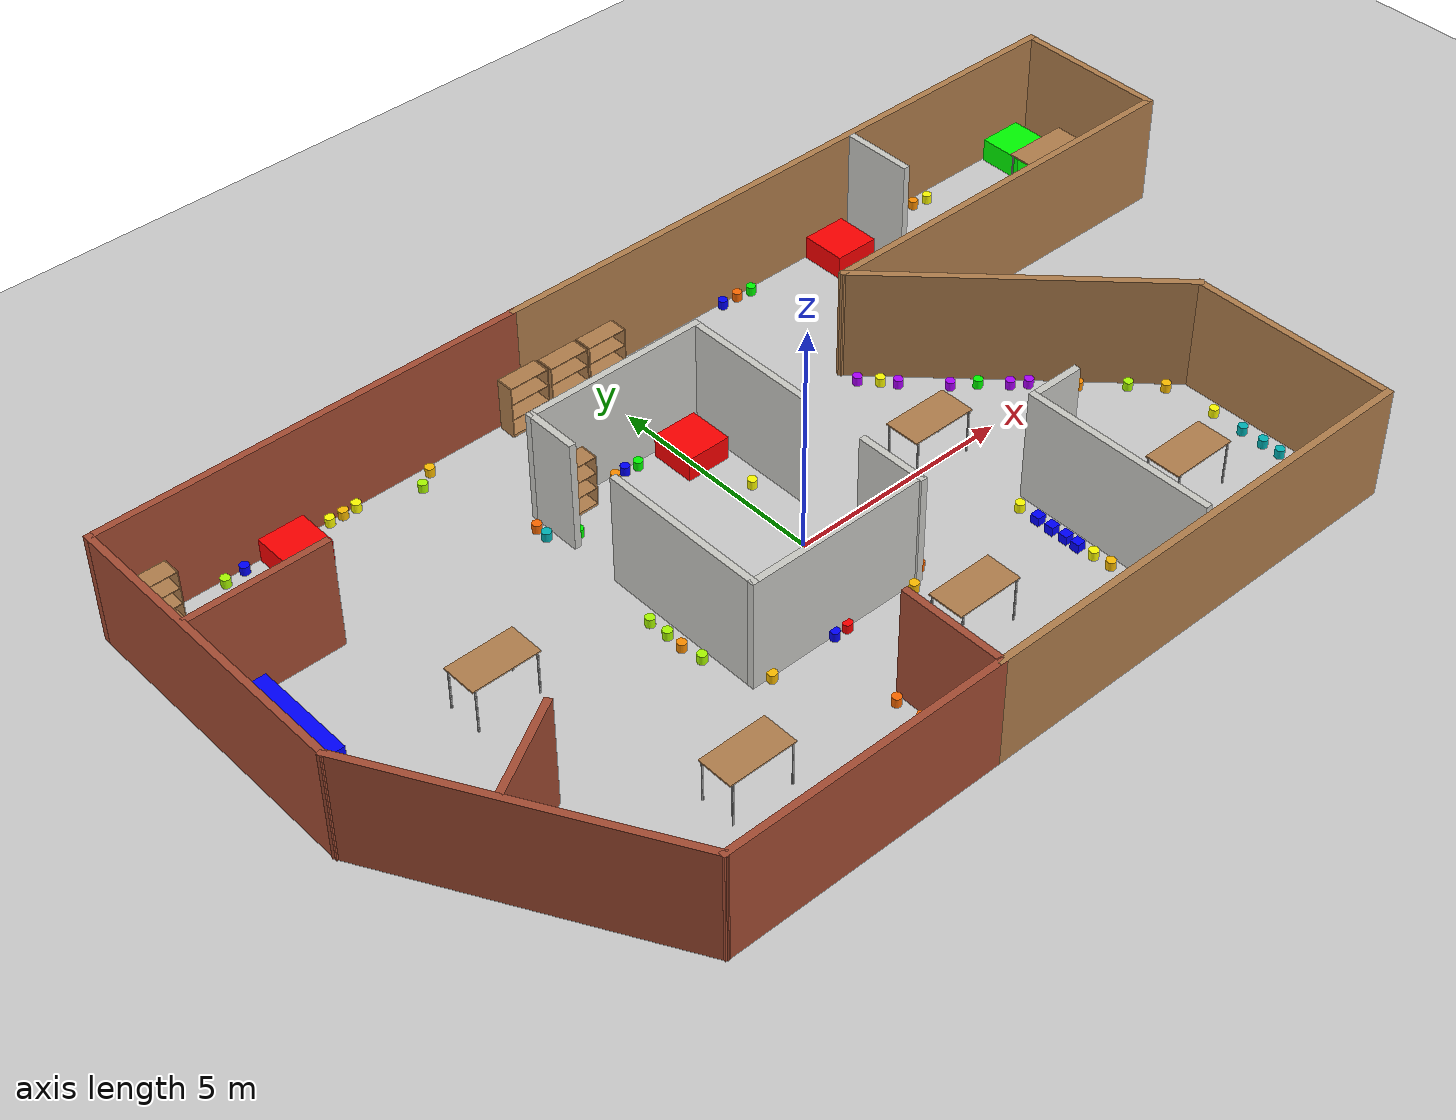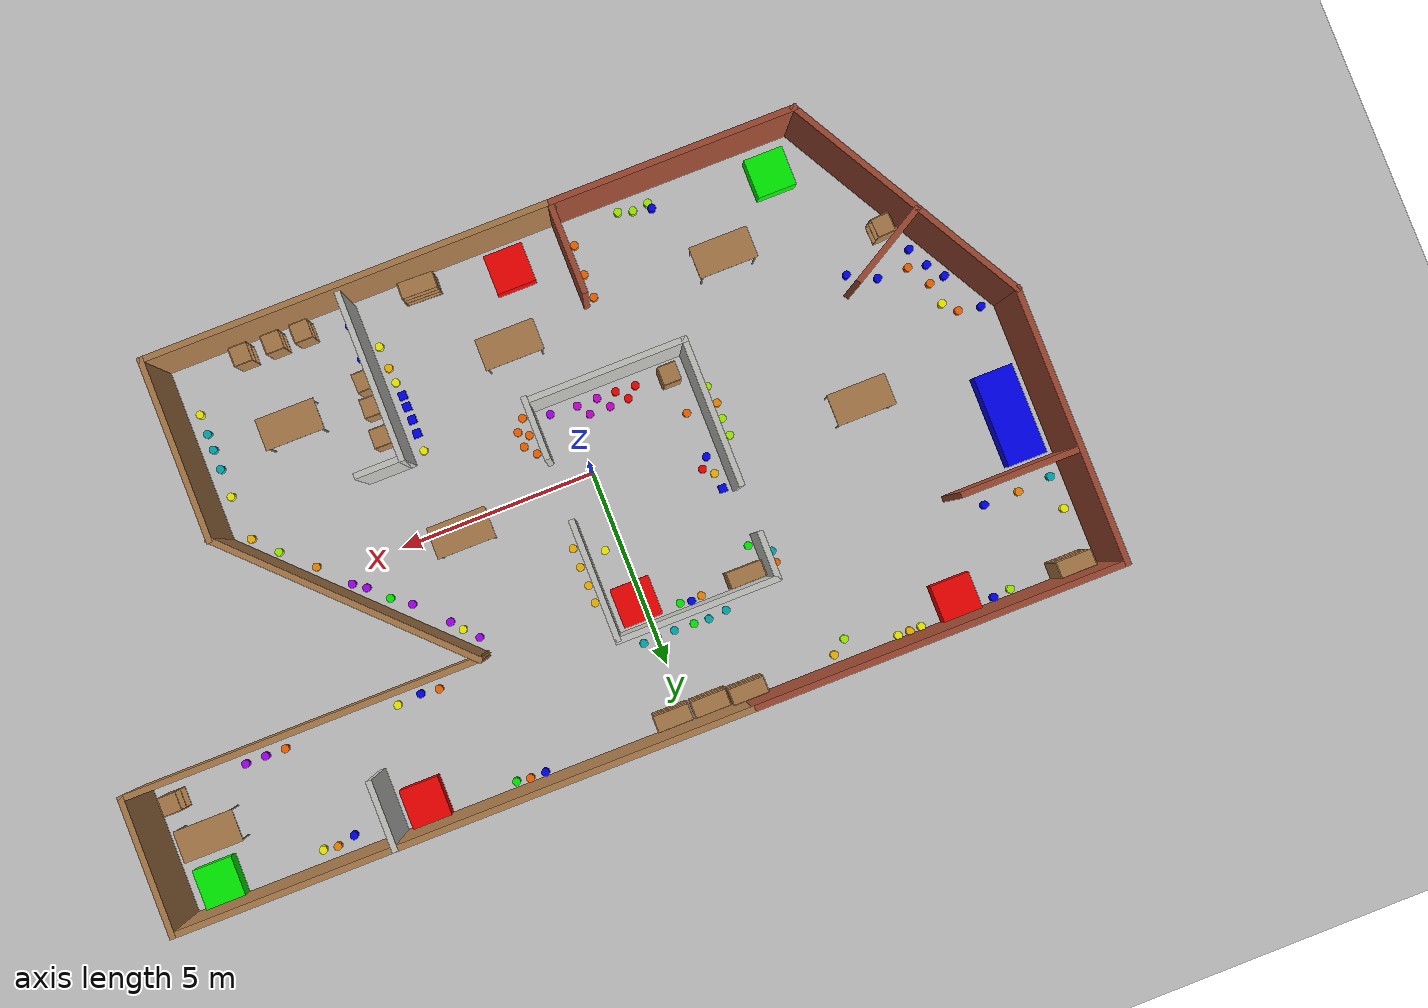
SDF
<sdf version="1.6">
 <world name="default">
  <model name="ground_plane">
   <static>1</static>
   <link name="link">
    <collision name="collision">
     <geometry><plane><normal>0 0 1</normal><size>100 100</size></plane></geometry>
     <surface>
      <contact><collide_bitmask>65535</collide_bitmask></contact>
      <friction><ode><mu>100</mu><mu2>50</mu2></ode></friction>
     </surface>
    </collision>
    <visual name="visual">
     <cast_shadows>0</cast_shadows>
     <geometry><plane><normal>0 0 1</normal><size>100 100</size></plane></geometry>
     <material>
      <script><uri>file://media/materials/scripts/gazebo.material</uri><name>Gazebo/Grey</name></script>
     </material>
    </visual>
   </link>
  </model>
  <light name="sun" type="directional">
   <pose>0 0 10 0 -0 0</pose>
   <diffuse>0.8 0.8 0.8 1</diffuse>
   <specular>0.2 0.2 0.2 1</specular>
   <attenuation>
    <range>1000</range>
    <constant>0.9</constant>
    <linear>0.01</linear>
    <quadratic>0.001</quadratic>
   </attenuation>
   <direction>-0.5 0.1 -0.9</direction>
  </light>
  <gravity>0 0 -9.8</gravity>
  <magnetic_field>6e-06 2.3e-05 -4.2e-05</magnetic_field>
  <atmosphere type="adiabatic"/>
  <physics name="default_physics" default="0" type="ode">
   <max_step_size>0.001</max_step_size>
   <real_time_factor>1</real_time_factor>
   <real_time_update_rate>1000</real_time_update_rate>
  </physics>
  <scene><ambient>0.4 0.4 0.4 1</ambient><background>0.7 0.7 0.7 1</background><shadows>1</shadows></scene>
  <spherical_coordinates>
   <surface_model>EARTH_WGS84</surface_model>
   <latitude_deg>0</latitude_deg>
   <longitude_deg>0</longitude_deg>
   <elevation>0</elevation>
   <heading_deg>0</heading_deg>
  </spherical_coordinates>
  <audio><device>default</device></audio>
  <model name="new_building_0">
   <pose>1.0207 0.182104 0 0 -0 0</pose>
   <link name="Wall_11">
    <collision name="Wall_11_Collision">
     <geometry><box><size>3.75 0.15 2.5</size></box></geometry>
     <pose>0 0 1.25 0 -0 0</pose>
    </collision>
    <visual name="Wall_11_Visual">
     <pose>0 0 1.25 0 -0 0</pose>
     <geometry><box><size>3.75 0.15 2.5</size></box></geometry>
     <material>
      <script><uri>file://media/materials/scripts/gazebo.material</uri><name>Gazebo/CeilingTiled</name></script>
      <ambient>0.996078 0.47451 0.0196078 1</ambient>
     </material>
     <meta><layer>0</layer></meta>
    </visual>
    <pose>-4.14163 -0.403047 0 0 -0 1.5708</pose>
   </link>
   <link name="Wall_14">
    <collision name="Wall_14_Collision">
     <geometry><box><size>3.5 0.15 2.5</size></box></geometry>
     <pose>0 0 1.25 0 -0 0</pose>
    </collision>
    <visual name="Wall_14_Visual">
     <pose>0 0 1.25 0 -0 0</pose>
     <geometry><box><size>3.5 0.15 2.5</size></box></geometry>
     <material>
      <script><uri>file://media/materials/scripts/gazebo.material</uri><name>Gazebo/Wood</name></script>
      <ambient>0 0 1 1</ambient>
     </material>
     <meta><layer>0</layer></meta>
    </visual>
    <pose>11.8417 4.67007 0 0 -0 -1.5708</pose>
   </link>
   <link name="Wall_15">
    <collision name="Wall_15_Collision">
     <geometry><box><size>9 0.15 2.5</size></box></geometry>
     <pose>0 0 1.25 0 -0 0</pose>
    </collision>
    <visual name="Wall_15_Visual">
     <pose>0 0 1.25 0 -0 0</pose>
     <geometry><box><size>9 0.15 2.5</size></box></geometry>
     <material>
      <script><uri>file://media/materials/scripts/gazebo.material</uri><name>Gazebo/Wood</name></script>
      <ambient>0 0 1 1</ambient>
     </material>
     <meta><layer>0</layer></meta>
    </visual>
    <pose>7.41668 2.99507 0 0 -0 3.14159</pose>
   </link>
   <link name="Wall_16">
    <collision name="Wall_16_Collision">
     <geometry><box><size>7 0.15 2.5</size></box></geometry>
     <pose>0 0 1.25 0 -0 0</pose>
    </collision>
    <visual name="Wall_16_Visual">
     <pose>0 0 1.25 0 -0 0</pose>
     <geometry><box><size>7 0.15 2.5</size></box></geometry>
     <material>
      <script><uri>file://media/materials/scripts/gazebo.material</uri><name>Gazebo/Wood</name></script>
      <ambient>0.435294 0.796078 0.67451 1</ambient>
     </material>
     <meta><layer>0</layer></meta>
    </visual>
    <pose>5.41352 0.573235 0 0 -0 -0.785398</pose>
   </link>
   <link name="Wall_17">
    <collision name="Wall_17_Collision">
     <geometry><box><size>4.64151 0.15 2.5</size></box></geometry>
     <pose>0 0 1.25 0 -0 0</pose>
    </collision>
    <visual name="Wall_17_Visual">
     <pose>0 0 1.25 0 -0 0</pose>
     <geometry><box><size>4.64151 0.15 2.5</size></box></geometry>
     <material>
      <script><uri>file://media/materials/scripts/gazebo.material</uri><name>Gazebo/Wood</name></script>
      <ambient>0.435294 0.796078 0.67451 1</ambient>
     </material>
     <meta><layer>0</layer></meta>
    </visual>
    <pose>7.83536 -4.09436 0 0 -0 -1.5708</pose>
   </link>
   <link name="Wall_19">
    <collision name="Wall_19_Collision">
     <geometry><box><size>6.87293 0.15 2.5</size></box></geometry>
     <pose>0 0 1.25 0 -0 0</pose>
    </collision>
    <visual name="Wall_19_Visual">
     <pose>0 0 1.25 0 -0 0</pose>
     <geometry><box><size>6.87293 0.15 2.5</size></box></geometry>
     <material>
      <script><uri>file://media/materials/scripts/gazebo.material</uri><name>Gazebo/Bricks</name></script>
      <ambient>0.921569 0.807843 0.615686 1</ambient>
     </material>
     <meta><layer>0</layer></meta>
    </visual>
    <pose>-10.1646 -3.41148 0 0 -0 2.08387</pose>
   </link>
   <link name="Wall_20">
    <collision name="Wall_20_Collision">
     <geometry><box><size>7 0.15 2.5</size></box></geometry>
     <pose>0 0 1.25 0 -0 0</pose>
    </collision>
    <visual name="Wall_20_Visual">
     <pose>0 0 1.25 0 -0 0</pose>
     <geometry><box><size>7 0.15 2.5</size></box></geometry>
     <material>
      <script><uri>file://media/materials/scripts/gazebo.material</uri><name>Gazebo/Bricks</name></script>
      <ambient>0.760784 0.662745 0.627451 1</ambient>
     </material>
     <meta><layer>0</layer></meta>
    </visual>
    <pose>-11.8146 2.94216 0 0 -0 1.5708</pose>
   </link>
   <link name="Wall_21">
    <collision name="Wall_21_Collision">
     <geometry><box><size>9.5 0.15 2.5</size></box></geometry>
     <pose>0 0 1.25 0 -0 0</pose>
    </collision>
    <visual name="Wall_21_Visual">
     <pose>0 0 1.25 0 -0 0</pose>
     <geometry><box><size>9.5 0.15 2.5</size></box></geometry>
     <material>
      <script><uri>file://media/materials/scripts/gazebo.material</uri><name>Gazebo/Bricks</name></script>
      <ambient>1 1 1 1</ambient>
     </material>
     <meta><layer>0</layer></meta>
    </visual>
    <pose>-7.13964 6.36716 0 0 -0 0</pose>
   </link>
   <link name="Wall_23">
    <collision name="Wall_23_Collision">
     <geometry><box><size>3 0.15 2.5</size></box></geometry>
     <pose>0 0 1.25 0 -0 0</pose>
    </collision>
    <visual name="Wall_23_Visual">
     <pose>0 0 1.25 0 -0 0</pose>
     <geometry><box><size>3 0.15 2.5</size></box></geometry>
     <material>
      <script><uri>file://media/materials/scripts/gazebo.material</uri><name>Gazebo/Bricks</name></script>
      <ambient>1 1 1 1</ambient>
     </material>
     <meta><layer>0</layer></meta>
    </visual>
    <pose>-10.291 3.51479 0 0 -0 0</pose>
   </link>
   <link name="Wall_25">
    <collision name="Wall_25_Collision">
     <geometry><box><size>2.25 0.15 2.5</size></box></geometry>
     <pose>0 0 1.25 0 -0 0</pose>
    </collision>
    <visual name="Wall_25_Visual">
     <pose>0 0 1.25 0 -0 0</pose>
     <geometry><box><size>2.25 0.15 2.5</size></box></geometry>
     <material>
      <script><uri>file://media/materials/scripts/gazebo.material</uri><name>Gazebo/Bricks</name></script>
      <ambient>1 1 1 1</ambient>
     </material>
     <meta><layer>0</layer></meta>
    </visual>
    <pose>-2.37608 -5.16665 0 0 -0 1.5708</pose>
   </link>
   <link name="Wall_28">
    <collision name="Wall_28_Collision">
     <geometry><box><size>2.25 0.15 2.5</size></box></geometry>
     <pose>0 0 1.25 0 -0 0</pose>
    </collision>
    <visual name="Wall_28_Visual">
     <pose>0 0 1.25 0 -0 0</pose>
     <geometry><box><size>2.25 0.15 2.5</size></box></geometry>
     <material>
      <script><uri>file://media/materials/scripts/gazebo.material</uri><name>Gazebo/Bricks</name></script>
      <ambient>1 1 1 1</ambient>
     </material>
     <meta><layer>0</layer></meta>
    </visual>
    <pose>-9.39155 -2.54061 0 0 -0 0.523599</pose>
   </link>
   <link name="Wall_3">
    <collision name="Wall_3_Collision">
     <geometry><box><size>4.13184 0.15 2.5</size></box></geometry>
     <pose>0 0 1.25 0 -0 0</pose>
    </collision>
    <visual name="Wall_3_Visual">
     <pose>0 0 1.25 0 -0 0</pose>
     <geometry><box><size>4.13184 0.15 2.5</size></box></geometry>
     <material>
      <script><uri>file://media/materials/scripts/gazebo.material</uri><name>Gazebo/CeilingTiled</name></script>
      <ambient>0.996078 0.47451 0.0196078 1</ambient>
     </material>
     <meta><layer>0</layer></meta>
    </visual>
    <pose>-2.15071 3.76645 0 0 -0 0</pose>
   </link>
   <link name="Wall_30">
    <collision name="Wall_30_Collision">
     <geometry><box><size>4.25 0.15 2.5</size></box></geometry>
     <pose>0 0 1.25 0 -0 0</pose>
    </collision>
    <visual name="Wall_30_Visual">
     <pose>0 0 1.25 0 -0 0</pose>
     <geometry><box><size>4.25 0.15 2.5</size></box></geometry>
     <material>
      <script><uri>file://media/materials/scripts/gazebo.material</uri><name>Gazebo/CeilingTiled</name></script>
      <ambient>0.760784 0.662745 0.627451 1</ambient>
     </material>
     <meta><layer>0</layer></meta>
    </visual>
    <pose>3.00145 -4.05817 0 0 -0 1.5708</pose>
   </link>
   <link name="Wall_31">
    <collision name="Wall_31_Collision">
     <geometry><box><size>1.25 0.15 2.5</size></box></geometry>
     <pose>0 0 1.25 0 -0 0</pose>
    </collision>
    <visual name="Wall_31_Visual">
     <pose>0 0 1.25 0 -0 0</pose>
     <geometry><box><size>1.25 0.15 2.5</size></box></geometry>
     <material>
      <script><uri>file://media/materials/scripts/gazebo.material</uri><name>Gazebo/CeilingTiled</name></script>
      <ambient>0.760784 0.662745 0.627451 1</ambient>
     </material>
     <meta><layer>0</layer></meta>
    </visual>
    <pose>3.55145 -2.00817 0 0 -0 0</pose>
   </link>
   <link name="Wall_33">
    <collision name="Wall_33_Collision">
     <geometry><box><size>1.75 0.15 2.5</size></box></geometry>
     <pose>0 0 1.25 0 -0 0</pose>
    </collision>
    <visual name="Wall_33_Visual">
     <pose>0 0 1.25 0 -0 0</pose>
     <geometry><box><size>1.75 0.15 2.5</size></box></geometry>
     <material>
      <script><uri>file://media/materials/scripts/gazebo.material</uri><name>Gazebo/CeilingTiled</name></script>
      <ambient>0 0 1 1</ambient>
     </material>
     <meta><layer>0</layer></meta>
    </visual>
    <pose>6.37467 5.54918 0 0 -0 -1.5708</pose>
   </link>
   <link name="Wall_37">
    <collision name="Wall_37_Collision">
     <geometry><box><size>14.4563 0.15 2.5</size></box></geometry>
     <pose>0 0 1.25 0 -0 0</pose>
    </collision>
    <visual name="Wall_37_Visual">
     <pose>0 0 1.25 0 -0 0</pose>
     <geometry><box><size>14.4563 0.15 2.5</size></box></geometry>
     <material>
      <script><uri>file://media/materials/scripts/gazebo.material</uri><name>Gazebo/Wood</name></script>
      <ambient>0 0 1 1</ambient>
     </material>
     <meta><layer>0</layer></meta>
    </visual>
    <pose>4.68852 6.35612 0 0 -0 3.14005</pose>
   </link>
   <link name="Wall_39">
    <collision name="Wall_39_Collision">
     <geometry><box><size>6.25 0.15 2.5</size></box></geometry>
     <pose>0 0 1.25 0 -0 0</pose>
    </collision>
    <visual name="Wall_39_Visual">
     <pose>0 0 1.25 0 -0 0</pose>
     <geometry><box><size>6.25 0.15 2.5</size></box></geometry>
     <material>
      <script><uri>file://media/materials/scripts/gazebo.material</uri><name>Gazebo/Bricks</name></script>
      <ambient>0.996078 0.47451 0.0196078 1</ambient>
     </material>
     <meta><layer>0</layer></meta>
    </visual>
    <pose>-5.46464 -6.34012 0 0 -0 0</pose>
   </link>
   <link name="Wall_4">
    <collision name="Wall_4_Collision">
     <geometry><box><size>3.0399 0.15 2.5</size></box></geometry>
     <pose>0 0 1.25 0 -0 0</pose>
    </collision>
    <visual name="Wall_4_Visual">
     <pose>0 0 1.25 0 -0 0</pose>
     <geometry><box><size>3.0399 0.15 2.5</size></box></geometry>
     <material>
      <script><uri>file://media/materials/scripts/gazebo.material</uri><name>Gazebo/CeilingTiled</name></script>
      <ambient>0.996078 0.47451 0.0196078 1</ambient>
     </material>
     <meta><layer>0</layer></meta>
    </visual>
    <pose>-0.159795 2.27498 0 0 -0 -1.5708</pose>
   </link>
   <link name="Wall_41">
    <collision name="Wall_41_Collision">
     <geometry><box><size>10.4 0.15 2.5</size></box></geometry>
     <pose>0 0 1.25 0 -0 0</pose>
    </collision>
    <visual name="Wall_41_Visual">
     <pose>0 0 1.25 0 -0 0</pose>
     <geometry><box><size>10.4 0.15 2.5</size></box></geometry>
     <material>
      <script><uri>file://media/materials/scripts/gazebo.material</uri><name>Gazebo/Wood</name></script>
      <ambient>0.435294 0.796078 0.67451 1</ambient>
     </material>
     <meta><layer>0</layer></meta>
    </visual>
    <pose>2.71036 -6.34012 0 0 -0 3.14159</pose>
   </link>
   <link name="Wall_6">
    <collision name="Wall_6_Collision">
     <geometry><box><size>4.13184 0.15 2.5</size></box></geometry>
     <pose>0 0 1.25 0 -0 0</pose>
    </collision>
    <visual name="Wall_6_Visual">
     <pose>0 0 1.25 0 -0 0</pose>
     <geometry><box><size>4.13184 0.15 2.5</size></box></geometry>
     <material>
      <script><uri>file://media/materials/scripts/gazebo.material</uri><name>Gazebo/CeilingTiled</name></script>
      <ambient>0.996078 0.47451 0.0196078 1</ambient>
     </material>
     <meta><layer>0</layer></meta>
    </visual>
    <pose>-2.15071 -2.20305 0 0 -0 0</pose>
   </link>
   <link name="Wall_7">
    <collision name="Wall_7_Collision">
     <geometry><box><size>1.5796 0.15 2.5</size></box></geometry>
     <pose>0 0 1.25 0 -0 0</pose>
    </collision>
    <visual name="Wall_7_Visual">
     <pose>0 0 1.25 0 -0 0</pose>
     <geometry><box><size>1.5796 0.15 2.5</size></box></geometry>
     <material>
      <script><uri>file://media/materials/scripts/gazebo.material</uri><name>Gazebo/CeilingTiled</name></script>
      <ambient>0.996078 0.47451 0.0196078 1</ambient>
     </material>
     <meta><layer>0</layer></meta>
    </visual>
    <pose>-0.159795 -1.53477 0 0 -0 1.5708</pose>
   </link>
   <link name="Wall_9">
    <collision name="Wall_9_Collision">
     <geometry><box><size>1.25 0.15 2.5</size></box></geometry>
     <pose>0 0 1.25 0 -0 0</pose>
    </collision>
    <visual name="Wall_9_Visual">
     <pose>0 0 1.25 0 -0 0</pose>
     <geometry><box><size>1.25 0.15 2.5</size></box></geometry>
     <material>
      <script><uri>file://media/materials/scripts/gazebo.material</uri><name>Gazebo/CeilingTiled</name></script>
      <ambient>0.996078 0.47451 0.0196078 1</ambient>
     </material>
     <meta><layer>0</layer></meta>
    </visual>
    <pose>-4.14163 3.21645 0 0 -0 -1.5708</pose>
   </link>
   <static>1</static>
  </model>
  <model name="blue_box">
   <link name="link_0">
    <inertial>
     <mass>1</mass>
     <inertia>
      <ixx>0.166667</ixx>
      <ixy>0</ixy>
      <ixz>0</ixz>
      <iyy>0.166667</iyy>
      <iyz>0</iyz>
      <izz>0.166667</izz>
     </inertia>
    </inertial>
    <visual name="visual">
     <geometry><box><size>1 2.32493 1</size></box></geometry>
     <material>
      <lighting>1</lighting>
      <script><uri>file://media/materials/scripts/gazebo.material</uri><name>Gazebo/Grey</name></script>
      <shader type="vertex"><normal_map>__default__</normal_map></shader>
      <ambient>0 0 1 1</ambient>
      <diffuse>0 0 1 1</diffuse>
      <specular>0 0 1 1</specular>
      <emissive>0 0 0 1</emissive>
     </material>
    </visual>
    <collision name="collision">
     <geometry><box><size>1 2.32493 1</size></box></geometry>
     <surface>
      <friction>
       <ode><mu>1</mu><mu2>1</mu2><fdir1>0 0 0</fdir1><slip1>0</slip1><slip2>0</slip2></ode>
       <torsional>
        <coefficient>1</coefficient>
        <patch_radius>0</patch_radius>
        <surface_radius>0</surface_radius>
        <use_patch_radius>1</use_patch_radius>
        <ode><slip>0</slip></ode>
       </torsional>
      </friction>
      <bounce><restitution_coefficient>0</restitution_coefficient><threshold>1e+06</threshold></bounce>
      <contact>
       <collide_without_contact>0</collide_without_contact>
       <collide_without_contact_bitmask>1</collide_without_contact_bitmask>
       <collide_bitmask>1</collide_bitmask>
       <ode>
        <soft_cfm>0</soft_cfm>
        <soft_erp>0.2</soft_erp>
        <kp>1e+13</kp>
        <kd>1</kd>
        <max_vel>0.01</max_vel>
        <min_depth>0</min_depth>
       </ode>
       <bullet>
        <split_impulse>1</split_impulse>
        <split_impulse_penetration_threshold>-0.01</split_impulse_penetration_threshold>
        <soft_cfm>0</soft_cfm>
        <soft_erp>0.2</soft_erp>
        <kp>1e+13</kp>
        <kd>1</kd>
       </bullet>
      </contact>
     </surface>
    </collision>
   </link>
   <static>1</static>
   <pose>-9.98993 2.37638 0 0 -0 0</pose>
  </model>
  <model name="red_box">
   <link name="link_0">
    <inertial>
     <mass>1</mass>
     <inertia>
      <ixx>0.166667</ixx>
      <ixy>0</ixy>
      <ixz>0</ixz>
      <iyy>0.166667</iyy>
      <iyz>0</iyz>
      <izz>0.166667</izz>
     </inertia>
    </inertial>
    <visual name="visual">
     <geometry><box><size>1 1 1</size></box></geometry>
     <material>
      <lighting>1</lighting>
      <script><uri>file://media/materials/scripts/gazebo.material</uri><name>Gazebo/Grey</name></script>
      <shader type="vertex"><normal_map>__default__</normal_map></shader>
      <ambient>1 0 0 1</ambient>
      <diffuse>1 0 0 1</diffuse>
      <specular>1 0 0 1</specular>
      <emissive>0 0 0 1</emissive>
     </material>
    </visual>
    <collision name="collision">
     <geometry><box><size>1 1 1</size></box></geometry>
     <surface>
      <friction>
       <ode><mu>1</mu><mu2>1</mu2><fdir1>0 0 0</fdir1><slip1>0</slip1><slip2>0</slip2></ode>
       <torsional>
        <coefficient>1</coefficient>
        <patch_radius>0</patch_radius>
        <surface_radius>0</surface_radius>
        <use_patch_radius>1</use_patch_radius>
        <ode><slip>0</slip></ode>
       </torsional>
      </friction>
      <bounce><restitution_coefficient>0</restitution_coefficient><threshold>1e+06</threshold></bounce>
      <contact>
       <collide_without_contact>0</collide_without_contact>
       <collide_without_contact_bitmask>1</collide_without_contact_bitmask>
       <collide_bitmask>1</collide_bitmask>
       <ode>
        <soft_cfm>0</soft_cfm>
        <soft_erp>0.2</soft_erp>
        <kp>1e+13</kp>
        <kd>1</kd>
        <max_vel>0.01</max_vel>
        <min_depth>0</min_depth>
       </ode>
       <bullet>
        <split_impulse>1</split_impulse>
        <split_impulse_penetration_threshold>-0.01</split_impulse_penetration_threshold>
        <soft_cfm>0</soft_cfm>
        <soft_erp>0.2</soft_erp>
        <kp>1e+13</kp>
        <kd>1</kd>
       </bullet>
      </contact>
     </surface>
    </collision>
   </link>
   <static>1</static>
   <pose>0.144471 3.2997 0 0 -0 0</pose>
  </model>
  <model name="green_box">
   <link name="link_0">
    <inertial>
     <mass>1</mass>
     <inertia>
      <ixx>0.166667</ixx>
      <ixy>0</ixy>
      <ixz>0</ixz>
      <iyy>0.166667</iyy>
      <iyz>0</iyz>
      <izz>0.166667</izz>
     </inertia>
    </inertial>
    <visual name="visual">
     <geometry><box><size>1 0.999998 1</size></box></geometry>
     <material>
      <lighting>1</lighting>
      <script><uri>file://media/materials/scripts/gazebo.material</uri><name>Gazebo/Grey</name></script>
      <shader type="vertex"><normal_map>__default__</normal_map></shader>
      <ambient>0 1 0 1</ambient>
      <diffuse>0 1 0 1</diffuse>
      <specular>0 1 0 1</specular>
      <emissive>0 0 0 1</emissive>
     </material>
    </visual>
    <collision name="collision">
     <geometry><box><size>1 0.999998 1</size></box></geometry>
     <surface>
      <friction>
       <ode><mu>1</mu><mu2>1</mu2><fdir1>0 0 0</fdir1><slip1>0</slip1><slip2>0</slip2></ode>
       <torsional>
        <coefficient>1</coefficient>
        <patch_radius>0</patch_radius>
        <surface_radius>0</surface_radius>
        <use_patch_radius>1</use_patch_radius>
        <ode><slip>0</slip></ode>
       </torsional>
      </friction>
      <bounce><restitution_coefficient>0</restitution_coefficient><threshold>1e+06</threshold></bounce>
      <contact>
       <collide_without_contact>0</collide_without_contact>
       <collide_without_contact_bitmask>1</collide_without_contact_bitmask>
       <collide_bitmask>1</collide_bitmask>
       <ode>
        <soft_cfm>0</soft_cfm>
        <soft_erp>0.2</soft_erp>
        <kp>1e+13</kp>
        <kd>1</kd>
        <max_vel>0.01</max_vel>
        <min_depth>0</min_depth>
       </ode>
       <bullet>
        <split_impulse>1</split_impulse>
        <split_impulse_penetration_threshold>-0.01</split_impulse_penetration_threshold>
        <soft_cfm>0</soft_cfm>
        <soft_erp>0.2</soft_erp>
        <kp>1e+13</kp>
        <kd>1</kd>
       </bullet>
      </contact>
     </surface>
    </collision>
   </link>
   <static>1</static>
   <pose>-6.72017 -5.2953 0 0 -0 0</pose>
  </model>
  <model name="green_box_0">
   <link name="link_0">
    <inertial>
     <mass>1</mass>
     <inertia>
      <ixx>0.166667</ixx>
      <ixy>0</ixy>
      <ixz>0</ixz>
      <iyy>0.166667</iyy>
      <iyz>0</iyz>
      <izz>0.166667</izz>
     </inertia>
    </inertial>
    <visual name="visual">
     <geometry><box><size>1 0.999998 1</size></box></geometry>
     <material>
      <lighting>1</lighting>
      <script><uri>file://media/materials/scripts/gazebo.material</uri><name>Gazebo/Grey</name></script>
      <shader type="vertex"><normal_map>__default__</normal_map></shader>
      <ambient>0 1 0 1</ambient>
      <diffuse>0 1 0 1</diffuse>
      <specular>0 1 0 1</specular>
      <emissive>0 0 0 1</emissive>
     </material>
    </visual>
    <collision name="collision">
     <geometry><box><size>1 0.999998 1</size></box></geometry>
     <surface>
      <friction>
       <ode><mu>1</mu><mu2>1</mu2><fdir1>0 0 0</fdir1><slip1>0</slip1><slip2>0</slip2></ode>
       <torsional>
        <coefficient>1</coefficient>
        <patch_radius>0</patch_radius>
        <surface_radius>0</surface_radius>
        <use_patch_radius>1</use_patch_radius>
        <ode><slip>0</slip></ode>
       </torsional>
      </friction>
      <bounce><restitution_coefficient>0</restitution_coefficient><threshold>1e+06</threshold></bounce>
      <contact>
       <collide_without_contact>0</collide_without_contact>
       <collide_without_contact_bitmask>1</collide_without_contact_bitmask>
       <collide_bitmask>1</collide_bitmask>
       <ode>
        <soft_cfm>0</soft_cfm>
        <soft_erp>0.2</soft_erp>
        <kp>1e+13</kp>
        <kd>1</kd>
        <max_vel>0.01</max_vel>
        <min_depth>0</min_depth>
       </ode>
       <bullet>
        <split_impulse>1</split_impulse>
        <split_impulse_penetration_threshold>-0.01</split_impulse_penetration_threshold>
        <soft_cfm>0</soft_cfm>
        <soft_erp>0.2</soft_erp>
        <kp>1e+13</kp>
        <kd>1</kd>
       </bullet>
      </contact>
     </surface>
    </collision>
   </link>
   <static>1</static>
   <pose>11.9737 5.95039 0 0 -0 0</pose>
  </model>
  <model name="red_box_0">
   <link name="link_0">
    <inertial>
     <mass>1</mass>
     <inertia>
      <ixx>0.166667</ixx>
      <ixy>0</ixy>
      <ixz>0</ixz>
      <iyy>0.166667</iyy>
      <iyz>0</iyz>
      <izz>0.166667</izz>
     </inertia>
    </inertial>
    <visual name="visual">
     <geometry><box><size>1 1 1</size></box></geometry>
     <material>
      <lighting>1</lighting>
      <script><uri>file://media/materials/scripts/gazebo.material</uri><name>Gazebo/Grey</name></script>
      <shader type="vertex"><normal_map>__default__</normal_map></shader>
      <ambient>1 0 0 1</ambient>
      <diffuse>1 0 0 1</diffuse>
      <specular>1 0 0 1</specular>
      <emissive>0 0 0 1</emissive>
     </material>
    </visual>
    <collision name="collision">
     <geometry><box><size>1 1 1</size></box></geometry>
     <surface>
      <friction>
       <ode><mu>1</mu><mu2>1</mu2><fdir1>0 0 0</fdir1><slip1>0</slip1><slip2>0</slip2></ode>
       <torsional>
        <coefficient>1</coefficient>
        <patch_radius>0</patch_radius>
        <surface_radius>0</surface_radius>
        <use_patch_radius>1</use_patch_radius>
        <ode><slip>0</slip></ode>
       </torsional>
      </friction>
      <bounce><restitution_coefficient>0</restitution_coefficient><threshold>1e+06</threshold></bounce>
      <contact>
       <collide_without_contact>0</collide_without_contact>
       <collide_without_contact_bitmask>1</collide_without_contact_bitmask>
       <collide_bitmask>1</collide_bitmask>
       <ode>
        <soft_cfm>0</soft_cfm>
        <soft_erp>0.2</soft_erp>
        <kp>1e+13</kp>
        <kd>1</kd>
        <max_vel>0.01</max_vel>
        <min_depth>0</min_depth>
       </ode>
       <bullet>
        <split_impulse>1</split_impulse>
        <split_impulse_penetration_threshold>-0.01</split_impulse_penetration_threshold>
        <soft_cfm>0</soft_cfm>
        <soft_erp>0.2</soft_erp>
        <kp>1e+13</kp>
        <kd>1</kd>
       </bullet>
      </contact>
     </surface>
    </collision>
   </link>
   <static>1</static>
   <pose>6.64755 5.96572 0 0 -0 0</pose>
  </model>
  <model name="cabinet">
   <static>1</static>
   <link name="cabinet_bottom_plate">
    <inertial>
     <pose>0 0 -1 0 -0 0</pose>
     <inertia><ixx>2.05</ixx><ixy>0</ixy><ixz>0</ixz><iyy>2.05</iyy><iyz>0</iyz><izz>2.05</izz></inertia>
     <mass>25</mass>
    </inertial>
    <collision name="cabinet_bottom_plate_geom">
     <pose>0 0 0.01 0 -0 0</pose>
     <geometry><box><size>0.45 0.45 0.02</size></box></geometry>
    </collision>
    <visual name="cabinet_bottom_plate_geom_visual">
     <pose>0 0 0.01 0 -0 0</pose>
     <geometry><box><size>0.45 0.45 0.02</size></box></geometry>
     <material>
      <script><uri>file://media/materials/scripts/gazebo.material</uri><name>Gazebo/Wood</name></script>
     </material>
    </visual>
    <collision name="cabinet_bottom_plate_geom_cabinet_back_plate">
     <pose>0.235 0 0.51 0 -0 0</pose>
     <geometry><box><size>0.02 0.45 1.02</size></box></geometry>
    </collision>
    <visual name="cabinet_bottom_plate_geom_cabinet_back_plate_visual">
     <pose>0.235 0 0.51 0 -0 0</pose>
     <geometry><box><size>0.02 0.45 1.02</size></box></geometry>
     <material>
      <script><uri>file://media/materials/scripts/gazebo.material</uri><name>Gazebo/Wood</name></script>
     </material>
    </visual>
    <collision name="cabinet_bottom_plate_geom_cabinet_left_plate">
     <pose>0 0.235 0.51 0 -0 0</pose>
     <geometry><box><size>0.45 0.02 1.02</size></box></geometry>
    </collision>
    <visual name="cabinet_bottom_plate_geom_cabinet_left_plate_visual">
     <pose>0 0.235 0.51 0 -0 0</pose>
     <geometry><box><size>0.45 0.02 1.02</size></box></geometry>
     <material>
      <script><uri>file://media/materials/scripts/gazebo.material</uri><name>Gazebo/Wood</name></script>
     </material>
    </visual>
    <collision name="cabinet_bottom_plate_geom_cabinet_middle_plate">
     <pose>0 0 0.51 0 -0 0</pose>
     <geometry><box><size>0.45 0.45 0.02</size></box></geometry>
    </collision>
    <visual name="cabinet_bottom_plate_geom_cabinet_middle_plate_visual">
     <pose>0 0 0.51 0 -0 0</pose>
     <geometry><box><size>0.45 0.45 0.02</size></box></geometry>
     <material>
      <script><uri>file://media/materials/scripts/gazebo.material</uri><name>Gazebo/Wood</name></script>
     </material>
    </visual>
    <collision name="cabinet_bottom_plate_geom_cabinet_right_plate">
     <pose>0 -0.235 0.51 0 -0 0</pose>
     <geometry><box><size>0.45 0.02 1.02</size></box></geometry>
    </collision>
    <visual name="cabinet_bottom_plate_geom_cabinet_right_plate_visual">
     <pose>0 -0.235 0.51 0 -0 0</pose>
     <geometry><box><size>0.45 0.02 1.02</size></box></geometry>
     <material>
      <script><uri>file://media/materials/scripts/gazebo.material</uri><name>Gazebo/Wood</name></script>
     </material>
    </visual>
    <collision name="cabinet_bottom_plate_geom_cabinet_top_plate">
     <pose>0 0 1.01 0 -0 0</pose>
     <geometry><box><size>0.45 0.45 0.02</size></box></geometry>
    </collision>
    <visual name="cabinet_bottom_plate_geom_cabinet_top_plate_visual">
     <pose>0 0 1.01 0 -0 0</pose>
     <geometry><box><size>0.45 0.45 0.02</size></box></geometry>
     <material>
      <script><uri>file://media/materials/scripts/gazebo.material</uri><name>Gazebo/Wood</name></script>
     </material>
    </visual>
   </link>
   <pose>-2.59709 -1.54138 0 0 -0 0</pose>
  </model>
  <model name="cabinet_0">
   <static>1</static>
   <link name="cabinet_bottom_plate">
    <inertial>
     <pose>0 0 -1 0 -0 0</pose>
     <inertia><ixx>2.05</ixx><ixy>0</ixy><ixz>0</ixz><iyy>2.05</iyy><iyz>0</iyz><izz>2.05</izz></inertia>
     <mass>25</mass>
    </inertial>
    <collision name="cabinet_bottom_plate_geom">
     <pose>0 0 0.01 0 -0 0</pose>
     <geometry><box><size>0.45 0.45 0.02</size></box></geometry>
    </collision>
    <visual name="cabinet_bottom_plate_geom_visual">
     <pose>0 0 0.01 0 -0 0</pose>
     <geometry><box><size>0.45 0.45 0.02</size></box></geometry>
     <material>
      <script><uri>file://media/materials/scripts/gazebo.material</uri><name>Gazebo/Wood</name></script>
     </material>
    </visual>
    <collision name="cabinet_bottom_plate_geom_cabinet_back_plate">
     <pose>0.235 0 0.51 0 -0 0</pose>
     <geometry><box><size>0.02 0.45 1.02</size></box></geometry>
    </collision>
    <visual name="cabinet_bottom_plate_geom_cabinet_back_plate_visual">
     <pose>0.235 0 0.51 0 -0 0</pose>
     <geometry><box><size>0.02 0.45 1.02</size></box></geometry>
     <material>
      <script><uri>file://media/materials/scripts/gazebo.material</uri><name>Gazebo/Wood</name></script>
     </material>
    </visual>
    <collision name="cabinet_bottom_plate_geom_cabinet_left_plate">
     <pose>0 0.235 0.51 0 -0 0</pose>
     <geometry><box><size>0.45 0.02 1.02</size></box></geometry>
    </collision>
    <visual name="cabinet_bottom_plate_geom_cabinet_left_plate_visual">
     <pose>0 0.235 0.51 0 -0 0</pose>
     <geometry><box><size>0.45 0.02 1.02</size></box></geometry>
     <material>
      <script><uri>file://media/materials/scripts/gazebo.material</uri><name>Gazebo/Wood</name></script>
     </material>
    </visual>
    <collision name="cabinet_bottom_plate_geom_cabinet_middle_plate">
     <pose>0 0 0.51 0 -0 0</pose>
     <geometry><box><size>0.45 0.45 0.02</size></box></geometry>
    </collision>
    <visual name="cabinet_bottom_plate_geom_cabinet_middle_plate_visual">
     <pose>0 0 0.51 0 -0 0</pose>
     <geometry><box><size>0.45 0.45 0.02</size></box></geometry>
     <material>
      <script><uri>file://media/materials/scripts/gazebo.material</uri><name>Gazebo/Wood</name></script>
     </material>
    </visual>
    <collision name="cabinet_bottom_plate_geom_cabinet_right_plate">
     <pose>0 -0.235 0.51 0 -0 0</pose>
     <geometry><box><size>0.45 0.02 1.02</size></box></geometry>
    </collision>
    <visual name="cabinet_bottom_plate_geom_cabinet_right_plate_visual">
     <pose>0 -0.235 0.51 0 -0 0</pose>
     <geometry><box><size>0.45 0.02 1.02</size></box></geometry>
     <material>
      <script><uri>file://media/materials/scripts/gazebo.material</uri><name>Gazebo/Wood</name></script>
     </material>
    </visual>
    <collision name="cabinet_bottom_plate_geom_cabinet_top_plate">
     <pose>0 0 1.01 0 -0 0</pose>
     <geometry><box><size>0.45 0.45 0.02</size></box></geometry>
    </collision>
    <visual name="cabinet_bottom_plate_geom_cabinet_top_plate_visual">
     <pose>0 0 1.01 0 -0 0</pose>
     <geometry><box><size>0.45 0.45 0.02</size></box></geometry>
     <material>
      <script><uri>file://media/materials/scripts/gazebo.material</uri><name>Gazebo/Wood</name></script>
     </material>
    </visual>
   </link>
   <pose>12.2698 3.74107 0 0 -0 0</pose>
  </model>
  <model name="bookshelf">
   <static>1</static>
   <link name="link">
    <inertial><mass>1</mass></inertial>
    <collision name="back">
     <pose>0 0.005 0.6 0 -0 0</pose>
     <geometry><box><size>0.9 0.01 1.2</size></box></geometry>
    </collision>
    <visual name="visual1">
     <pose>0 0.005 0.6 0 -0 0</pose>
     <geometry><box><size>0.9 0.01 1.2</size></box></geometry>
     <material>
      <script><uri>file://media/materials/scripts/gazebo.material</uri><name>Gazebo/Wood</name></script>
     </material>
    </visual>
    <collision name="left_side">
     <pose>0.45 -0.195 0.6 0 -0 0</pose>
     <geometry><box><size>0.02 0.4 1.2</size></box></geometry>
    </collision>
    <visual name="visual2">
     <pose>0.45 -0.195 0.6 0 -0 0</pose>
     <geometry><box><size>0.02 0.4 1.2</size></box></geometry>
     <material>
      <script><uri>file://media/materials/scripts/gazebo.material</uri><name>Gazebo/Wood</name></script>
     </material>
    </visual>
    <collision name="right_side">
     <pose>-0.45 -0.195 0.6 0 -0 0</pose>
     <geometry><box><size>0.02 0.4 1.2</size></box></geometry>
    </collision>
    <visual name="visual3">
     <pose>-0.45 -0.195 0.6 0 -0 0</pose>
     <geometry><box><size>0.02 0.4 1.2</size></box></geometry>
     <material>
      <script><uri>file://media/materials/scripts/gazebo.material</uri><name>Gazebo/Wood</name></script>
     </material>
    </visual>
    <collision name="bottom">
     <pose>0 -0.195 0.03 0 -0 0</pose>
     <geometry><box><size>0.88 0.4 0.06</size></box></geometry>
    </collision>
    <visual name="visual4">
     <pose>0 -0.195 0.03 0 -0 0</pose>
     <geometry><box><size>0.88 0.4 0.06</size></box></geometry>
     <material>
      <script><uri>file://media/materials/scripts/gazebo.material</uri><name>Gazebo/Wood</name></script>
     </material>
    </visual>
    <collision name="top">
     <pose>0 -0.195 1.19 0 -0 0</pose>
     <geometry><box><size>0.88 0.4 0.02</size></box></geometry>
    </collision>
    <visual name="visual5">
     <pose>0 -0.195 1.19 0 -0 0</pose>
     <geometry><box><size>0.88 0.4 0.02</size></box></geometry>
     <material>
      <script><uri>file://media/materials/scripts/gazebo.material</uri><name>Gazebo/Wood</name></script>
     </material>
    </visual>
    <collision name="low_shelf">
     <pose>0 -0.195 0.43 0 -0 0</pose>
     <geometry><box><size>0.88 0.4 0.02</size></box></geometry>
    </collision>
    <visual name="visual6">
     <pose>0 -0.195 0.43 0 -0 0</pose>
     <geometry><box><size>0.88 0.4 0.02</size></box></geometry>
     <material>
      <script><uri>file://media/materials/scripts/gazebo.material</uri><name>Gazebo/Wood</name></script>
     </material>
    </visual>
    <collision name="high_shelf">
     <pose>0 -0.195 0.8 0 -0 0</pose>
     <geometry><box><size>0.88 0.4 0.02</size></box></geometry>
    </collision>
    <visual name="visual7">
     <pose>0 -0.195 0.8 0 -0 0</pose>
     <geometry><box><size>0.88 0.4 0.02</size></box></geometry>
     <material>
      <script><uri>file://media/materials/scripts/gazebo.material</uri><name>Gazebo/Wood</name></script>
     </material>
    </visual>
   </link>
   <pose>-9.97911 6.44677 0 0 -0 0</pose>
  </model>
  <model name="bookshelf_0">
   <static>1</static>
   <link name="link">
    <inertial><mass>1</mass></inertial>
    <collision name="back">
     <pose>0 0.005 0.6 0 -0 0</pose>
     <geometry><box><size>0.9 0.01 1.2</size></box></geometry>
    </collision>
    <visual name="visual1">
     <pose>0 0.005 0.6 0 -0 0</pose>
     <geometry><box><size>0.9 0.01 1.2</size></box></geometry>
     <material>
      <script><uri>file://media/materials/scripts/gazebo.material</uri><name>Gazebo/Wood</name></script>
     </material>
    </visual>
    <collision name="left_side">
     <pose>0.45 -0.195 0.6 0 -0 0</pose>
     <geometry><box><size>0.02 0.4 1.2</size></box></geometry>
    </collision>
    <visual name="visual2">
     <pose>0.45 -0.195 0.6 0 -0 0</pose>
     <geometry><box><size>0.02 0.4 1.2</size></box></geometry>
     <material>
      <script><uri>file://media/materials/scripts/gazebo.material</uri><name>Gazebo/Wood</name></script>
     </material>
    </visual>
    <collision name="right_side">
     <pose>-0.45 -0.195 0.6 0 -0 0</pose>
     <geometry><box><size>0.02 0.4 1.2</size></box></geometry>
    </collision>
    <visual name="visual3">
     <pose>-0.45 -0.195 0.6 0 -0 0</pose>
     <geometry><box><size>0.02 0.4 1.2</size></box></geometry>
     <material>
      <script><uri>file://media/materials/scripts/gazebo.material</uri><name>Gazebo/Wood</name></script>
     </material>
    </visual>
    <collision name="bottom">
     <pose>0 -0.195 0.03 0 -0 0</pose>
     <geometry><box><size>0.88 0.4 0.06</size></box></geometry>
    </collision>
    <visual name="visual4">
     <pose>0 -0.195 0.03 0 -0 0</pose>
     <geometry><box><size>0.88 0.4 0.06</size></box></geometry>
     <material>
      <script><uri>file://media/materials/scripts/gazebo.material</uri><name>Gazebo/Wood</name></script>
     </material>
    </visual>
    <collision name="top">
     <pose>0 -0.195 1.19 0 -0 0</pose>
     <geometry><box><size>0.88 0.4 0.02</size></box></geometry>
    </collision>
    <visual name="visual5">
     <pose>0 -0.195 1.19 0 -0 0</pose>
     <geometry><box><size>0.88 0.4 0.02</size></box></geometry>
     <material>
      <script><uri>file://media/materials/scripts/gazebo.material</uri><name>Gazebo/Wood</name></script>
     </material>
    </visual>
    <collision name="low_shelf">
     <pose>0 -0.195 0.43 0 -0 0</pose>
     <geometry><box><size>0.88 0.4 0.02</size></box></geometry>
    </collision>
    <visual name="visual6">
     <pose>0 -0.195 0.43 0 -0 0</pose>
     <geometry><box><size>0.88 0.4 0.02</size></box></geometry>
     <material>
      <script><uri>file://media/materials/scripts/gazebo.material</uri><name>Gazebo/Wood</name></script>
     </material>
    </visual>
    <collision name="high_shelf">
     <pose>0 -0.195 0.8 0 -0 0</pose>
     <geometry><box><size>0.88 0.4 0.02</size></box></geometry>
    </collision>
    <visual name="visual7">
     <pose>0 -0.195 0.8 0 -0 0</pose>
     <geometry><box><size>0.88 0.4 0.02</size></box></geometry>
     <material>
      <script><uri>file://media/materials/scripts/gazebo.material</uri><name>Gazebo/Wood</name></script>
     </material>
    </visual>
   </link>
   <pose>-2.53858 3.82708 0 0 -0 0</pose>
  </model>
  <model name="bookshelf_1">
   <static>1</static>
   <link name="link">
    <inertial><mass>1</mass></inertial>
    <collision name="back">
     <pose>0 0.005 0.6 0 -0 0</pose>
     <geometry><box><size>0.9 0.01 1.2</size></box></geometry>
    </collision>
    <visual name="visual1">
     <pose>0 0.005 0.6 0 -0 0</pose>
     <geometry><box><size>0.9 0.01 1.2</size></box></geometry>
     <material>
      <script><uri>file://media/materials/scripts/gazebo.material</uri><name>Gazebo/Wood</name></script>
     </material>
    </visual>
    <collision name="left_side">
     <pose>0.45 -0.195 0.6 0 -0 0</pose>
     <geometry><box><size>0.02 0.4 1.2</size></box></geometry>
    </collision>
    <visual name="visual2">
     <pose>0.45 -0.195 0.6 0 -0 0</pose>
     <geometry><box><size>0.02 0.4 1.2</size></box></geometry>
     <material>
      <script><uri>file://media/materials/scripts/gazebo.material</uri><name>Gazebo/Wood</name></script>
     </material>
    </visual>
    <collision name="right_side">
     <pose>-0.45 -0.195 0.6 0 -0 0</pose>
     <geometry><box><size>0.02 0.4 1.2</size></box></geometry>
    </collision>
    <visual name="visual3">
     <pose>-0.45 -0.195 0.6 0 -0 0</pose>
     <geometry><box><size>0.02 0.4 1.2</size></box></geometry>
     <material>
      <script><uri>file://media/materials/scripts/gazebo.material</uri><name>Gazebo/Wood</name></script>
     </material>
    </visual>
    <collision name="bottom">
     <pose>0 -0.195 0.03 0 -0 0</pose>
     <geometry><box><size>0.88 0.4 0.06</size></box></geometry>
    </collision>
    <visual name="visual4">
     <pose>0 -0.195 0.03 0 -0 0</pose>
     <geometry><box><size>0.88 0.4 0.06</size></box></geometry>
     <material>
      <script><uri>file://media/materials/scripts/gazebo.material</uri><name>Gazebo/Wood</name></script>
     </material>
    </visual>
    <collision name="top">
     <pose>0 -0.195 1.19 0 -0 0</pose>
     <geometry><box><size>0.88 0.4 0.02</size></box></geometry>
    </collision>
    <visual name="visual5">
     <pose>0 -0.195 1.19 0 -0 0</pose>
     <geometry><box><size>0.88 0.4 0.02</size></box></geometry>
     <material>
      <script><uri>file://media/materials/scripts/gazebo.material</uri><name>Gazebo/Wood</name></script>
     </material>
    </visual>
    <collision name="low_shelf">
     <pose>0 -0.195 0.43 0 -0 0</pose>
     <geometry><box><size>0.88 0.4 0.02</size></box></geometry>
    </collision>
    <visual name="visual6">
     <pose>0 -0.195 0.43 0 -0 0</pose>
     <geometry><box><size>0.88 0.4 0.02</size></box></geometry>
     <material>
      <script><uri>file://media/materials/scripts/gazebo.material</uri><name>Gazebo/Wood</name></script>
     </material>
    </visual>
    <collision name="high_shelf">
     <pose>0 -0.195 0.8 0 -0 0</pose>
     <geometry><box><size>0.88 0.4 0.02</size></box></geometry>
    </collision>
    <visual name="visual7">
     <pose>0 -0.195 0.8 0 -0 0</pose>
     <geometry><box><size>0.88 0.4 0.02</size></box></geometry>
     <material>
      <script><uri>file://media/materials/scripts/gazebo.material</uri><name>Gazebo/Wood</name></script>
     </material>
    </visual>
   </link>
   <pose>-1.57855 6.4226 0 0 -0 0</pose>
  </model>
  <model name="bookshelf_2">
   <static>1</static>
   <link name="link">
    <inertial><mass>1</mass></inertial>
    <collision name="back">
     <pose>0 0.005 0.6 0 -0 0</pose>
     <geometry><box><size>0.9 0.01 1.2</size></box></geometry>
    </collision>
    <visual name="visual1">
     <pose>0 0.005 0.6 0 -0 0</pose>
     <geometry><box><size>0.9 0.01 1.2</size></box></geometry>
     <material>
      <script><uri>file://media/materials/scripts/gazebo.material</uri><name>Gazebo/Wood</name></script>
     </material>
    </visual>
    <collision name="left_side">
     <pose>0.45 -0.195 0.6 0 -0 0</pose>
     <geometry><box><size>0.02 0.4 1.2</size></box></geometry>
    </collision>
    <visual name="visual2">
     <pose>0.45 -0.195 0.6 0 -0 0</pose>
     <geometry><box><size>0.02 0.4 1.2</size></box></geometry>
     <material>
      <script><uri>file://media/materials/scripts/gazebo.material</uri><name>Gazebo/Wood</name></script>
     </material>
    </visual>
    <collision name="right_side">
     <pose>-0.45 -0.195 0.6 0 -0 0</pose>
     <geometry><box><size>0.02 0.4 1.2</size></box></geometry>
    </collision>
    <visual name="visual3">
     <pose>-0.45 -0.195 0.6 0 -0 0</pose>
     <geometry><box><size>0.02 0.4 1.2</size></box></geometry>
     <material>
      <script><uri>file://media/materials/scripts/gazebo.material</uri><name>Gazebo/Wood</name></script>
     </material>
    </visual>
    <collision name="bottom">
     <pose>0 -0.195 0.03 0 -0 0</pose>
     <geometry><box><size>0.88 0.4 0.06</size></box></geometry>
    </collision>
    <visual name="visual4">
     <pose>0 -0.195 0.03 0 -0 0</pose>
     <geometry><box><size>0.88 0.4 0.06</size></box></geometry>
     <material>
      <script><uri>file://media/materials/scripts/gazebo.material</uri><name>Gazebo/Wood</name></script>
     </material>
    </visual>
    <collision name="top">
     <pose>0 -0.195 1.19 0 -0 0</pose>
     <geometry><box><size>0.88 0.4 0.02</size></box></geometry>
    </collision>
    <visual name="visual5">
     <pose>0 -0.195 1.19 0 -0 0</pose>
     <geometry><box><size>0.88 0.4 0.02</size></box></geometry>
     <material>
      <script><uri>file://media/materials/scripts/gazebo.material</uri><name>Gazebo/Wood</name></script>
     </material>
    </visual>
    <collision name="low_shelf">
     <pose>0 -0.195 0.43 0 -0 0</pose>
     <geometry><box><size>0.88 0.4 0.02</size></box></geometry>
    </collision>
    <visual name="visual6">
     <pose>0 -0.195 0.43 0 -0 0</pose>
     <geometry><box><size>0.88 0.4 0.02</size></box></geometry>
     <material>
      <script><uri>file://media/materials/scripts/gazebo.material</uri><name>Gazebo/Wood</name></script>
     </material>
    </visual>
    <collision name="high_shelf">
     <pose>0 -0.195 0.8 0 -0 0</pose>
     <geometry><box><size>0.88 0.4 0.02</size></box></geometry>
    </collision>
    <visual name="visual7">
     <pose>0 -0.195 0.8 0 -0 0</pose>
     <geometry><box><size>0.88 0.4 0.02</size></box></geometry>
     <material>
      <script><uri>file://media/materials/scripts/gazebo.material</uri><name>Gazebo/Wood</name></script>
     </material>
    </visual>
   </link>
   <pose>-0.626023 6.3765 0 0 -0 0</pose>
  </model>
  <model name="bookshelf_3">
   <static>1</static>
   <link name="link">
    <inertial><mass>1</mass></inertial>
    <collision name="back">
     <pose>0 0.005 0.6 0 -0 0</pose>
     <geometry><box><size>0.9 0.01 1.2</size></box></geometry>
    </collision>
    <visual name="visual1">
     <pose>0 0.005 0.6 0 -0 0</pose>
     <geometry><box><size>0.9 0.01 1.2</size></box></geometry>
     <material>
      <script><uri>file://media/materials/scripts/gazebo.material</uri><name>Gazebo/Wood</name></script>
     </material>
    </visual>
    <collision name="left_side">
     <pose>0.45 -0.195 0.6 0 -0 0</pose>
     <geometry><box><size>0.02 0.4 1.2</size></box></geometry>
    </collision>
    <visual name="visual2">
     <pose>0.45 -0.195 0.6 0 -0 0</pose>
     <geometry><box><size>0.02 0.4 1.2</size></box></geometry>
     <material>
      <script><uri>file://media/materials/scripts/gazebo.material</uri><name>Gazebo/Wood</name></script>
     </material>
    </visual>
    <collision name="right_side">
     <pose>-0.45 -0.195 0.6 0 -0 0</pose>
     <geometry><box><size>0.02 0.4 1.2</size></box></geometry>
    </collision>
    <visual name="visual3">
     <pose>-0.45 -0.195 0.6 0 -0 0</pose>
     <geometry><box><size>0.02 0.4 1.2</size></box></geometry>
     <material>
      <script><uri>file://media/materials/scripts/gazebo.material</uri><name>Gazebo/Wood</name></script>
     </material>
    </visual>
    <collision name="bottom">
     <pose>0 -0.195 0.03 0 -0 0</pose>
     <geometry><box><size>0.88 0.4 0.06</size></box></geometry>
    </collision>
    <visual name="visual4">
     <pose>0 -0.195 0.03 0 -0 0</pose>
     <geometry><box><size>0.88 0.4 0.06</size></box></geometry>
     <material>
      <script><uri>file://media/materials/scripts/gazebo.material</uri><name>Gazebo/Wood</name></script>
     </material>
    </visual>
    <collision name="top">
     <pose>0 -0.195 1.19 0 -0 0</pose>
     <geometry><box><size>0.88 0.4 0.02</size></box></geometry>
    </collision>
    <visual name="visual5">
     <pose>0 -0.195 1.19 0 -0 0</pose>
     <geometry><box><size>0.88 0.4 0.02</size></box></geometry>
     <material>
      <script><uri>file://media/materials/scripts/gazebo.material</uri><name>Gazebo/Wood</name></script>
     </material>
    </visual>
    <collision name="low_shelf">
     <pose>0 -0.195 0.43 0 -0 0</pose>
     <geometry><box><size>0.88 0.4 0.02</size></box></geometry>
    </collision>
    <visual name="visual6">
     <pose>0 -0.195 0.43 0 -0 0</pose>
     <geometry><box><size>0.88 0.4 0.02</size></box></geometry>
     <material>
      <script><uri>file://media/materials/scripts/gazebo.material</uri><name>Gazebo/Wood</name></script>
     </material>
    </visual>
    <collision name="high_shelf">
     <pose>0 -0.195 0.8 0 -0 0</pose>
     <geometry><box><size>0.88 0.4 0.02</size></box></geometry>
    </collision>
    <visual name="visual7">
     <pose>0 -0.195 0.8 0 -0 0</pose>
     <geometry><box><size>0.88 0.4 0.02</size></box></geometry>
     <material>
      <script><uri>file://media/materials/scripts/gazebo.material</uri><name>Gazebo/Wood</name></script>
     </material>
    </visual>
   </link>
   <pose>0.326612 6.37372 0 0 -0 0</pose>
  </model>
  <model name="cabinet_1">
   <static>1</static>
   <link name="cabinet_bottom_plate">
    <inertial>
     <pose>0 0 -1 0 -0 0</pose>
     <inertia><ixx>2.05</ixx><ixy>0</ixy><ixz>0</ixz><iyy>2.05</iyy><iyz>0</iyz><izz>2.05</izz></inertia>
     <mass>25</mass>
    </inertial>
    <collision name="cabinet_bottom_plate_geom">
     <pose>0 0 0.01 0 -0 0</pose>
     <geometry><box><size>0.45 0.45 0.02</size></box></geometry>
    </collision>
    <visual name="cabinet_bottom_plate_geom_visual">
     <pose>0 0 0.01 0 -0 0</pose>
     <geometry><box><size>0.45 0.45 0.02</size></box></geometry>
     <material>
      <script><uri>file://media/materials/scripts/gazebo.material</uri><name>Gazebo/Wood</name></script>
     </material>
    </visual>
    <collision name="cabinet_bottom_plate_geom_cabinet_back_plate">
     <pose>0.235 0 0.51 0 -0 0</pose>
     <geometry><box><size>0.02 0.45 1.02</size></box></geometry>
    </collision>
    <visual name="cabinet_bottom_plate_geom_cabinet_back_plate_visual">
     <pose>0.235 0 0.51 0 -0 0</pose>
     <geometry><box><size>0.02 0.45 1.02</size></box></geometry>
     <material>
      <script><uri>file://media/materials/scripts/gazebo.material</uri><name>Gazebo/Wood</name></script>
     </material>
    </visual>
    <collision name="cabinet_bottom_plate_geom_cabinet_left_plate">
     <pose>0 0.235 0.51 0 -0 0</pose>
     <geometry><box><size>0.45 0.02 1.02</size></box></geometry>
    </collision>
    <visual name="cabinet_bottom_plate_geom_cabinet_left_plate_visual">
     <pose>0 0.235 0.51 0 -0 0</pose>
     <geometry><box><size>0.45 0.02 1.02</size></box></geometry>
     <material>
      <script><uri>file://media/materials/scripts/gazebo.material</uri><name>Gazebo/Wood</name></script>
     </material>
    </visual>
    <collision name="cabinet_bottom_plate_geom_cabinet_middle_plate">
     <pose>0 0 0.51 0 -0 0</pose>
     <geometry><box><size>0.45 0.45 0.02</size></box></geometry>
    </collision>
    <visual name="cabinet_bottom_plate_geom_cabinet_middle_plate_visual">
     <pose>0 0 0.51 0 -0 0</pose>
     <geometry><box><size>0.45 0.45 0.02</size></box></geometry>
     <material>
      <script><uri>file://media/materials/scripts/gazebo.material</uri><name>Gazebo/Wood</name></script>
     </material>
    </visual>
    <collision name="cabinet_bottom_plate_geom_cabinet_right_plate">
     <pose>0 -0.235 0.51 0 -0 0</pose>
     <geometry><box><size>0.45 0.02 1.02</size></box></geometry>
    </collision>
    <visual name="cabinet_bottom_plate_geom_cabinet_right_plate_visual">
     <pose>0 -0.235 0.51 0 -0 0</pose>
     <geometry><box><size>0.45 0.02 1.02</size></box></geometry>
     <material>
      <script><uri>file://media/materials/scripts/gazebo.material</uri><name>Gazebo/Wood</name></script>
     </material>
    </visual>
    <collision name="cabinet_bottom_plate_geom_cabinet_top_plate">
     <pose>0 0 1.01 0 -0 0</pose>
     <geometry><box><size>0.45 0.45 0.02</size></box></geometry>
    </collision>
    <visual name="cabinet_bottom_plate_geom_cabinet_top_plate_visual">
     <pose>0 0 1.01 0 -0 0</pose>
     <geometry><box><size>0.45 0.45 0.02</size></box></geometry>
     <material>
      <script><uri>file://media/materials/scripts/gazebo.material</uri><name>Gazebo/Wood</name></script>
     </material>
    </visual>
   </link>
   <pose>6.0489 -5.7218 0 0 -0 0</pose>
  </model>
  <model name="cabinet_2">
   <static>1</static>
   <link name="cabinet_bottom_plate">
    <inertial>
     <pose>0 0 -1 0 -0 0</pose>
     <inertia><ixx>2.05</ixx><ixy>0</ixy><ixz>0</ixz><iyy>2.05</iyy><iyz>0</iyz><izz>2.05</izz></inertia>
     <mass>25</mass>
    </inertial>
    <collision name="cabinet_bottom_plate_geom">
     <pose>0 0 0.01 0 -0 0</pose>
     <geometry><box><size>0.45 0.45 0.02</size></box></geometry>
    </collision>
    <visual name="cabinet_bottom_plate_geom_visual">
     <pose>0 0 0.01 0 -0 0</pose>
     <geometry><box><size>0.45 0.45 0.02</size></box></geometry>
     <material>
      <script><uri>file://media/materials/scripts/gazebo.material</uri><name>Gazebo/Wood</name></script>
     </material>
    </visual>
    <collision name="cabinet_bottom_plate_geom_cabinet_back_plate">
     <pose>0.235 0 0.51 0 -0 0</pose>
     <geometry><box><size>0.02 0.45 1.02</size></box></geometry>
    </collision>
    <visual name="cabinet_bottom_plate_geom_cabinet_back_plate_visual">
     <pose>0.235 0 0.51 0 -0 0</pose>
     <geometry><box><size>0.02 0.45 1.02</size></box></geometry>
     <material>
      <script><uri>file://media/materials/scripts/gazebo.material</uri><name>Gazebo/Wood</name></script>
     </material>
    </visual>
    <collision name="cabinet_bottom_plate_geom_cabinet_left_plate">
     <pose>0 0.235 0.51 0 -0 0</pose>
     <geometry><box><size>0.45 0.02 1.02</size></box></geometry>
    </collision>
    <visual name="cabinet_bottom_plate_geom_cabinet_left_plate_visual">
     <pose>0 0.235 0.51 0 -0 0</pose>
     <geometry><box><size>0.45 0.02 1.02</size></box></geometry>
     <material>
      <script><uri>file://media/materials/scripts/gazebo.material</uri><name>Gazebo/Wood</name></script>
     </material>
    </visual>
    <collision name="cabinet_bottom_plate_geom_cabinet_middle_plate">
     <pose>0 0 0.51 0 -0 0</pose>
     <geometry><box><size>0.45 0.45 0.02</size></box></geometry>
    </collision>
    <visual name="cabinet_bottom_plate_geom_cabinet_middle_plate_visual">
     <pose>0 0 0.51 0 -0 0</pose>
     <geometry><box><size>0.45 0.45 0.02</size></box></geometry>
     <material>
      <script><uri>file://media/materials/scripts/gazebo.material</uri><name>Gazebo/Wood</name></script>
     </material>
    </visual>
    <collision name="cabinet_bottom_plate_geom_cabinet_right_plate">
     <pose>0 -0.235 0.51 0 -0 0</pose>
     <geometry><box><size>0.45 0.02 1.02</size></box></geometry>
    </collision>
    <visual name="cabinet_bottom_plate_geom_cabinet_right_plate_visual">
     <pose>0 -0.235 0.51 0 -0 0</pose>
     <geometry><box><size>0.45 0.02 1.02</size></box></geometry>
     <material>
      <script><uri>file://media/materials/scripts/gazebo.material</uri><name>Gazebo/Wood</name></script>
     </material>
    </visual>
    <collision name="cabinet_bottom_plate_geom_cabinet_top_plate">
     <pose>0 0 1.01 0 -0 0</pose>
     <geometry><box><size>0.45 0.45 0.02</size></box></geometry>
    </collision>
    <visual name="cabinet_bottom_plate_geom_cabinet_top_plate_visual">
     <pose>0 0 1.01 0 -0 0</pose>
     <geometry><box><size>0.45 0.45 0.02</size></box></geometry>
     <material>
      <script><uri>file://media/materials/scripts/gazebo.material</uri><name>Gazebo/Wood</name></script>
     </material>
    </visual>
   </link>
   <pose>6.87126 -5.72446 0 0 -0 0</pose>
  </model>
  <model name="cabinet_3">
   <static>1</static>
   <link name="cabinet_bottom_plate">
    <inertial>
     <pose>0 0 -1 0 -0 0</pose>
     <inertia><ixx>2.05</ixx><ixy>0</ixy><ixz>0</ixz><iyy>2.05</iyy><iyz>0</iyz><izz>2.05</izz></inertia>
     <mass>25</mass>
    </inertial>
    <collision name="cabinet_bottom_plate_geom">
     <pose>0 0 0.01 0 -0 0</pose>
     <geometry><box><size>0.45 0.45 0.02</size></box></geometry>
    </collision>
    <visual name="cabinet_bottom_plate_geom_visual">
     <pose>0 0 0.01 0 -0 0</pose>
     <geometry><box><size>0.45 0.45 0.02</size></box></geometry>
     <material>
      <script><uri>file://media/materials/scripts/gazebo.material</uri><name>Gazebo/Wood</name></script>
     </material>
    </visual>
    <collision name="cabinet_bottom_plate_geom_cabinet_back_plate">
     <pose>0.235 0 0.51 0 -0 0</pose>
     <geometry><box><size>0.02 0.45 1.02</size></box></geometry>
    </collision>
    <visual name="cabinet_bottom_plate_geom_cabinet_back_plate_visual">
     <pose>0.235 0 0.51 0 -0 0</pose>
     <geometry><box><size>0.02 0.45 1.02</size></box></geometry>
     <material>
      <script><uri>file://media/materials/scripts/gazebo.material</uri><name>Gazebo/Wood</name></script>
     </material>
    </visual>
    <collision name="cabinet_bottom_plate_geom_cabinet_left_plate">
     <pose>0 0.235 0.51 0 -0 0</pose>
     <geometry><box><size>0.45 0.02 1.02</size></box></geometry>
    </collision>
    <visual name="cabinet_bottom_plate_geom_cabinet_left_plate_visual">
     <pose>0 0.235 0.51 0 -0 0</pose>
     <geometry><box><size>0.45 0.02 1.02</size></box></geometry>
     <material>
      <script><uri>file://media/materials/scripts/gazebo.material</uri><name>Gazebo/Wood</name></script>
     </material>
    </visual>
    <collision name="cabinet_bottom_plate_geom_cabinet_middle_plate">
     <pose>0 0 0.51 0 -0 0</pose>
     <geometry><box><size>0.45 0.45 0.02</size></box></geometry>
    </collision>
    <visual name="cabinet_bottom_plate_geom_cabinet_middle_plate_visual">
     <pose>0 0 0.51 0 -0 0</pose>
     <geometry><box><size>0.45 0.45 0.02</size></box></geometry>
     <material>
      <script><uri>file://media/materials/scripts/gazebo.material</uri><name>Gazebo/Wood</name></script>
     </material>
    </visual>
    <collision name="cabinet_bottom_plate_geom_cabinet_right_plate">
     <pose>0 -0.235 0.51 0 -0 0</pose>
     <geometry><box><size>0.45 0.02 1.02</size></box></geometry>
    </collision>
    <visual name="cabinet_bottom_plate_geom_cabinet_right_plate_visual">
     <pose>0 -0.235 0.51 0 -0 0</pose>
     <geometry><box><size>0.45 0.02 1.02</size></box></geometry>
     <material>
      <script><uri>file://media/materials/scripts/gazebo.material</uri><name>Gazebo/Wood</name></script>
     </material>
    </visual>
    <collision name="cabinet_bottom_plate_geom_cabinet_top_plate">
     <pose>0 0 1.01 0 -0 0</pose>
     <geometry><box><size>0.45 0.45 0.02</size></box></geometry>
    </collision>
    <visual name="cabinet_bottom_plate_geom_cabinet_top_plate_visual">
     <pose>0 0 1.01 0 -0 0</pose>
     <geometry><box><size>0.45 0.45 0.02</size></box></geometry>
     <material>
      <script><uri>file://media/materials/scripts/gazebo.material</uri><name>Gazebo/Wood</name></script>
     </material>
    </visual>
   </link>
   <pose>5.31292 -5.71989 0 0 -0 0</pose>
  </model>
  <model name="bookshelf_4">
   <static>1</static>
   <link name="link">
    <inertial><mass>1</mass></inertial>
    <collision name="back">
     <pose>0 0.005 0.6 0 -0 0</pose>
     <geometry><box><size>0.9 0.01 1.2</size></box></geometry>
    </collision>
    <visual name="visual1">
     <pose>0 0.005 0.6 0 -0 0</pose>
     <geometry><box><size>0.9 0.01 1.2</size></box></geometry>
     <material>
      <script><uri>file://media/materials/scripts/gazebo.material</uri><name>Gazebo/Wood</name></script>
     </material>
    </visual>
    <collision name="left_side">
     <pose>0.45 -0.195 0.6 0 -0 0</pose>
     <geometry><box><size>0.02 0.4 1.2</size></box></geometry>
    </collision>
    <visual name="visual2">
     <pose>0.45 -0.195 0.6 0 -0 0</pose>
     <geometry><box><size>0.02 0.4 1.2</size></box></geometry>
     <material>
      <script><uri>file://media/materials/scripts/gazebo.material</uri><name>Gazebo/Wood</name></script>
     </material>
    </visual>
    <collision name="right_side">
     <pose>-0.45 -0.195 0.6 0 -0 0</pose>
     <geometry><box><size>0.02 0.4 1.2</size></box></geometry>
    </collision>
    <visual name="visual3">
     <pose>-0.45 -0.195 0.6 0 -0 0</pose>
     <geometry><box><size>0.02 0.4 1.2</size></box></geometry>
     <material>
      <script><uri>file://media/materials/scripts/gazebo.material</uri><name>Gazebo/Wood</name></script>
     </material>
    </visual>
    <collision name="bottom">
     <pose>0 -0.195 0.03 0 -0 0</pose>
     <geometry><box><size>0.88 0.4 0.06</size></box></geometry>
    </collision>
    <visual name="visual4">
     <pose>0 -0.195 0.03 0 -0 0</pose>
     <geometry><box><size>0.88 0.4 0.06</size></box></geometry>
     <material>
      <script><uri>file://media/materials/scripts/gazebo.material</uri><name>Gazebo/Wood</name></script>
     </material>
    </visual>
    <collision name="top">
     <pose>0 -0.195 1.19 0 -0 0</pose>
     <geometry><box><size>0.88 0.4 0.02</size></box></geometry>
    </collision>
    <visual name="visual5">
     <pose>0 -0.195 1.19 0 -0 0</pose>
     <geometry><box><size>0.88 0.4 0.02</size></box></geometry>
     <material>
      <script><uri>file://media/materials/scripts/gazebo.material</uri><name>Gazebo/Wood</name></script>
     </material>
    </visual>
    <collision name="low_shelf">
     <pose>0 -0.195 0.43 0 -0 0</pose>
     <geometry><box><size>0.88 0.4 0.02</size></box></geometry>
    </collision>
    <visual name="visual6">
     <pose>0 -0.195 0.43 0 -0 0</pose>
     <geometry><box><size>0.88 0.4 0.02</size></box></geometry>
     <material>
      <script><uri>file://media/materials/scripts/gazebo.material</uri><name>Gazebo/Wood</name></script>
     </material>
    </visual>
    <collision name="high_shelf">
     <pose>0 -0.195 0.8 0 -0 0</pose>
     <geometry><box><size>0.88 0.4 0.02</size></box></geometry>
    </collision>
    <visual name="visual7">
     <pose>0 -0.195 0.8 0 -0 0</pose>
     <geometry><box><size>0.88 0.4 0.02</size></box></geometry>
     <material>
      <script><uri>file://media/materials/scripts/gazebo.material</uri><name>Gazebo/Wood</name></script>
     </material>
    </visual>
   </link>
   <pose>2.28502 -5.89967 -0 0 -0 3.11447</pose>
  </model>
  <model name="red_box_1">
   <link name="link_0">
    <inertial>
     <mass>1</mass>
     <inertia>
      <ixx>0.166667</ixx>
      <ixy>0</ixy>
      <ixz>0</ixz>
      <iyy>0.166667</iyy>
      <iyz>0</iyz>
      <izz>0.166667</izz>
     </inertia>
    </inertial>
    <visual name="visual">
     <geometry><box><size>1 1 1</size></box></geometry>
     <material>
      <lighting>1</lighting>
      <script><uri>file://media/materials/scripts/gazebo.material</uri><name>Gazebo/Grey</name></script>
      <shader type="vertex"><normal_map>__default__</normal_map></shader>
      <ambient>1 0 0 1</ambient>
      <diffuse>1 0 0 1</diffuse>
      <specular>1 0 0 1</specular>
      <emissive>0 0 0 1</emissive>
     </material>
    </visual>
    <collision name="collision">
     <geometry><box><size>1 1 1</size></box></geometry>
     <surface>
      <friction>
       <ode><mu>1</mu><mu2>1</mu2><fdir1>0 0 0</fdir1><slip1>0</slip1><slip2>0</slip2></ode>
       <torsional>
        <coefficient>1</coefficient>
        <patch_radius>0</patch_radius>
        <surface_radius>0</surface_radius>
        <use_patch_radius>1</use_patch_radius>
        <ode><slip>0</slip></ode>
       </torsional>
      </friction>
      <bounce><restitution_coefficient>0</restitution_coefficient><threshold>1e+06</threshold></bounce>
      <contact>
       <collide_without_contact>0</collide_without_contact>
       <collide_without_contact_bitmask>1</collide_without_contact_bitmask>
       <collide_bitmask>1</collide_bitmask>
       <ode>
        <soft_cfm>0</soft_cfm>
        <soft_erp>0.2</soft_erp>
        <kp>1e+13</kp>
        <kd>1</kd>
        <max_vel>0.01</max_vel>
        <min_depth>0</min_depth>
       </ode>
       <bullet>
        <split_impulse>1</split_impulse>
        <split_impulse_penetration_threshold>-0.01</split_impulse_penetration_threshold>
        <soft_cfm>0</soft_cfm>
        <soft_erp>0.2</soft_erp>
        <kp>1e+13</kp>
        <kd>1</kd>
       </bullet>
      </contact>
     </surface>
    </collision>
   </link>
   <static>1</static>
   <pose>0.07589 -5.40171 0 0 -0 0</pose>
  </model>
  <model name="cylinder_y">
   <link name="link_0">
    <pose>0 0 0.1 0 -0 0</pose>
    <inertial>
     <mass>1</mass>
     <inertia><ixx>0.145833</ixx><ixy>0</ixy><ixz>0</ixz><iyy>0.145833</iyy><iyz>0</iyz><izz>0.125</izz></inertia>
    </inertial>
    <visual name="visual">
     <geometry><cylinder><radius>0.1</radius><length>0.2</length></cylinder></geometry>
     <material>
      <lighting>1</lighting>
      <script><uri>file://media/materials/scripts/gazebo.material</uri><name>Gazebo/Grey</name></script>
      <ambient>1 1 0 1</ambient>
      <diffuse>1 1 0 1</diffuse>
      <specular>0 0 0 1</specular>
      <emissive>0 0 0 1</emissive>
      <shader type="vertex"><normal_map>__default__</normal_map></shader>
     </material>
    </visual>
    <collision name="collision">
     <geometry><cylinder><radius>0.1</radius><length>0.2</length></cylinder></geometry>
     <surface>
      <friction>
       <ode><mu>1</mu><mu2>1</mu2><fdir1>0 0 0</fdir1><slip1>0</slip1><slip2>0</slip2></ode>
       <torsional>
        <coefficient>1</coefficient>
        <patch_radius>0</patch_radius>
        <surface_radius>0</surface_radius>
        <use_patch_radius>1</use_patch_radius>
        <ode><slip>0</slip></ode>
       </torsional>
      </friction>
      <bounce><restitution_coefficient>0</restitution_coefficient><threshold>1e+06</threshold></bounce>
      <contact>
       <collide_without_contact>0</collide_without_contact>
       <collide_without_contact_bitmask>1</collide_without_contact_bitmask>
       <collide_bitmask>1</collide_bitmask>
       <ode>
        <soft_cfm>0</soft_cfm>
        <soft_erp>0.2</soft_erp>
        <kp>1e+13</kp>
        <kd>1</kd>
        <max_vel>0.01</max_vel>
        <min_depth>0</min_depth>
       </ode>
       <bullet>
        <split_impulse>1</split_impulse>
        <split_impulse_penetration_threshold>-0.01</split_impulse_penetration_threshold>
        <soft_cfm>0</soft_cfm>
        <soft_erp>0.2</soft_erp>
        <kp>1e+13</kp>
        <kd>1</kd>
       </bullet>
      </contact>
     </surface>
    </collision>
   </link>
   <static>1</static>
   <pose>-6.12527 6.39196 0 0 -0 0</pose>
  </model>
  <model name="cylinder_yo">
   <link name="link_0">
    <pose>0 0 0.1 0 -0 0</pose>
    <inertial>
     <mass>1</mass>
     <inertia><ixx>0.145833</ixx><ixy>0</ixy><ixz>0</ixz><iyy>0.145833</iyy><iyz>0</iyz><izz>0.125</izz></inertia>
    </inertial>
    <visual name="visual">
     <geometry><cylinder><radius>0.1</radius><length>0.2</length></cylinder></geometry>
     <material>
      <lighting>1</lighting>
      <script><uri>file://media/materials/scripts/gazebo.material</uri><name>Gazebo/Grey</name></script>
      <ambient>1 0.749 0 1</ambient>
      <diffuse>1 0.749 0 1</diffuse>
      <specular>0 0 0 1</specular>
      <emissive>0 0 0 1</emissive>
      <shader type="vertex"><normal_map>__default__</normal_map></shader>
     </material>
    </visual>
    <collision name="collision">
     <geometry><cylinder><radius>0.1</radius><length>0.2</length></cylinder></geometry>
     <surface>
      <friction>
       <ode><mu>1</mu><mu2>1</mu2><fdir1>0 0 0</fdir1><slip1>0</slip1><slip2>0</slip2></ode>
       <torsional>
        <coefficient>1</coefficient>
        <patch_radius>0</patch_radius>
        <surface_radius>0</surface_radius>
        <use_patch_radius>1</use_patch_radius>
        <ode><slip>0</slip></ode>
       </torsional>
      </friction>
      <bounce><restitution_coefficient>0</restitution_coefficient><threshold>1e+06</threshold></bounce>
      <contact>
       <collide_without_contact>0</collide_without_contact>
       <collide_without_contact_bitmask>1</collide_without_contact_bitmask>
       <collide_bitmask>1</collide_bitmask>
       <ode>
        <soft_cfm>0</soft_cfm>
        <soft_erp>0.2</soft_erp>
        <kp>1e+13</kp>
        <kd>1</kd>
        <max_vel>0.01</max_vel>
        <min_depth>0</min_depth>
       </ode>
       <bullet>
        <split_impulse>1</split_impulse>
        <split_impulse_penetration_threshold>-0.01</split_impulse_penetration_threshold>
        <soft_cfm>0</soft_cfm>
        <soft_erp>0.2</soft_erp>
        <kp>1e+13</kp>
        <kd>1</kd>
       </bullet>
      </contact>
     </surface>
    </collision>
   </link>
   <static>1</static>
   <pose>-5.82217 6.39099 0 0 -0 0</pose>
  </model>
  <model name="cylinder_y_0">
   <link name="link_0">
    <pose>0 0 0.1 0 -0 0</pose>
    <inertial>
     <mass>1</mass>
     <inertia><ixx>0.145833</ixx><ixy>0</ixy><ixz>0</ixz><iyy>0.145833</iyy><iyz>0</iyz><izz>0.125</izz></inertia>
    </inertial>
    <visual name="visual">
     <geometry><cylinder><radius>0.1</radius><length>0.2</length></cylinder></geometry>
     <material>
      <lighting>1</lighting>
      <script><uri>file://media/materials/scripts/gazebo.material</uri><name>Gazebo/Grey</name></script>
      <ambient>1 1 0 1</ambient>
      <diffuse>1 1 0 1</diffuse>
      <specular>0 0 0 1</specular>
      <emissive>0 0 0 1</emissive>
      <shader type="vertex"><normal_map>__default__</normal_map></shader>
     </material>
    </visual>
    <collision name="collision">
     <geometry><cylinder><radius>0.1</radius><length>0.2</length></cylinder></geometry>
     <surface>
      <friction>
       <ode><mu>1</mu><mu2>1</mu2><fdir1>0 0 0</fdir1><slip1>0</slip1><slip2>0</slip2></ode>
       <torsional>
        <coefficient>1</coefficient>
        <patch_radius>0</patch_radius>
        <surface_radius>0</surface_radius>
        <use_patch_radius>1</use_patch_radius>
        <ode><slip>0</slip></ode>
       </torsional>
      </friction>
      <bounce><restitution_coefficient>0</restitution_coefficient><threshold>1e+06</threshold></bounce>
      <contact>
       <collide_without_contact>0</collide_without_contact>
       <collide_without_contact_bitmask>1</collide_without_contact_bitmask>
       <collide_bitmask>1</collide_bitmask>
       <ode>
        <soft_cfm>0</soft_cfm>
        <soft_erp>0.2</soft_erp>
        <kp>1e+13</kp>
        <kd>1</kd>
        <max_vel>0.01</max_vel>
        <min_depth>0</min_depth>
       </ode>
       <bullet>
        <split_impulse>1</split_impulse>
        <split_impulse_penetration_threshold>-0.01</split_impulse_penetration_threshold>
        <soft_cfm>0</soft_cfm>
        <soft_erp>0.2</soft_erp>
        <kp>1e+13</kp>
        <kd>1</kd>
       </bullet>
      </contact>
     </surface>
    </collision>
   </link>
   <static>1</static>
   <pose>-5.51904 6.39011 0 0 -0 0</pose>
  </model>
  <model name="cylinder_v">
   <link name="link_0">
    <pose>0 0 0.1 0 -0 0</pose>
    <inertial>
     <mass>1</mass>
     <inertia><ixx>0.145833</ixx><ixy>0</ixy><ixz>0</ixz><iyy>0.145833</iyy><iyz>0</iyz><izz>0.125</izz></inertia>
    </inertial>
    <visual name="visual">
     <geometry><cylinder><radius>0.1</radius><length>0.2</length></cylinder></geometry>
     <material>
      <lighting>1</lighting>
      <script><uri>file://media/materials/scripts/gazebo.material</uri><name>Gazebo/Grey</name></script>
      <ambient>0.682 0 1 1</ambient>
      <diffuse>0.682 0 1 1</diffuse>
      <specular>0 0 0 1</specular>
      <emissive>0 0 0 1</emissive>
      <shader type="vertex"><normal_map>__default__</normal_map></shader>
     </material>
    </visual>
    <collision name="collision">
     <geometry><cylinder><radius>0.1</radius><length>0.2</length></cylinder></geometry>
     <surface>
      <friction>
       <ode><mu>1</mu><mu2>1</mu2><fdir1>0 0 0</fdir1><slip1>0</slip1><slip2>0</slip2></ode>
       <torsional>
        <coefficient>1</coefficient>
        <patch_radius>0</patch_radius>
        <surface_radius>0</surface_radius>
        <use_patch_radius>1</use_patch_radius>
        <ode><slip>0</slip></ode>
       </torsional>
      </friction>
      <bounce><restitution_coefficient>0</restitution_coefficient><threshold>1e+06</threshold></bounce>
      <contact>
       <collide_without_contact>0</collide_without_contact>
       <collide_without_contact_bitmask>1</collide_without_contact_bitmask>
       <collide_bitmask>1</collide_bitmask>
       <ode>
        <soft_cfm>0</soft_cfm>
        <soft_erp>0.2</soft_erp>
        <kp>1e+13</kp>
        <kd>1</kd>
        <max_vel>0.01</max_vel>
        <min_depth>0</min_depth>
       </ode>
       <bullet>
        <split_impulse>1</split_impulse>
        <split_impulse_penetration_threshold>-0.01</split_impulse_penetration_threshold>
        <soft_cfm>0</soft_cfm>
        <soft_erp>0.2</soft_erp>
        <kp>1e+13</kp>
        <kd>1</kd>
       </bullet>
      </contact>
     </surface>
    </collision>
   </link>
   <static>1</static>
   <pose>6.45702 0.38024 0 0 -0 0</pose>
  </model>
  <model name="cylinder_v_0">
   <link name="link_0">
    <pose>0 0 0.1 0 -0 0</pose>
    <inertial>
     <mass>1</mass>
     <inertia><ixx>0.145833</ixx><ixy>0</ixy><ixz>0</ixz><iyy>0.145833</iyy><iyz>0</iyz><izz>0.125</izz></inertia>
    </inertial>
    <visual name="visual">
     <geometry><cylinder><radius>0.1</radius><length>0.2</length></cylinder></geometry>
     <material>
      <lighting>1</lighting>
      <script><uri>file://media/materials/scripts/gazebo.material</uri><name>Gazebo/Grey</name></script>
      <ambient>0.682 0 1 1</ambient>
      <diffuse>0.682 0 1 1</diffuse>
      <specular>0 0 0 1</specular>
      <emissive>0 0 0 1</emissive>
      <shader type="vertex"><normal_map>__default__</normal_map></shader>
     </material>
    </visual>
    <collision name="collision">
     <geometry><cylinder><radius>0.1</radius><length>0.2</length></cylinder></geometry>
     <surface>
      <friction>
       <ode><mu>1</mu><mu2>1</mu2><fdir1>0 0 0</fdir1><slip1>0</slip1><slip2>0</slip2></ode>
       <torsional>
        <coefficient>1</coefficient>
        <patch_radius>0</patch_radius>
        <surface_radius>0</surface_radius>
        <use_patch_radius>1</use_patch_radius>
        <ode><slip>0</slip></ode>
       </torsional>
      </friction>
      <bounce><restitution_coefficient>0</restitution_coefficient><threshold>1e+06</threshold></bounce>
      <contact>
       <collide_without_contact>0</collide_without_contact>
       <collide_without_contact_bitmask>1</collide_without_contact_bitmask>
       <collide_bitmask>1</collide_bitmask>
       <ode>
        <soft_cfm>0</soft_cfm>
        <soft_erp>0.2</soft_erp>
        <kp>1e+13</kp>
        <kd>1</kd>
        <max_vel>0.01</max_vel>
        <min_depth>0</min_depth>
       </ode>
       <bullet>
        <split_impulse>1</split_impulse>
        <split_impulse_penetration_threshold>-0.01</split_impulse_penetration_threshold>
        <soft_cfm>0</soft_cfm>
        <soft_erp>0.2</soft_erp>
        <kp>1e+13</kp>
        <kd>1</kd>
       </bullet>
      </contact>
     </surface>
    </collision>
   </link>
   <static>1</static>
   <pose>6.15462 0.597596 0 0 -0 0</pose>
  </model>
  <model name="cylinder_v_1">
   <link name="link_0">
    <pose>0 0 0.1 0 -0 0</pose>
    <inertial>
     <mass>1</mass>
     <inertia><ixx>0.145833</ixx><ixy>0</ixy><ixz>0</ixz><iyy>0.145833</iyy><iyz>0</iyz><izz>0.125</izz></inertia>
    </inertial>
    <visual name="visual">
     <geometry><cylinder><radius>0.1</radius><length>0.2</length></cylinder></geometry>
     <material>
      <lighting>1</lighting>
      <script><uri>file://media/materials/scripts/gazebo.material</uri><name>Gazebo/Grey</name></script>
      <ambient>0.682 0 1 1</ambient>
      <diffuse>0.682 0 1 1</diffuse>
      <specular>0 0 0 1</specular>
      <emissive>0 0 0 1</emissive>
      <shader type="vertex"><normal_map>__default__</normal_map></shader>
     </material>
    </visual>
    <collision name="collision">
     <geometry><cylinder><radius>0.1</radius><length>0.2</length></cylinder></geometry>
     <surface>
      <friction>
       <ode><mu>1</mu><mu2>1</mu2><fdir1>0 0 0</fdir1><slip1>0</slip1><slip2>0</slip2></ode>
       <torsional>
        <coefficient>1</coefficient>
        <patch_radius>0</patch_radius>
        <surface_radius>0</surface_radius>
        <use_patch_radius>1</use_patch_radius>
        <ode><slip>0</slip></ode>
       </torsional>
      </friction>
      <bounce><restitution_coefficient>0</restitution_coefficient><threshold>1e+06</threshold></bounce>
      <contact>
       <collide_without_contact>0</collide_without_contact>
       <collide_without_contact_bitmask>1</collide_without_contact_bitmask>
       <collide_bitmask>1</collide_bitmask>
       <ode>
        <soft_cfm>0</soft_cfm>
        <soft_erp>0.2</soft_erp>
        <kp>1e+13</kp>
        <kd>1</kd>
        <max_vel>0.01</max_vel>
        <min_depth>0</min_depth>
       </ode>
       <bullet>
        <split_impulse>1</split_impulse>
        <split_impulse_penetration_threshold>-0.01</split_impulse_penetration_threshold>
        <soft_cfm>0</soft_cfm>
        <soft_erp>0.2</soft_erp>
        <kp>1e+13</kp>
        <kd>1</kd>
       </bullet>
      </contact>
     </surface>
    </collision>
   </link>
   <static>1</static>
   <pose>5.26215 1.3786 0 0 -0 0</pose>
  </model>
  <model name="cylinder_b">
   <link name="link_0">
    <pose>0 0 0.1 0 -0 0</pose>
    <inertial>
     <mass>1</mass>
     <inertia><ixx>0.145833</ixx><ixy>0</ixy><ixz>0</ixz><iyy>0.145833</iyy><iyz>0</iyz><izz>0.125</izz></inertia>
    </inertial>
    <visual name="visual">
     <geometry><cylinder><radius>0.1</radius><length>0.2</length></cylinder></geometry>
     <material>
      <lighting>1</lighting>
      <script><uri>file://media/materials/scripts/gazebo.material</uri><name>Gazebo/Grey</name></script>
      <ambient>0 0 1 1</ambient>
      <diffuse>0 0 1 1</diffuse>
      <specular>0 0 0 1</specular>
      <emissive>0 0 0 1</emissive>
      <shader type="vertex"><normal_map>__default__</normal_map></shader>
     </material>
    </visual>
    <collision name="collision">
     <geometry><cylinder><radius>0.1</radius><length>0.2</length></cylinder></geometry>
     <surface>
      <friction>
       <ode><mu>1</mu><mu2>1</mu2><fdir1>0 0 0</fdir1><slip1>0</slip1><slip2>0</slip2></ode>
       <torsional>
        <coefficient>1</coefficient>
        <patch_radius>0</patch_radius>
        <surface_radius>0</surface_radius>
        <use_patch_radius>1</use_patch_radius>
        <ode><slip>0</slip></ode>
       </torsional>
      </friction>
      <bounce><restitution_coefficient>0</restitution_coefficient><threshold>1e+06</threshold></bounce>
      <contact>
       <collide_without_contact>0</collide_without_contact>
       <collide_without_contact_bitmask>1</collide_without_contact_bitmask>
       <collide_bitmask>1</collide_bitmask>
       <ode>
        <soft_cfm>0</soft_cfm>
        <soft_erp>0.2</soft_erp>
        <kp>1e+13</kp>
        <kd>1</kd>
        <max_vel>0.01</max_vel>
        <min_depth>0</min_depth>
       </ode>
       <bullet>
        <split_impulse>1</split_impulse>
        <split_impulse_penetration_threshold>-0.01</split_impulse_penetration_threshold>
        <soft_cfm>0</soft_cfm>
        <soft_erp>0.2</soft_erp>
        <kp>1e+13</kp>
        <kd>1</kd>
       </bullet>
      </contact>
     </surface>
    </collision>
   </link>
   <static>1</static>
   <pose>3.70408 6.3635 0 0 -0 0</pose>
  </model>
  <model name="cylinder_or">
   <link name="link_0">
    <pose>0 0 0.1 0 -0 0</pose>
    <inertial>
     <mass>1</mass>
     <inertia><ixx>0.145833</ixx><ixy>0</ixy><ixz>0</ixz><iyy>0.145833</iyy><iyz>0</iyz><izz>0.125</izz></inertia>
    </inertial>
    <visual name="visual">
     <geometry><cylinder><radius>0.1</radius><length>0.2</length></cylinder></geometry>
     <material>
      <lighting>1</lighting>
      <script><uri>file://media/materials/scripts/gazebo.material</uri><name>Gazebo/Grey</name></script>
      <ambient>1 0.416 0 1</ambient>
      <diffuse>1 0.416 0 1</diffuse>
      <specular>0 0 0 1</specular>
      <emissive>0 0 0 1</emissive>
      <shader type="vertex"><normal_map>__default__</normal_map></shader>
     </material>
    </visual>
    <collision name="collision">
     <geometry><cylinder><radius>0.1</radius><length>0.2</length></cylinder></geometry>
     <surface>
      <friction>
       <ode><mu>1</mu><mu2>1</mu2><fdir1>0 0 0</fdir1><slip1>0</slip1><slip2>0</slip2></ode>
       <torsional>
        <coefficient>1</coefficient>
        <patch_radius>0</patch_radius>
        <surface_radius>0</surface_radius>
        <use_patch_radius>1</use_patch_radius>
        <ode><slip>0</slip></ode>
       </torsional>
      </friction>
      <bounce><restitution_coefficient>0</restitution_coefficient><threshold>1e+06</threshold></bounce>
      <contact>
       <collide_without_contact>0</collide_without_contact>
       <collide_without_contact_bitmask>1</collide_without_contact_bitmask>
       <collide_bitmask>1</collide_bitmask>
       <ode>
        <soft_cfm>0</soft_cfm>
        <soft_erp>0.2</soft_erp>
        <kp>1e+13</kp>
        <kd>1</kd>
        <max_vel>0.01</max_vel>
        <min_depth>0</min_depth>
       </ode>
       <bullet>
        <split_impulse>1</split_impulse>
        <split_impulse_penetration_threshold>-0.01</split_impulse_penetration_threshold>
        <soft_cfm>0</soft_cfm>
        <soft_erp>0.2</soft_erp>
        <kp>1e+13</kp>
        <kd>1</kd>
       </bullet>
      </contact>
     </surface>
    </collision>
   </link>
   <static>1</static>
   <pose>4.09381 6.36238 0 0 -0 0</pose>
  </model>
  <model name="cylinder_g">
   <link name="link_0">
    <pose>0 0 0.1 0 -0 0</pose>
    <inertial>
     <mass>1</mass>
     <inertia><ixx>0.145833</ixx><ixy>0</ixy><ixz>0</ixz><iyy>0.145833</iyy><iyz>0</iyz><izz>0.125</izz></inertia>
    </inertial>
    <visual name="visual">
     <geometry><cylinder><radius>0.1</radius><length>0.2</length></cylinder></geometry>
     <material>
      <lighting>1</lighting>
      <script><uri>file://media/materials/scripts/gazebo.material</uri><name>Gazebo/Grey</name></script>
      <ambient>0 1 0 1</ambient>
      <diffuse>0 1 0 1</diffuse>
      <specular>0 0 0 1</specular>
      <emissive>0 0 0 1</emissive>
      <shader type="vertex"><normal_map>__default__</normal_map></shader>
     </material>
    </visual>
    <collision name="collision">
     <geometry><cylinder><radius>0.1</radius><length>0.2</length></cylinder></geometry>
     <surface>
      <friction>
       <ode><mu>1</mu><mu2>1</mu2><fdir1>0 0 0</fdir1><slip1>0</slip1><slip2>0</slip2></ode>
       <torsional>
        <coefficient>1</coefficient>
        <patch_radius>0</patch_radius>
        <surface_radius>0</surface_radius>
        <use_patch_radius>1</use_patch_radius>
        <ode><slip>0</slip></ode>
       </torsional>
      </friction>
      <bounce><restitution_coefficient>0</restitution_coefficient><threshold>1e+06</threshold></bounce>
      <contact>
       <collide_without_contact>0</collide_without_contact>
       <collide_without_contact_bitmask>1</collide_without_contact_bitmask>
       <collide_bitmask>1</collide_bitmask>
       <ode>
        <soft_cfm>0</soft_cfm>
        <soft_erp>0.2</soft_erp>
        <kp>1e+13</kp>
        <kd>1</kd>
        <max_vel>0.01</max_vel>
        <min_depth>0</min_depth>
       </ode>
       <bullet>
        <split_impulse>1</split_impulse>
        <split_impulse_penetration_threshold>-0.01</split_impulse_penetration_threshold>
        <soft_cfm>0</soft_cfm>
        <soft_erp>0.2</soft_erp>
        <kp>1e+13</kp>
        <kd>1</kd>
       </bullet>
      </contact>
     </surface>
    </collision>
   </link>
   <static>1</static>
   <pose>4.44017 6.31856 0 0 -0 0</pose>
  </model>
  <model name="cylinder_gy">
   <link name="link_0">
    <pose>0 0 0.1 0 -0 0</pose>
    <inertial>
     <mass>1</mass>
     <inertia><ixx>0.145833</ixx><ixy>0</ixy><ixz>0</ixz><iyy>0.145833</iyy><iyz>0</iyz><izz>0.125</izz></inertia>
    </inertial>
    <visual name="visual">
     <geometry><cylinder><radius>0.1</radius><length>0.2</length></cylinder></geometry>
     <material>
      <lighting>1</lighting>
      <script><uri>file://media/materials/scripts/gazebo.material</uri><name>Gazebo/Grey</name></script>
      <ambient>0.675 1 0 1</ambient>
      <diffuse>0.675 1 0 1</diffuse>
      <specular>0 0 0 1</specular>
      <emissive>0 0 0 1</emissive>
      <shader type="vertex"><normal_map>__default__</normal_map></shader>
     </material>
    </visual>
    <collision name="collision">
     <geometry><cylinder><radius>0.1</radius><length>0.2</length></cylinder></geometry>
     <surface>
      <friction>
       <ode><mu>1</mu><mu2>1</mu2><fdir1>0 0 0</fdir1><slip1>0</slip1><slip2>0</slip2></ode>
       <torsional>
        <coefficient>1</coefficient>
        <patch_radius>0</patch_radius>
        <surface_radius>0</surface_radius>
        <use_patch_radius>1</use_patch_radius>
        <ode><slip>0</slip></ode>
       </torsional>
      </friction>
      <bounce><restitution_coefficient>0</restitution_coefficient><threshold>1e+06</threshold></bounce>
      <contact>
       <collide_without_contact>0</collide_without_contact>
       <collide_without_contact_bitmask>1</collide_without_contact_bitmask>
       <collide_bitmask>1</collide_bitmask>
       <ode>
        <soft_cfm>0</soft_cfm>
        <soft_erp>0.2</soft_erp>
        <kp>1e+13</kp>
        <kd>1</kd>
        <max_vel>0.01</max_vel>
        <min_depth>0</min_depth>
       </ode>
       <bullet>
        <split_impulse>1</split_impulse>
        <split_impulse_penetration_threshold>-0.01</split_impulse_penetration_threshold>
        <soft_cfm>0</soft_cfm>
        <soft_erp>0.2</soft_erp>
        <kp>1e+13</kp>
        <kd>1</kd>
       </bullet>
      </contact>
     </surface>
    </collision>
   </link>
   <static>1</static>
   <pose>-3.27013 -5.68569 0 0 -0 0</pose>
  </model>
  <model name="cylinder_gy_0">
   <link name="link_0">
    <pose>0 0 0.1 0 -0 0</pose>
    <inertial>
     <mass>1</mass>
     <inertia><ixx>0.145833</ixx><ixy>0</ixy><ixz>0</ixz><iyy>0.145833</iyy><iyz>0</iyz><izz>0.125</izz></inertia>
    </inertial>
    <visual name="visual">
     <geometry><cylinder><radius>0.1</radius><length>0.2</length></cylinder></geometry>
     <material>
      <lighting>1</lighting>
      <script><uri>file://media/materials/scripts/gazebo.material</uri><name>Gazebo/Grey</name></script>
      <ambient>0.675 1 0 1</ambient>
      <diffuse>0.675 1 0 1</diffuse>
      <specular>0 0 0 1</specular>
      <emissive>0 0 0 1</emissive>
      <shader type="vertex"><normal_map>__default__</normal_map></shader>
     </material>
    </visual>
    <collision name="collision">
     <geometry><cylinder><radius>0.1</radius><length>0.2</length></cylinder></geometry>
     <surface>
      <friction>
       <ode><mu>1</mu><mu2>1</mu2><fdir1>0 0 0</fdir1><slip1>0</slip1><slip2>0</slip2></ode>
       <torsional>
        <coefficient>1</coefficient>
        <patch_radius>0</patch_radius>
        <surface_radius>0</surface_radius>
        <use_patch_radius>1</use_patch_radius>
        <ode><slip>0</slip></ode>
       </torsional>
      </friction>
      <bounce><restitution_coefficient>0</restitution_coefficient><threshold>1e+06</threshold></bounce>
      <contact>
       <collide_without_contact>0</collide_without_contact>
       <collide_without_contact_bitmask>1</collide_without_contact_bitmask>
       <collide_bitmask>1</collide_bitmask>
       <ode>
        <soft_cfm>0</soft_cfm>
        <soft_erp>0.2</soft_erp>
        <kp>1e+13</kp>
        <kd>1</kd>
        <max_vel>0.01</max_vel>
        <min_depth>0</min_depth>
       </ode>
       <bullet>
        <split_impulse>1</split_impulse>
        <split_impulse_penetration_threshold>-0.01</split_impulse_penetration_threshold>
        <soft_cfm>0</soft_cfm>
        <soft_erp>0.2</soft_erp>
        <kp>1e+13</kp>
        <kd>1</kd>
       </bullet>
      </contact>
     </surface>
    </collision>
   </link>
   <static>1</static>
   <pose>-3.68138 -5.73582 0 0 -0 0</pose>
  </model>
  <model name="cylinder_gy_1">
   <link name="link_0">
    <pose>0 0 0.1 0 -0 0</pose>
    <inertial>
     <mass>1</mass>
     <inertia><ixx>0.145833</ixx><ixy>0</ixy><ixz>0</ixz><iyy>0.145833</iyy><iyz>0</iyz><izz>0.125</izz></inertia>
    </inertial>
    <visual name="visual">
     <geometry><cylinder><radius>0.1</radius><length>0.2</length></cylinder></geometry>
     <material>
      <lighting>1</lighting>
      <script><uri>file://media/materials/scripts/gazebo.material</uri><name>Gazebo/Grey</name></script>
      <ambient>0.675 1 0 1</ambient>
      <diffuse>0.675 1 0 1</diffuse>
      <specular>0 0 0 1</specular>
      <emissive>0 0 0 1</emissive>
      <shader type="vertex"><normal_map>__default__</normal_map></shader>
     </material>
    </visual>
    <collision name="collision">
     <geometry><cylinder><radius>0.1</radius><length>0.2</length></cylinder></geometry>
     <surface>
      <friction>
       <ode><mu>1</mu><mu2>1</mu2><fdir1>0 0 0</fdir1><slip1>0</slip1><slip2>0</slip2></ode>
       <torsional>
        <coefficient>1</coefficient>
        <patch_radius>0</patch_radius>
        <surface_radius>0</surface_radius>
        <use_patch_radius>1</use_patch_radius>
        <ode><slip>0</slip></ode>
       </torsional>
      </friction>
      <bounce><restitution_coefficient>0</restitution_coefficient><threshold>1e+06</threshold></bounce>
      <contact>
       <collide_without_contact>0</collide_without_contact>
       <collide_without_contact_bitmask>1</collide_without_contact_bitmask>
       <collide_bitmask>1</collide_bitmask>
       <ode>
        <soft_cfm>0</soft_cfm>
        <soft_erp>0.2</soft_erp>
        <kp>1e+13</kp>
        <kd>1</kd>
        <max_vel>0.01</max_vel>
        <min_depth>0</min_depth>
       </ode>
       <bullet>
        <split_impulse>1</split_impulse>
        <split_impulse_penetration_threshold>-0.01</split_impulse_penetration_threshold>
        <soft_cfm>0</soft_cfm>
        <soft_erp>0.2</soft_erp>
        <kp>1e+13</kp>
        <kd>1</kd>
       </bullet>
      </contact>
     </surface>
    </collision>
   </link>
   <static>1</static>
   <pose>-2.91071 -5.78947 0 0 -0 0</pose>
  </model>
  <model name="cylinder_b_0">
   <link name="link_0">
    <pose>0 0 0.1 0 -0 0</pose>
    <inertial>
     <mass>1</mass>
     <inertia><ixx>0.145833</ixx><ixy>0</ixy><ixz>0</ixz><iyy>0.145833</iyy><iyz>0</iyz><izz>0.125</izz></inertia>
    </inertial>
    <visual name="visual">
     <geometry><cylinder><radius>0.1</radius><length>0.2</length></cylinder></geometry>
     <material>
      <lighting>1</lighting>
      <script><uri>file://media/materials/scripts/gazebo.material</uri><name>Gazebo/Grey</name></script>
      <ambient>0 0 1 1</ambient>
      <diffuse>0 0 1 1</diffuse>
      <specular>0 0 0 1</specular>
      <emissive>0 0 0 1</emissive>
      <shader type="vertex"><normal_map>__default__</normal_map></shader>
     </material>
    </visual>
    <collision name="collision">
     <geometry><cylinder><radius>0.1</radius><length>0.2</length></cylinder></geometry>
     <surface>
      <friction>
       <ode><mu>1</mu><mu2>1</mu2><fdir1>0 0 0</fdir1><slip1>0</slip1><slip2>0</slip2></ode>
       <torsional>
        <coefficient>1</coefficient>
        <patch_radius>0</patch_radius>
        <surface_radius>0</surface_radius>
        <use_patch_radius>1</use_patch_radius>
        <ode><slip>0</slip></ode>
       </torsional>
      </friction>
      <bounce><restitution_coefficient>0</restitution_coefficient><threshold>1e+06</threshold></bounce>
      <contact>
       <collide_without_contact>0</collide_without_contact>
       <collide_without_contact_bitmask>1</collide_without_contact_bitmask>
       <collide_bitmask>1</collide_bitmask>
       <ode>
        <soft_cfm>0</soft_cfm>
        <soft_erp>0.2</soft_erp>
        <kp>1e+13</kp>
        <kd>1</kd>
        <max_vel>0.01</max_vel>
        <min_depth>0</min_depth>
       </ode>
       <bullet>
        <split_impulse>1</split_impulse>
        <split_impulse_penetration_threshold>-0.01</split_impulse_penetration_threshold>
        <soft_cfm>0</soft_cfm>
        <soft_erp>0.2</soft_erp>
        <kp>1e+13</kp>
        <kd>1</kd>
       </bullet>
      </contact>
     </surface>
    </collision>
   </link>
   <static>1</static>
   <pose>-3.73233 -5.58165 0 0 -0 0</pose>
  </model>
  <model name="cylinder_b_1">
   <link name="link_0">
    <pose>0 0 0.1 0 -0 0</pose>
    <inertial>
     <mass>1</mass>
     <inertia><ixx>0.145833</ixx><ixy>0</ixy><ixz>0</ixz><iyy>0.145833</iyy><iyz>0</iyz><izz>0.125</izz></inertia>
    </inertial>
    <visual name="visual">
     <geometry><cylinder><radius>0.1</radius><length>0.2</length></cylinder></geometry>
     <material>
      <lighting>1</lighting>
      <script><uri>file://media/materials/scripts/gazebo.material</uri><name>Gazebo/Grey</name></script>
      <ambient>0 0 1 1</ambient>
      <diffuse>0 0 1 1</diffuse>
      <specular>0 0 0 1</specular>
      <emissive>0 0 0 1</emissive>
      <shader type="vertex"><normal_map>__default__</normal_map></shader>
     </material>
    </visual>
    <collision name="collision">
     <geometry><cylinder><radius>0.1</radius><length>0.2</length></cylinder></geometry>
     <surface>
      <friction>
       <ode><mu>1</mu><mu2>1</mu2><fdir1>0 0 0</fdir1><slip1>0</slip1><slip2>0</slip2></ode>
       <torsional>
        <coefficient>1</coefficient>
        <patch_radius>0</patch_radius>
        <surface_radius>0</surface_radius>
        <use_patch_radius>1</use_patch_radius>
        <ode><slip>0</slip></ode>
       </torsional>
      </friction>
      <bounce><restitution_coefficient>0</restitution_coefficient><threshold>1e+06</threshold></bounce>
      <contact>
       <collide_without_contact>0</collide_without_contact>
       <collide_without_contact_bitmask>1</collide_without_contact_bitmask>
       <collide_bitmask>1</collide_bitmask>
       <ode>
        <soft_cfm>0</soft_cfm>
        <soft_erp>0.2</soft_erp>
        <kp>1e+13</kp>
        <kd>1</kd>
        <max_vel>0.01</max_vel>
        <min_depth>0</min_depth>
       </ode>
       <bullet>
        <split_impulse>1</split_impulse>
        <split_impulse_penetration_threshold>-0.01</split_impulse_penetration_threshold>
        <soft_cfm>0</soft_cfm>
        <soft_erp>0.2</soft_erp>
        <kp>1e+13</kp>
        <kd>1</kd>
       </bullet>
      </contact>
     </surface>
    </collision>
   </link>
   <static>1</static>
   <pose>-9.27324 -2.3282 0 0 -0 0</pose>
  </model>
  <model name="cylinder_b_2">
   <link name="link_0">
    <pose>0 0 0.1 0 -0 0</pose>
    <inertial>
     <mass>1</mass>
     <inertia><ixx>0.145833</ixx><ixy>0</ixy><ixz>0</ixz><iyy>0.145833</iyy><iyz>0</iyz><izz>0.125</izz></inertia>
    </inertial>
    <visual name="visual">
     <geometry><cylinder><radius>0.1</radius><length>0.2</length></cylinder></geometry>
     <material>
      <lighting>1</lighting>
      <script><uri>file://media/materials/scripts/gazebo.material</uri><name>Gazebo/Grey</name></script>
      <ambient>0 0 1 1</ambient>
      <diffuse>0 0 1 1</diffuse>
      <specular>0 0 0 1</specular>
      <emissive>0 0 0 1</emissive>
      <shader type="vertex"><normal_map>__default__</normal_map></shader>
     </material>
    </visual>
    <collision name="collision">
     <geometry><cylinder><radius>0.1</radius><length>0.2</length></cylinder></geometry>
     <surface>
      <friction>
       <ode><mu>1</mu><mu2>1</mu2><fdir1>0 0 0</fdir1><slip1>0</slip1><slip2>0</slip2></ode>
       <torsional>
        <coefficient>1</coefficient>
        <patch_radius>0</patch_radius>
        <surface_radius>0</surface_radius>
        <use_patch_radius>1</use_patch_radius>
        <ode><slip>0</slip></ode>
       </torsional>
      </friction>
      <bounce><restitution_coefficient>0</restitution_coefficient><threshold>1e+06</threshold></bounce>
      <contact>
       <collide_without_contact>0</collide_without_contact>
       <collide_without_contact_bitmask>1</collide_without_contact_bitmask>
       <collide_bitmask>1</collide_bitmask>
       <ode>
        <soft_cfm>0</soft_cfm>
        <soft_erp>0.2</soft_erp>
        <kp>1e+13</kp>
        <kd>1</kd>
        <max_vel>0.01</max_vel>
        <min_depth>0</min_depth>
       </ode>
       <bullet>
        <split_impulse>1</split_impulse>
        <split_impulse_penetration_threshold>-0.01</split_impulse_penetration_threshold>
        <soft_cfm>0</soft_cfm>
        <soft_erp>0.2</soft_erp>
        <kp>1e+13</kp>
        <kd>1</kd>
       </bullet>
      </contact>
     </surface>
    </collision>
   </link>
   <static>1</static>
   <pose>-9.52865 -1.81358 0 0 -0 0</pose>
  </model>
  <model name="cylinder_b_3">
   <link name="link_0">
    <pose>0 0 0.1 0 -0 0</pose>
    <inertial>
     <mass>1</mass>
     <inertia><ixx>0.145833</ixx><ixy>0</ixy><ixz>0</ixz><iyy>0.145833</iyy><iyz>0</iyz><izz>0.125</izz></inertia>
    </inertial>
    <visual name="visual">
     <geometry><cylinder><radius>0.1</radius><length>0.2</length></cylinder></geometry>
     <material>
      <lighting>1</lighting>
      <script><uri>file://media/materials/scripts/gazebo.material</uri><name>Gazebo/Grey</name></script>
      <ambient>0 0 1 1</ambient>
      <diffuse>0 0 1 1</diffuse>
      <specular>0 0 0 1</specular>
      <emissive>0 0 0 1</emissive>
      <shader type="vertex"><normal_map>__default__</normal_map></shader>
     </material>
    </visual>
    <collision name="collision">
     <geometry><cylinder><radius>0.1</radius><length>0.2</length></cylinder></geometry>
     <surface>
      <friction>
       <ode><mu>1</mu><mu2>1</mu2><fdir1>0 0 0</fdir1><slip1>0</slip1><slip2>0</slip2></ode>
       <torsional>
        <coefficient>1</coefficient>
        <patch_radius>0</patch_radius>
        <surface_radius>0</surface_radius>
        <use_patch_radius>1</use_patch_radius>
        <ode><slip>0</slip></ode>
       </torsional>
      </friction>
      <bounce><restitution_coefficient>0</restitution_coefficient><threshold>1e+06</threshold></bounce>
      <contact>
       <collide_without_contact>0</collide_without_contact>
       <collide_without_contact_bitmask>1</collide_without_contact_bitmask>
       <collide_bitmask>1</collide_bitmask>
       <ode>
        <soft_cfm>0</soft_cfm>
        <soft_erp>0.2</soft_erp>
        <kp>1e+13</kp>
        <kd>1</kd>
        <max_vel>0.01</max_vel>
        <min_depth>0</min_depth>
       </ode>
       <bullet>
        <split_impulse>1</split_impulse>
        <split_impulse_penetration_threshold>-0.01</split_impulse_penetration_threshold>
        <soft_cfm>0</soft_cfm>
        <soft_erp>0.2</soft_erp>
        <kp>1e+13</kp>
        <kd>1</kd>
       </bullet>
      </contact>
     </surface>
    </collision>
   </link>
   <static>1</static>
   <pose>-9.83604 -1.40171 0 0 -0 0</pose>
  </model>
  <model name="cylinder_or_0">
   <link name="link_0">
    <pose>0 0 0.1 0 -0 0</pose>
    <inertial>
     <mass>1</mass>
     <inertia><ixx>0.145833</ixx><ixy>0</ixy><ixz>0</ixz><iyy>0.145833</iyy><iyz>0</iyz><izz>0.125</izz></inertia>
    </inertial>
    <visual name="visual">
     <geometry><cylinder><radius>0.1</radius><length>0.2</length></cylinder></geometry>
     <material>
      <lighting>1</lighting>
      <script><uri>file://media/materials/scripts/gazebo.material</uri><name>Gazebo/Grey</name></script>
      <ambient>1 0.416 0 1</ambient>
      <diffuse>1 0.416 0 1</diffuse>
      <specular>0 0 0 1</specular>
      <emissive>0 0 0 1</emissive>
      <shader type="vertex"><normal_map>__default__</normal_map></shader>
     </material>
    </visual>
    <collision name="collision">
     <geometry><cylinder><radius>0.1</radius><length>0.2</length></cylinder></geometry>
     <surface>
      <friction>
       <ode><mu>1</mu><mu2>1</mu2><fdir1>0 0 0</fdir1><slip1>0</slip1><slip2>0</slip2></ode>
       <torsional>
        <coefficient>1</coefficient>
        <patch_radius>0</patch_radius>
        <surface_radius>0</surface_radius>
        <use_patch_radius>1</use_patch_radius>
        <ode><slip>0</slip></ode>
       </torsional>
      </friction>
      <bounce><restitution_coefficient>0</restitution_coefficient><threshold>1e+06</threshold></bounce>
      <contact>
       <collide_without_contact>0</collide_without_contact>
       <collide_without_contact_bitmask>1</collide_without_contact_bitmask>
       <collide_bitmask>1</collide_bitmask>
       <ode>
        <soft_cfm>0</soft_cfm>
        <soft_erp>0.2</soft_erp>
        <kp>1e+13</kp>
        <kd>1</kd>
        <max_vel>0.01</max_vel>
        <min_depth>0</min_depth>
       </ode>
       <bullet>
        <split_impulse>1</split_impulse>
        <split_impulse_penetration_threshold>-0.01</split_impulse_penetration_threshold>
        <soft_cfm>0</soft_cfm>
        <soft_erp>0.2</soft_erp>
        <kp>1e+13</kp>
        <kd>1</kd>
       </bullet>
      </contact>
     </surface>
    </collision>
   </link>
   <static>1</static>
   <pose>-9.0664 -1.91762 0 0 -0 0</pose>
  </model>
  <model name="cylinder_or_1">
   <link name="link_0">
    <pose>0 0 0.1 0 -0 0</pose>
    <inertial>
     <mass>1</mass>
     <inertia><ixx>0.145833</ixx><ixy>0</ixy><ixz>0</ixz><iyy>0.145833</iyy><iyz>0</iyz><izz>0.125</izz></inertia>
    </inertial>
    <visual name="visual">
     <geometry><cylinder><radius>0.1</radius><length>0.2</length></cylinder></geometry>
     <material>
      <lighting>1</lighting>
      <script><uri>file://media/materials/scripts/gazebo.material</uri><name>Gazebo/Grey</name></script>
      <ambient>1 0.416 0 1</ambient>
      <diffuse>1 0.416 0 1</diffuse>
      <specular>0 0 0 1</specular>
      <emissive>0 0 0 1</emissive>
      <shader type="vertex"><normal_map>__default__</normal_map></shader>
     </material>
    </visual>
    <collision name="collision">
     <geometry><cylinder><radius>0.1</radius><length>0.2</length></cylinder></geometry>
     <surface>
      <friction>
       <ode><mu>1</mu><mu2>1</mu2><fdir1>0 0 0</fdir1><slip1>0</slip1><slip2>0</slip2></ode>
       <torsional>
        <coefficient>1</coefficient>
        <patch_radius>0</patch_radius>
        <surface_radius>0</surface_radius>
        <use_patch_radius>1</use_patch_radius>
        <ode><slip>0</slip></ode>
       </torsional>
      </friction>
      <bounce><restitution_coefficient>0</restitution_coefficient><threshold>1e+06</threshold></bounce>
      <contact>
       <collide_without_contact>0</collide_without_contact>
       <collide_without_contact_bitmask>1</collide_without_contact_bitmask>
       <collide_bitmask>1</collide_bitmask>
       <ode>
        <soft_cfm>0</soft_cfm>
        <soft_erp>0.2</soft_erp>
        <kp>1e+13</kp>
        <kd>1</kd>
        <max_vel>0.01</max_vel>
        <min_depth>0</min_depth>
       </ode>
       <bullet>
        <split_impulse>1</split_impulse>
        <split_impulse_penetration_threshold>-0.01</split_impulse_penetration_threshold>
        <soft_cfm>0</soft_cfm>
        <soft_erp>0.2</soft_erp>
        <kp>1e+13</kp>
        <kd>1</kd>
       </bullet>
      </contact>
     </surface>
    </collision>
   </link>
   <static>1</static>
   <pose>-9.42535 -1.35183 0 0 -0 0</pose>
  </model>
  <model name="cylinder_or_2">
   <link name="link_0">
    <pose>0 0 0.1 0 -0 0</pose>
    <inertial>
     <mass>1</mass>
     <inertia><ixx>0.145833</ixx><ixy>0</ixy><ixz>0</ixz><iyy>0.145833</iyy><iyz>0</iyz><izz>0.125</izz></inertia>
    </inertial>
    <visual name="visual">
     <geometry><cylinder><radius>0.1</radius><length>0.2</length></cylinder></geometry>
     <material>
      <lighting>1</lighting>
      <script><uri>file://media/materials/scripts/gazebo.material</uri><name>Gazebo/Grey</name></script>
      <ambient>1 0.416 0 1</ambient>
      <diffuse>1 0.416 0 1</diffuse>
      <specular>0 0 0 1</specular>
      <emissive>0 0 0 1</emissive>
      <shader type="vertex"><normal_map>__default__</normal_map></shader>
     </material>
    </visual>
    <collision name="collision">
     <geometry><cylinder><radius>0.1</radius><length>0.2</length></cylinder></geometry>
     <surface>
      <friction>
       <ode><mu>1</mu><mu2>1</mu2><fdir1>0 0 0</fdir1><slip1>0</slip1><slip2>0</slip2></ode>
       <torsional>
        <coefficient>1</coefficient>
        <patch_radius>0</patch_radius>
        <surface_radius>0</surface_radius>
        <use_patch_radius>1</use_patch_radius>
        <ode><slip>0</slip></ode>
       </torsional>
      </friction>
      <bounce><restitution_coefficient>0</restitution_coefficient><threshold>1e+06</threshold></bounce>
      <contact>
       <collide_without_contact>0</collide_without_contact>
       <collide_without_contact_bitmask>1</collide_without_contact_bitmask>
       <collide_bitmask>1</collide_bitmask>
       <ode>
        <soft_cfm>0</soft_cfm>
        <soft_erp>0.2</soft_erp>
        <kp>1e+13</kp>
        <kd>1</kd>
        <max_vel>0.01</max_vel>
        <min_depth>0</min_depth>
       </ode>
       <bullet>
        <split_impulse>1</split_impulse>
        <split_impulse_penetration_threshold>-0.01</split_impulse_penetration_threshold>
        <soft_cfm>0</soft_cfm>
        <soft_erp>0.2</soft_erp>
        <kp>1e+13</kp>
        <kd>1</kd>
       </bullet>
      </contact>
     </surface>
    </collision>
   </link>
   <static>1</static>
   <pose>-9.83394 -0.476864 0 0 -0 0</pose>
  </model>
  <model name="cylinder_y_1">
   <link name="link_0">
    <pose>0 0 0.1 0 -0 0</pose>
    <inertial>
     <mass>1</mass>
     <inertia><ixx>0.145833</ixx><ixy>0</ixy><ixz>0</ixz><iyy>0.145833</iyy><iyz>0</iyz><izz>0.125</izz></inertia>
    </inertial>
    <visual name="visual">
     <geometry><cylinder><radius>0.1</radius><length>0.2</length></cylinder></geometry>
     <material>
      <lighting>1</lighting>
      <script><uri>file://media/materials/scripts/gazebo.material</uri><name>Gazebo/Grey</name></script>
      <ambient>1 1 0 1</ambient>
      <diffuse>1 1 0 1</diffuse>
      <specular>0 0 0 1</specular>
      <emissive>0 0 0 1</emissive>
      <shader type="vertex"><normal_map>__default__</normal_map></shader>
     </material>
    </visual>
    <collision name="collision">
     <geometry><cylinder><radius>0.1</radius><length>0.2</length></cylinder></geometry>
     <surface>
      <friction>
       <ode><mu>1</mu><mu2>1</mu2><fdir1>0 0 0</fdir1><slip1>0</slip1><slip2>0</slip2></ode>
       <torsional>
        <coefficient>1</coefficient>
        <patch_radius>0</patch_radius>
        <surface_radius>0</surface_radius>
        <use_patch_radius>1</use_patch_radius>
        <ode><slip>0</slip></ode>
       </torsional>
      </friction>
      <bounce><restitution_coefficient>0</restitution_coefficient><threshold>1e+06</threshold></bounce>
      <contact>
       <collide_without_contact>0</collide_without_contact>
       <collide_without_contact_bitmask>1</collide_without_contact_bitmask>
       <collide_bitmask>1</collide_bitmask>
       <ode>
        <soft_cfm>0</soft_cfm>
        <soft_erp>0.2</soft_erp>
        <kp>1e+13</kp>
        <kd>1</kd>
        <max_vel>0.01</max_vel>
        <min_depth>0</min_depth>
       </ode>
       <bullet>
        <split_impulse>1</split_impulse>
        <split_impulse_penetration_threshold>-0.01</split_impulse_penetration_threshold>
        <soft_cfm>0</soft_cfm>
        <soft_erp>0.2</soft_erp>
        <kp>1e+13</kp>
        <kd>1</kd>
       </bullet>
      </contact>
     </surface>
    </collision>
   </link>
   <static>1</static>
   <pose>-9.52624 -0.785309 0 0 -0 0</pose>
  </model>
  <model name="cylinder_b_4">
   <link name="link_0">
    <pose>0 0 0.1 0 -0 0</pose>
    <inertial>
     <mass>1</mass>
     <inertia><ixx>0.145833</ixx><ixy>0</ixy><ixz>0</ixz><iyy>0.145833</iyy><iyz>0</iyz><izz>0.125</izz></inertia>
    </inertial>
    <visual name="visual">
     <geometry><cylinder><radius>0.1</radius><length>0.2</length></cylinder></geometry>
     <material>
      <lighting>1</lighting>
      <script><uri>file://media/materials/scripts/gazebo.material</uri><name>Gazebo/Grey</name></script>
      <ambient>0 0 1 1</ambient>
      <diffuse>0 0 1 1</diffuse>
      <specular>0 0 0 1</specular>
      <emissive>0 0 0 1</emissive>
      <shader type="vertex"><normal_map>__default__</normal_map></shader>
     </material>
    </visual>
    <collision name="collision">
     <geometry><cylinder><radius>0.1</radius><length>0.2</length></cylinder></geometry>
     <surface>
      <friction>
       <ode><mu>1</mu><mu2>1</mu2><fdir1>0 0 0</fdir1><slip1>0</slip1><slip2>0</slip2></ode>
       <torsional>
        <coefficient>1</coefficient>
        <patch_radius>0</patch_radius>
        <surface_radius>0</surface_radius>
        <use_patch_radius>1</use_patch_radius>
        <ode><slip>0</slip></ode>
       </torsional>
      </friction>
      <bounce><restitution_coefficient>0</restitution_coefficient><threshold>1e+06</threshold></bounce>
      <contact>
       <collide_without_contact>0</collide_without_contact>
       <collide_without_contact_bitmask>1</collide_without_contact_bitmask>
       <collide_bitmask>1</collide_bitmask>
       <ode>
        <soft_cfm>0</soft_cfm>
        <soft_erp>0.2</soft_erp>
        <kp>1e+13</kp>
        <kd>1</kd>
        <max_vel>0.01</max_vel>
        <min_depth>0</min_depth>
       </ode>
       <bullet>
        <split_impulse>1</split_impulse>
        <split_impulse_penetration_threshold>-0.01</split_impulse_penetration_threshold>
        <soft_cfm>0</soft_cfm>
        <soft_erp>0.2</soft_erp>
        <kp>1e+13</kp>
        <kd>1</kd>
       </bullet>
      </contact>
     </surface>
    </collision>
   </link>
   <static>1</static>
   <pose>-10.3986 -0.371477 0 0 -0 0</pose>
  </model>
  <model name="cylinder_bg">
   <link name="link_0">
    <pose>0 0 0.1 0 -0 0</pose>
    <inertial>
     <mass>1</mass>
     <inertia><ixx>0.145833</ixx><ixy>0</ixy><ixz>0</ixz><iyy>0.145833</iyy><iyz>0</iyz><izz>0.125</izz></inertia>
    </inertial>
    <visual name="visual">
     <geometry><cylinder><radius>0.1</radius><length>0.2</length></cylinder></geometry>
     <material>
      <lighting>1</lighting>
      <script><uri>file://media/materials/scripts/gazebo.material</uri><name>Gazebo/Grey</name></script>
      <ambient>0 0.71 0.722 1</ambient>
      <diffuse>0 0.71 0.722 1</diffuse>
      <specular>0 0 0 1</specular>
      <emissive>0 0 0 1</emissive>
      <shader type="vertex"><normal_map>__default__</normal_map></shader>
     </material>
    </visual>
    <collision name="collision">
     <geometry><cylinder><radius>0.1</radius><length>0.2</length></cylinder></geometry>
     <surface>
      <friction>
       <ode><mu>1</mu><mu2>1</mu2><fdir1>0 0 0</fdir1><slip1>0</slip1><slip2>0</slip2></ode>
       <torsional>
        <coefficient>1</coefficient>
        <patch_radius>0</patch_radius>
        <surface_radius>0</surface_radius>
        <use_patch_radius>1</use_patch_radius>
        <ode><slip>0</slip></ode>
       </torsional>
      </friction>
      <bounce><restitution_coefficient>0</restitution_coefficient><threshold>1e+06</threshold></bounce>
      <contact>
       <collide_without_contact>0</collide_without_contact>
       <collide_without_contact_bitmask>1</collide_without_contact_bitmask>
       <collide_bitmask>1</collide_bitmask>
       <ode>
        <soft_cfm>0</soft_cfm>
        <soft_erp>0.2</soft_erp>
        <kp>1e+13</kp>
        <kd>1</kd>
        <max_vel>0.01</max_vel>
        <min_depth>0</min_depth>
       </ode>
       <bullet>
        <split_impulse>1</split_impulse>
        <split_impulse_penetration_threshold>-0.01</split_impulse_penetration_threshold>
        <soft_cfm>0</soft_cfm>
        <soft_erp>0.2</soft_erp>
        <kp>1e+13</kp>
        <kd>1</kd>
       </bullet>
      </contact>
     </surface>
    </collision>
   </link>
   <static>1</static>
   <pose>8.45089 -4.33145 0 0 -0 0</pose>
  </model>
  <model name="cylinder_bg_0">
   <link name="link_0">
    <pose>0 0 0.1 0 -0 0</pose>
    <inertial>
     <mass>1</mass>
     <inertia><ixx>0.145833</ixx><ixy>0</ixy><ixz>0</ixz><iyy>0.145833</iyy><iyz>0</iyz><izz>0.125</izz></inertia>
    </inertial>
    <visual name="visual">
     <geometry><cylinder><radius>0.1</radius><length>0.2</length></cylinder></geometry>
     <material>
      <lighting>1</lighting>
      <script><uri>file://media/materials/scripts/gazebo.material</uri><name>Gazebo/Grey</name></script>
      <ambient>0 0.71 0.722 1</ambient>
      <diffuse>0 0.71 0.722 1</diffuse>
      <specular>0 0 0 1</specular>
      <emissive>0 0 0 1</emissive>
      <shader type="vertex"><normal_map>__default__</normal_map></shader>
     </material>
    </visual>
    <collision name="collision">
     <geometry><cylinder><radius>0.1</radius><length>0.2</length></cylinder></geometry>
     <surface>
      <friction>
       <ode><mu>1</mu><mu2>1</mu2><fdir1>0 0 0</fdir1><slip1>0</slip1><slip2>0</slip2></ode>
       <torsional>
        <coefficient>1</coefficient>
        <patch_radius>0</patch_radius>
        <surface_radius>0</surface_radius>
        <use_patch_radius>1</use_patch_radius>
        <ode><slip>0</slip></ode>
       </torsional>
      </friction>
      <bounce><restitution_coefficient>0</restitution_coefficient><threshold>1e+06</threshold></bounce>
      <contact>
       <collide_without_contact>0</collide_without_contact>
       <collide_without_contact_bitmask>1</collide_without_contact_bitmask>
       <collide_bitmask>1</collide_bitmask>
       <ode>
        <soft_cfm>0</soft_cfm>
        <soft_erp>0.2</soft_erp>
        <kp>1e+13</kp>
        <kd>1</kd>
        <max_vel>0.01</max_vel>
        <min_depth>0</min_depth>
       </ode>
       <bullet>
        <split_impulse>1</split_impulse>
        <split_impulse_penetration_threshold>-0.01</split_impulse_penetration_threshold>
        <soft_cfm>0</soft_cfm>
        <soft_erp>0.2</soft_erp>
        <kp>1e+13</kp>
        <kd>1</kd>
       </bullet>
      </contact>
     </surface>
    </collision>
   </link>
   <static>1</static>
   <pose>8.45232 -3.92067 0 0 -0 0</pose>
  </model>
  <model name="cylinder_bg_1">
   <link name="link_0">
    <pose>0 0 0.1 0 -0 0</pose>
    <inertial>
     <mass>1</mass>
     <inertia><ixx>0.145833</ixx><ixy>0</ixy><ixz>0</ixz><iyy>0.145833</iyy><iyz>0</iyz><izz>0.125</izz></inertia>
    </inertial>
    <visual name="visual">
     <geometry><cylinder><radius>0.1</radius><length>0.2</length></cylinder></geometry>
     <material>
      <lighting>1</lighting>
      <script><uri>file://media/materials/scripts/gazebo.material</uri><name>Gazebo/Grey</name></script>
      <ambient>0 0.71 0.722 1</ambient>
      <diffuse>0 0.71 0.722 1</diffuse>
      <specular>0 0 0 1</specular>
      <emissive>0 0 0 1</emissive>
      <shader type="vertex"><normal_map>__default__</normal_map></shader>
     </material>
    </visual>
    <collision name="collision">
     <geometry><cylinder><radius>0.1</radius><length>0.2</length></cylinder></geometry>
     <surface>
      <friction>
       <ode><mu>1</mu><mu2>1</mu2><fdir1>0 0 0</fdir1><slip1>0</slip1><slip2>0</slip2></ode>
       <torsional>
        <coefficient>1</coefficient>
        <patch_radius>0</patch_radius>
        <surface_radius>0</surface_radius>
        <use_patch_radius>1</use_patch_radius>
        <ode><slip>0</slip></ode>
       </torsional>
      </friction>
      <bounce><restitution_coefficient>0</restitution_coefficient><threshold>1e+06</threshold></bounce>
      <contact>
       <collide_without_contact>0</collide_without_contact>
       <collide_without_contact_bitmask>1</collide_without_contact_bitmask>
       <collide_bitmask>1</collide_bitmask>
       <ode>
        <soft_cfm>0</soft_cfm>
        <soft_erp>0.2</soft_erp>
        <kp>1e+13</kp>
        <kd>1</kd>
        <max_vel>0.01</max_vel>
        <min_depth>0</min_depth>
       </ode>
       <bullet>
        <split_impulse>1</split_impulse>
        <split_impulse_penetration_threshold>-0.01</split_impulse_penetration_threshold>
        <soft_cfm>0</soft_cfm>
        <soft_erp>0.2</soft_erp>
        <kp>1e+13</kp>
        <kd>1</kd>
       </bullet>
      </contact>
     </surface>
    </collision>
   </link>
   <static>1</static>
   <pose>8.45376 -3.40691 0 0 -0 0</pose>
  </model>
  <model name="cylinder_y_2">
   <link name="link_0">
    <pose>0 0 0.1 0 -0 0</pose>
    <inertial>
     <mass>1</mass>
     <inertia><ixx>0.145833</ixx><ixy>0</ixy><ixz>0</ixz><iyy>0.145833</iyy><iyz>0</iyz><izz>0.125</izz></inertia>
    </inertial>
    <visual name="visual">
     <geometry><cylinder><radius>0.1</radius><length>0.2</length></cylinder></geometry>
     <material>
      <lighting>1</lighting>
      <script><uri>file://media/materials/scripts/gazebo.material</uri><name>Gazebo/Grey</name></script>
      <ambient>1 1 0 1</ambient>
      <diffuse>1 1 0 1</diffuse>
      <specular>0 0 0 1</specular>
      <emissive>0 0 0 1</emissive>
      <shader type="vertex"><normal_map>__default__</normal_map></shader>
     </material>
    </visual>
    <collision name="collision">
     <geometry><cylinder><radius>0.1</radius><length>0.2</length></cylinder></geometry>
     <surface>
      <friction>
       <ode><mu>1</mu><mu2>1</mu2><fdir1>0 0 0</fdir1><slip1>0</slip1><slip2>0</slip2></ode>
       <torsional>
        <coefficient>1</coefficient>
        <patch_radius>0</patch_radius>
        <surface_radius>0</surface_radius>
        <use_patch_radius>1</use_patch_radius>
        <ode><slip>0</slip></ode>
       </torsional>
      </friction>
      <bounce><restitution_coefficient>0</restitution_coefficient><threshold>1e+06</threshold></bounce>
      <contact>
       <collide_without_contact>0</collide_without_contact>
       <collide_without_contact_bitmask>1</collide_without_contact_bitmask>
       <collide_bitmask>1</collide_bitmask>
       <ode>
        <soft_cfm>0</soft_cfm>
        <soft_erp>0.2</soft_erp>
        <kp>1e+13</kp>
        <kd>1</kd>
        <max_vel>0.01</max_vel>
        <min_depth>0</min_depth>
       </ode>
       <bullet>
        <split_impulse>1</split_impulse>
        <split_impulse_penetration_threshold>-0.01</split_impulse_penetration_threshold>
        <soft_cfm>0</soft_cfm>
        <soft_erp>0.2</soft_erp>
        <kp>1e+13</kp>
        <kd>1</kd>
       </bullet>
      </contact>
     </surface>
    </collision>
   </link>
   <static>1</static>
   <pose>8.45575 -2.6873 0 0 -0 0</pose>
  </model>
  <model name="cylinder_y_3">
   <link name="link_0">
    <pose>0 0 0.1 0 -0 0</pose>
    <inertial>
     <mass>1</mass>
     <inertia><ixx>0.145833</ixx><ixy>0</ixy><ixz>0</ixz><iyy>0.145833</iyy><iyz>0</iyz><izz>0.125</izz></inertia>
    </inertial>
    <visual name="visual">
     <geometry><cylinder><radius>0.1</radius><length>0.2</length></cylinder></geometry>
     <material>
      <lighting>1</lighting>
      <script><uri>file://media/materials/scripts/gazebo.material</uri><name>Gazebo/Grey</name></script>
      <ambient>1 1 0 1</ambient>
      <diffuse>1 1 0 1</diffuse>
      <specular>0 0 0 1</specular>
      <emissive>0 0 0 1</emissive>
      <shader type="vertex"><normal_map>__default__</normal_map></shader>
     </material>
    </visual>
    <collision name="collision">
     <geometry><cylinder><radius>0.1</radius><length>0.2</length></cylinder></geometry>
     <surface>
      <friction>
       <ode><mu>1</mu><mu2>1</mu2><fdir1>0 0 0</fdir1><slip1>0</slip1><slip2>0</slip2></ode>
       <torsional>
        <coefficient>1</coefficient>
        <patch_radius>0</patch_radius>
        <surface_radius>0</surface_radius>
        <use_patch_radius>1</use_patch_radius>
        <ode><slip>0</slip></ode>
       </torsional>
      </friction>
      <bounce><restitution_coefficient>0</restitution_coefficient><threshold>1e+06</threshold></bounce>
      <contact>
       <collide_without_contact>0</collide_without_contact>
       <collide_without_contact_bitmask>1</collide_without_contact_bitmask>
       <collide_bitmask>1</collide_bitmask>
       <ode>
        <soft_cfm>0</soft_cfm>
        <soft_erp>0.2</soft_erp>
        <kp>1e+13</kp>
        <kd>1</kd>
        <max_vel>0.01</max_vel>
        <min_depth>0</min_depth>
       </ode>
       <bullet>
        <split_impulse>1</split_impulse>
        <split_impulse_penetration_threshold>-0.01</split_impulse_penetration_threshold>
        <soft_cfm>0</soft_cfm>
        <soft_erp>0.2</soft_erp>
        <kp>1e+13</kp>
        <kd>1</kd>
       </bullet>
      </contact>
     </surface>
    </collision>
   </link>
   <static>1</static>
   <pose>8.4491 -4.84523 0 0 -0 0</pose>
  </model>
  <model name="cylinder_or_3">
   <link name="link_0">
    <pose>0 0 0.1 0 -0 0</pose>
    <inertial>
     <mass>1</mass>
     <inertia><ixx>0.145833</ixx><ixy>0</ixy><ixz>0</ixz><iyy>0.145833</iyy><iyz>0</iyz><izz>0.125</izz></inertia>
    </inertial>
    <visual name="visual">
     <geometry><cylinder><radius>0.1</radius><length>0.2</length></cylinder></geometry>
     <material>
      <lighting>1</lighting>
      <script><uri>file://media/materials/scripts/gazebo.material</uri><name>Gazebo/Grey</name></script>
      <ambient>1 0.416 0 1</ambient>
      <diffuse>1 0.416 0 1</diffuse>
      <specular>0 0 0 1</specular>
      <emissive>0 0 0 1</emissive>
      <shader type="vertex"><normal_map>__default__</normal_map></shader>
     </material>
    </visual>
    <collision name="collision">
     <geometry><cylinder><radius>0.1</radius><length>0.2</length></cylinder></geometry>
     <surface>
      <friction>
       <ode><mu>1</mu><mu2>1</mu2><fdir1>0 0 0</fdir1><slip1>0</slip1><slip2>0</slip2></ode>
       <torsional>
        <coefficient>1</coefficient>
        <patch_radius>0</patch_radius>
        <surface_radius>0</surface_radius>
        <use_patch_radius>1</use_patch_radius>
        <ode><slip>0</slip></ode>
       </torsional>
      </friction>
      <bounce><restitution_coefficient>0</restitution_coefficient><threshold>1e+06</threshold></bounce>
      <contact>
       <collide_without_contact>0</collide_without_contact>
       <collide_without_contact_bitmask>1</collide_without_contact_bitmask>
       <collide_bitmask>1</collide_bitmask>
       <ode>
        <soft_cfm>0</soft_cfm>
        <soft_erp>0.2</soft_erp>
        <kp>1e+13</kp>
        <kd>1</kd>
        <max_vel>0.01</max_vel>
        <min_depth>0</min_depth>
       </ode>
       <bullet>
        <split_impulse>1</split_impulse>
        <split_impulse_penetration_threshold>-0.01</split_impulse_penetration_threshold>
        <soft_cfm>0</soft_cfm>
        <soft_erp>0.2</soft_erp>
        <kp>1e+13</kp>
        <kd>1</kd>
       </bullet>
      </contact>
     </surface>
    </collision>
   </link>
   <static>1</static>
   <pose>5.39139 3.53983 0 0 -0 0</pose>
  </model>
  <model name="cylinder_b_5">
   <link name="link_0">
    <pose>0 0 0.1 0 -0 0</pose>
    <inertial>
     <mass>1</mass>
     <inertia><ixx>0.145833</ixx><ixy>0</ixy><ixz>0</ixz><iyy>0.145833</iyy><iyz>0</iyz><izz>0.125</izz></inertia>
    </inertial>
    <visual name="visual">
     <geometry><cylinder><radius>0.1</radius><length>0.2</length></cylinder></geometry>
     <material>
      <lighting>1</lighting>
      <script><uri>file://media/materials/scripts/gazebo.material</uri><name>Gazebo/Grey</name></script>
      <ambient>0 0 1 1</ambient>
      <diffuse>0 0 1 1</diffuse>
      <specular>0 0 0 1</specular>
      <emissive>0 0 0 1</emissive>
      <shader type="vertex"><normal_map>__default__</normal_map></shader>
     </material>
    </visual>
    <collision name="collision">
     <geometry><cylinder><radius>0.1</radius><length>0.2</length></cylinder></geometry>
     <surface>
      <friction>
       <ode><mu>1</mu><mu2>1</mu2><fdir1>0 0 0</fdir1><slip1>0</slip1><slip2>0</slip2></ode>
       <torsional>
        <coefficient>1</coefficient>
        <patch_radius>0</patch_radius>
        <surface_radius>0</surface_radius>
        <use_patch_radius>1</use_patch_radius>
        <ode><slip>0</slip></ode>
       </torsional>
      </friction>
      <bounce><restitution_coefficient>0</restitution_coefficient><threshold>1e+06</threshold></bounce>
      <contact>
       <collide_without_contact>0</collide_without_contact>
       <collide_without_contact_bitmask>1</collide_without_contact_bitmask>
       <collide_bitmask>1</collide_bitmask>
       <ode>
        <soft_cfm>0</soft_cfm>
        <soft_erp>0.2</soft_erp>
        <kp>1e+13</kp>
        <kd>1</kd>
        <max_vel>0.01</max_vel>
        <min_depth>0</min_depth>
       </ode>
       <bullet>
        <split_impulse>1</split_impulse>
        <split_impulse_penetration_threshold>-0.01</split_impulse_penetration_threshold>
        <soft_cfm>0</soft_cfm>
        <soft_erp>0.2</soft_erp>
        <kp>1e+13</kp>
        <kd>1</kd>
       </bullet>
      </contact>
     </surface>
    </collision>
   </link>
   <static>1</static>
   <pose>5.85386 3.48701 0 0 -0 0</pose>
  </model>
  <model name="cylinder_y_4">
   <link name="link_0">
    <pose>0 0 0.1 0 -0 0</pose>
    <inertial>
     <mass>1</mass>
     <inertia><ixx>0.145833</ixx><ixy>0</ixy><ixz>0</ixz><iyy>0.145833</iyy><iyz>0</iyz><izz>0.125</izz></inertia>
    </inertial>
    <visual name="visual">
     <geometry><cylinder><radius>0.1</radius><length>0.2</length></cylinder></geometry>
     <material>
      <lighting>1</lighting>
      <script><uri>file://media/materials/scripts/gazebo.material</uri><name>Gazebo/Grey</name></script>
      <ambient>1 1 0 1</ambient>
      <diffuse>1 1 0 1</diffuse>
      <specular>0 0 0 1</specular>
      <emissive>0 0 0 1</emissive>
      <shader type="vertex"><normal_map>__default__</normal_map></shader>
     </material>
    </visual>
    <collision name="collision">
     <geometry><cylinder><radius>0.1</radius><length>0.2</length></cylinder></geometry>
     <surface>
      <friction>
       <ode><mu>1</mu><mu2>1</mu2><fdir1>0 0 0</fdir1><slip1>0</slip1><slip2>0</slip2></ode>
       <torsional>
        <coefficient>1</coefficient>
        <patch_radius>0</patch_radius>
        <surface_radius>0</surface_radius>
        <use_patch_radius>1</use_patch_radius>
        <ode><slip>0</slip></ode>
       </torsional>
      </friction>
      <bounce><restitution_coefficient>0</restitution_coefficient><threshold>1e+06</threshold></bounce>
      <contact>
       <collide_without_contact>0</collide_without_contact>
       <collide_without_contact_bitmask>1</collide_without_contact_bitmask>
       <collide_bitmask>1</collide_bitmask>
       <ode>
        <soft_cfm>0</soft_cfm>
        <soft_erp>0.2</soft_erp>
        <kp>1e+13</kp>
        <kd>1</kd>
        <max_vel>0.01</max_vel>
        <min_depth>0</min_depth>
       </ode>
       <bullet>
        <split_impulse>1</split_impulse>
        <split_impulse_penetration_threshold>-0.01</split_impulse_penetration_threshold>
        <soft_cfm>0</soft_cfm>
        <soft_erp>0.2</soft_erp>
        <kp>1e+13</kp>
        <kd>1</kd>
       </bullet>
      </contact>
     </surface>
    </collision>
   </link>
   <static>1</static>
   <pose>6.47081 3.53639 0 0 -0 0</pose>
  </model>
  <model name="cylinder_or_4">
   <link name="link_0">
    <pose>0 0 0.1 0 -0 0</pose>
    <inertial>
     <mass>1</mass>
     <inertia><ixx>0.145833</ixx><ixy>0</ixy><ixz>0</ixz><iyy>0.145833</iyy><iyz>0</iyz><izz>0.125</izz></inertia>
    </inertial>
    <visual name="visual">
     <geometry><cylinder><radius>0.1</radius><length>0.2</length></cylinder></geometry>
     <material>
      <lighting>1</lighting>
      <script><uri>file://media/materials/scripts/gazebo.material</uri><name>Gazebo/Grey</name></script>
      <ambient>1 0.416 0 1</ambient>
      <diffuse>1 0.416 0 1</diffuse>
      <specular>0 0 0 1</specular>
      <emissive>0 0 0 1</emissive>
      <shader type="vertex"><normal_map>__default__</normal_map></shader>
     </material>
    </visual>
    <collision name="collision">
     <geometry><cylinder><radius>0.1</radius><length>0.2</length></cylinder></geometry>
     <surface>
      <friction>
       <ode><mu>1</mu><mu2>1</mu2><fdir1>0 0 0</fdir1><slip1>0</slip1><slip2>0</slip2></ode>
       <torsional>
        <coefficient>1</coefficient>
        <patch_radius>0</patch_radius>
        <surface_radius>0</surface_radius>
        <use_patch_radius>1</use_patch_radius>
        <ode><slip>0</slip></ode>
       </torsional>
      </friction>
      <bounce><restitution_coefficient>0</restitution_coefficient><threshold>1e+06</threshold></bounce>
      <contact>
       <collide_without_contact>0</collide_without_contact>
       <collide_without_contact_bitmask>1</collide_without_contact_bitmask>
       <collide_bitmask>1</collide_bitmask>
       <ode>
        <soft_cfm>0</soft_cfm>
        <soft_erp>0.2</soft_erp>
        <kp>1e+13</kp>
        <kd>1</kd>
        <max_vel>0.01</max_vel>
        <min_depth>0</min_depth>
       </ode>
       <bullet>
        <split_impulse>1</split_impulse>
        <split_impulse_penetration_threshold>-0.01</split_impulse_penetration_threshold>
        <soft_cfm>0</soft_cfm>
        <soft_erp>0.2</soft_erp>
        <kp>1e+13</kp>
        <kd>1</kd>
       </bullet>
      </contact>
     </surface>
    </collision>
   </link>
   <static>1</static>
   <pose>9.40055 3.52802 0 0 -0 0</pose>
  </model>
  <model name="cylinder_v_2">
   <link name="link_0">
    <pose>0 0 0.1 0 -0 0</pose>
    <inertial>
     <mass>1</mass>
     <inertia><ixx>0.145833</ixx><ixy>0</ixy><ixz>0</ixz><iyy>0.145833</iyy><iyz>0</iyz><izz>0.125</izz></inertia>
    </inertial>
    <visual name="visual">
     <geometry><cylinder><radius>0.1</radius><length>0.2</length></cylinder></geometry>
     <material>
      <lighting>1</lighting>
      <script><uri>file://media/materials/scripts/gazebo.material</uri><name>Gazebo/Grey</name></script>
      <ambient>0.682 0 1 1</ambient>
      <diffuse>0.682 0 1 1</diffuse>
      <specular>0 0 0 1</specular>
      <emissive>0 0 0 1</emissive>
      <shader type="vertex"><normal_map>__default__</normal_map></shader>
     </material>
    </visual>
    <collision name="collision">
     <geometry><cylinder><radius>0.1</radius><length>0.2</length></cylinder></geometry>
     <surface>
      <friction>
       <ode><mu>1</mu><mu2>1</mu2><fdir1>0 0 0</fdir1><slip1>0</slip1><slip2>0</slip2></ode>
       <torsional>
        <coefficient>1</coefficient>
        <patch_radius>0</patch_radius>
        <surface_radius>0</surface_radius>
        <use_patch_radius>1</use_patch_radius>
        <ode><slip>0</slip></ode>
       </torsional>
      </friction>
      <bounce><restitution_coefficient>0</restitution_coefficient><threshold>1e+06</threshold></bounce>
      <contact>
       <collide_without_contact>0</collide_without_contact>
       <collide_without_contact_bitmask>1</collide_without_contact_bitmask>
       <collide_bitmask>1</collide_bitmask>
       <ode>
        <soft_cfm>0</soft_cfm>
        <soft_erp>0.2</soft_erp>
        <kp>1e+13</kp>
        <kd>1</kd>
        <max_vel>0.01</max_vel>
        <min_depth>0</min_depth>
       </ode>
       <bullet>
        <split_impulse>1</split_impulse>
        <split_impulse_penetration_threshold>-0.01</split_impulse_penetration_threshold>
        <soft_cfm>0</soft_cfm>
        <soft_erp>0.2</soft_erp>
        <kp>1e+13</kp>
        <kd>1</kd>
       </bullet>
      </contact>
     </surface>
    </collision>
   </link>
   <static>1</static>
   <pose>9.91458 3.52647 0 0 -0 0</pose>
  </model>
  <model name="cylinder_v_3">
   <link name="link_0">
    <pose>0 0 0.1 0 -0 0</pose>
    <inertial>
     <mass>1</mass>
     <inertia><ixx>0.145833</ixx><ixy>0</ixy><ixz>0</ixz><iyy>0.145833</iyy><iyz>0</iyz><izz>0.125</izz></inertia>
    </inertial>
    <visual name="visual">
     <geometry><cylinder><radius>0.1</radius><length>0.2</length></cylinder></geometry>
     <material>
      <lighting>1</lighting>
      <script><uri>file://media/materials/scripts/gazebo.material</uri><name>Gazebo/Grey</name></script>
      <ambient>0.682 0 1 1</ambient>
      <diffuse>0.682 0 1 1</diffuse>
      <specular>0 0 0 1</specular>
      <emissive>0 0 0 1</emissive>
      <shader type="vertex"><normal_map>__default__</normal_map></shader>
     </material>
    </visual>
    <collision name="collision">
     <geometry><cylinder><radius>0.1</radius><length>0.2</length></cylinder></geometry>
     <surface>
      <friction>
       <ode><mu>1</mu><mu2>1</mu2><fdir1>0 0 0</fdir1><slip1>0</slip1><slip2>0</slip2></ode>
       <torsional>
        <coefficient>1</coefficient>
        <patch_radius>0</patch_radius>
        <surface_radius>0</surface_radius>
        <use_patch_radius>1</use_patch_radius>
        <ode><slip>0</slip></ode>
       </torsional>
      </friction>
      <bounce><restitution_coefficient>0</restitution_coefficient><threshold>1e+06</threshold></bounce>
      <contact>
       <collide_without_contact>0</collide_without_contact>
       <collide_without_contact_bitmask>1</collide_without_contact_bitmask>
       <collide_bitmask>1</collide_bitmask>
       <ode>
        <soft_cfm>0</soft_cfm>
        <soft_erp>0.2</soft_erp>
        <kp>1e+13</kp>
        <kd>1</kd>
        <max_vel>0.01</max_vel>
        <min_depth>0</min_depth>
       </ode>
       <bullet>
        <split_impulse>1</split_impulse>
        <split_impulse_penetration_threshold>-0.01</split_impulse_penetration_threshold>
        <soft_cfm>0</soft_cfm>
        <soft_erp>0.2</soft_erp>
        <kp>1e+13</kp>
        <kd>1</kd>
       </bullet>
      </contact>
     </surface>
    </collision>
   </link>
   <static>1</static>
   <pose>10.4285 3.52508 0 0 -0 0</pose>
  </model>
  <model name="cylinder_o">
   <link name="link_0">
    <pose>0 0 0.1 0 -0 0</pose>
    <inertial>
     <mass>1</mass>
     <inertia><ixx>0.145833</ixx><ixy>0</ixy><ixz>0</ixz><iyy>0.145833</iyy><iyz>0</iyz><izz>0.125</izz></inertia>
    </inertial>
    <visual name="visual">
     <geometry><cylinder><radius>0.1</radius><length>0.2</length></cylinder></geometry>
     <material>
      <lighting>1</lighting>
      <script><uri>file://media/materials/scripts/gazebo.material</uri><name>Gazebo/Grey</name></script>
      <ambient>1 0.561 0 1</ambient>
      <diffuse>1 0.561 0 1</diffuse>
      <specular>0 0 0 1</specular>
      <emissive>0 0 0 1</emissive>
      <shader type="vertex"><normal_map>__default__</normal_map></shader>
     </material>
    </visual>
    <collision name="collision">
     <geometry><cylinder><radius>0.1</radius><length>0.2</length></cylinder></geometry>
     <surface>
      <friction>
       <ode><mu>1</mu><mu2>1</mu2><fdir1>0 0 0</fdir1><slip1>0</slip1><slip2>0</slip2></ode>
       <torsional>
        <coefficient>1</coefficient>
        <patch_radius>0</patch_radius>
        <surface_radius>0</surface_radius>
        <use_patch_radius>1</use_patch_radius>
        <ode><slip>0</slip></ode>
       </torsional>
      </friction>
      <bounce><restitution_coefficient>0</restitution_coefficient><threshold>1e+06</threshold></bounce>
      <contact>
       <collide_without_contact>0</collide_without_contact>
       <collide_without_contact_bitmask>1</collide_without_contact_bitmask>
       <collide_bitmask>1</collide_bitmask>
       <ode>
        <soft_cfm>0</soft_cfm>
        <soft_erp>0.2</soft_erp>
        <kp>1e+13</kp>
        <kd>1</kd>
        <max_vel>0.01</max_vel>
        <min_depth>0</min_depth>
       </ode>
       <bullet>
        <split_impulse>1</split_impulse>
        <split_impulse_penetration_threshold>-0.01</split_impulse_penetration_threshold>
        <soft_cfm>0</soft_cfm>
        <soft_erp>0.2</soft_erp>
        <kp>1e+13</kp>
        <kd>1</kd>
       </bullet>
      </contact>
     </surface>
    </collision>
   </link>
   <static>1</static>
   <pose>9.04897 6.20191 0 0 -0 0</pose>
  </model>
  <model name="cylinder_y_5">
   <link name="link_0">
    <pose>0 0 0.1 0 -0 0</pose>
    <inertial>
     <mass>1</mass>
     <inertia><ixx>0.145833</ixx><ixy>0</ixy><ixz>0</ixz><iyy>0.145833</iyy><iyz>0</iyz><izz>0.125</izz></inertia>
    </inertial>
    <visual name="visual">
     <geometry><cylinder><radius>0.1</radius><length>0.2</length></cylinder></geometry>
     <material>
      <lighting>1</lighting>
      <script><uri>file://media/materials/scripts/gazebo.material</uri><name>Gazebo/Grey</name></script>
      <ambient>1 1 0 1</ambient>
      <diffuse>1 1 0 1</diffuse>
      <specular>0 0 0 1</specular>
      <emissive>0 0 0 1</emissive>
      <shader type="vertex"><normal_map>__default__</normal_map></shader>
     </material>
    </visual>
    <collision name="collision">
     <geometry><cylinder><radius>0.1</radius><length>0.2</length></cylinder></geometry>
     <surface>
      <friction>
       <ode><mu>1</mu><mu2>1</mu2><fdir1>0 0 0</fdir1><slip1>0</slip1><slip2>0</slip2></ode>
       <torsional>
        <coefficient>1</coefficient>
        <patch_radius>0</patch_radius>
        <surface_radius>0</surface_radius>
        <use_patch_radius>1</use_patch_radius>
        <ode><slip>0</slip></ode>
       </torsional>
      </friction>
      <bounce><restitution_coefficient>0</restitution_coefficient><threshold>1e+06</threshold></bounce>
      <contact>
       <collide_without_contact>0</collide_without_contact>
       <collide_without_contact_bitmask>1</collide_without_contact_bitmask>
       <collide_bitmask>1</collide_bitmask>
       <ode>
        <soft_cfm>0</soft_cfm>
        <soft_erp>0.2</soft_erp>
        <kp>1e+13</kp>
        <kd>1</kd>
        <max_vel>0.01</max_vel>
        <min_depth>0</min_depth>
       </ode>
       <bullet>
        <split_impulse>1</split_impulse>
        <split_impulse_penetration_threshold>-0.01</split_impulse_penetration_threshold>
        <soft_cfm>0</soft_cfm>
        <soft_erp>0.2</soft_erp>
        <kp>1e+13</kp>
        <kd>1</kd>
       </bullet>
      </contact>
     </surface>
    </collision>
   </link>
   <static>1</static>
   <pose>9.40863 6.14955 0 0 -0 0</pose>
  </model>
  <model name="cylinder_b_6">
   <link name="link_0">
    <pose>0 0 0.1 0 -0 0</pose>
    <inertial>
     <mass>1</mass>
     <inertia><ixx>0.145833</ixx><ixy>0</ixy><ixz>0</ixz><iyy>0.145833</iyy><iyz>0</iyz><izz>0.125</izz></inertia>
    </inertial>
    <visual name="visual">
     <geometry><cylinder><radius>0.1</radius><length>0.2</length></cylinder></geometry>
     <material>
      <lighting>1</lighting>
      <script><uri>file://media/materials/scripts/gazebo.material</uri><name>Gazebo/Grey</name></script>
      <ambient>0 0 1 1</ambient>
      <diffuse>0 0 1 1</diffuse>
      <specular>0 0 0 1</specular>
      <emissive>0 0 0 1</emissive>
      <shader type="vertex"><normal_map>__default__</normal_map></shader>
     </material>
    </visual>
    <collision name="collision">
     <geometry><cylinder><radius>0.1</radius><length>0.2</length></cylinder></geometry>
     <surface>
      <friction>
       <ode><mu>1</mu><mu2>1</mu2><fdir1>0 0 0</fdir1><slip1>0</slip1><slip2>0</slip2></ode>
       <torsional>
        <coefficient>1</coefficient>
        <patch_radius>0</patch_radius>
        <surface_radius>0</surface_radius>
        <use_patch_radius>1</use_patch_radius>
        <ode><slip>0</slip></ode>
       </torsional>
      </friction>
      <bounce><restitution_coefficient>0</restitution_coefficient><threshold>1e+06</threshold></bounce>
      <contact>
       <collide_without_contact>0</collide_without_contact>
       <collide_without_contact_bitmask>1</collide_without_contact_bitmask>
       <collide_bitmask>1</collide_bitmask>
       <ode>
        <soft_cfm>0</soft_cfm>
        <soft_erp>0.2</soft_erp>
        <kp>1e+13</kp>
        <kd>1</kd>
        <max_vel>0.01</max_vel>
        <min_depth>0</min_depth>
       </ode>
       <bullet>
        <split_impulse>1</split_impulse>
        <split_impulse_penetration_threshold>-0.01</split_impulse_penetration_threshold>
        <soft_cfm>0</soft_cfm>
        <soft_erp>0.2</soft_erp>
        <kp>1e+13</kp>
        <kd>1</kd>
       </bullet>
      </contact>
     </surface>
    </collision>
   </link>
   <static>1</static>
   <pose>8.58602 6.1005 0 0 -0 0</pose>
  </model>
  <model name="cylinder_v_4">
   <link name="link_0">
    <pose>0 0 0.1 0 -0 0</pose>
    <inertial>
     <mass>1</mass>
     <inertia><ixx>0.145833</ixx><ixy>0</ixy><ixz>0</ixz><iyy>0.145833</iyy><iyz>0</iyz><izz>0.125</izz></inertia>
    </inertial>
    <visual name="visual">
     <geometry><cylinder><radius>0.1</radius><length>0.2</length></cylinder></geometry>
     <material>
      <lighting>1</lighting>
      <script><uri>file://media/materials/scripts/gazebo.material</uri><name>Gazebo/Grey</name></script>
      <ambient>0.682 0 1 1</ambient>
      <diffuse>0.682 0 1 1</diffuse>
      <specular>0 0 0 1</specular>
      <emissive>0 0 0 1</emissive>
      <shader type="vertex"><normal_map>__default__</normal_map></shader>
     </material>
    </visual>
    <collision name="collision">
     <geometry><cylinder><radius>0.1</radius><length>0.2</length></cylinder></geometry>
     <surface>
      <friction>
       <ode><mu>1</mu><mu2>1</mu2><fdir1>0 0 0</fdir1><slip1>0</slip1><slip2>0</slip2></ode>
       <torsional>
        <coefficient>1</coefficient>
        <patch_radius>0</patch_radius>
        <surface_radius>0</surface_radius>
        <use_patch_radius>1</use_patch_radius>
        <ode><slip>0</slip></ode>
       </torsional>
      </friction>
      <bounce><restitution_coefficient>0</restitution_coefficient><threshold>1e+06</threshold></bounce>
      <contact>
       <collide_without_contact>0</collide_without_contact>
       <collide_without_contact_bitmask>1</collide_without_contact_bitmask>
       <collide_bitmask>1</collide_bitmask>
       <ode>
        <soft_cfm>0</soft_cfm>
        <soft_erp>0.2</soft_erp>
        <kp>1e+13</kp>
        <kd>1</kd>
        <max_vel>0.01</max_vel>
        <min_depth>0</min_depth>
       </ode>
       <bullet>
        <split_impulse>1</split_impulse>
        <split_impulse_penetration_threshold>-0.01</split_impulse_penetration_threshold>
        <soft_cfm>0</soft_cfm>
        <soft_erp>0.2</soft_erp>
        <kp>1e+13</kp>
        <kd>1</kd>
       </bullet>
      </contact>
     </surface>
    </collision>
   </link>
   <static>1</static>
   <pose>0.441507 -1.73915 0 0 -0 0</pose>
  </model>
  <model name="cylinder_or_5">
   <link name="link_0">
    <pose>0 0 0.1 0 -0 0</pose>
    <inertial>
     <mass>1</mass>
     <inertia><ixx>0.145833</ixx><ixy>0</ixy><ixz>0</ixz><iyy>0.145833</iyy><iyz>0</iyz><izz>0.125</izz></inertia>
    </inertial>
    <visual name="visual">
     <geometry><cylinder><radius>0.1</radius><length>0.2</length></cylinder></geometry>
     <material>
      <lighting>1</lighting>
      <script><uri>file://media/materials/scripts/gazebo.material</uri><name>Gazebo/Grey</name></script>
      <ambient>1 0.416 0 1</ambient>
      <diffuse>1 0.416 0 1</diffuse>
      <specular>0 0 0 1</specular>
      <emissive>0 0 0 1</emissive>
      <shader type="vertex"><normal_map>__default__</normal_map></shader>
     </material>
    </visual>
    <collision name="collision">
     <geometry><cylinder><radius>0.1</radius><length>0.2</length></cylinder></geometry>
     <surface>
      <friction>
       <ode><mu>1</mu><mu2>1</mu2><fdir1>0 0 0</fdir1><slip1>0</slip1><slip2>0</slip2></ode>
       <torsional>
        <coefficient>1</coefficient>
        <patch_radius>0</patch_radius>
        <surface_radius>0</surface_radius>
        <use_patch_radius>1</use_patch_radius>
        <ode><slip>0</slip></ode>
       </torsional>
      </friction>
      <bounce><restitution_coefficient>0</restitution_coefficient><threshold>1e+06</threshold></bounce>
      <contact>
       <collide_without_contact>0</collide_without_contact>
       <collide_without_contact_bitmask>1</collide_without_contact_bitmask>
       <collide_bitmask>1</collide_bitmask>
       <ode>
        <soft_cfm>0</soft_cfm>
        <soft_erp>0.2</soft_erp>
        <kp>1e+13</kp>
        <kd>1</kd>
        <max_vel>0.01</max_vel>
        <min_depth>0</min_depth>
       </ode>
       <bullet>
        <split_impulse>1</split_impulse>
        <split_impulse_penetration_threshold>-0.01</split_impulse_penetration_threshold>
        <soft_cfm>0</soft_cfm>
        <soft_erp>0.2</soft_erp>
        <kp>1e+13</kp>
        <kd>1</kd>
       </bullet>
      </contact>
     </surface>
    </collision>
   </link>
   <static>1</static>
   <pose>-2.69001 -0.548134 0 0 -0 0</pose>
  </model>
  <model name="cylinder_y_6">
   <link name="link_0">
    <pose>0 0 0.1 0 -0 0</pose>
    <inertial>
     <mass>1</mass>
     <inertia><ixx>0.145833</ixx><ixy>0</ixy><ixz>0</ixz><iyy>0.145833</iyy><iyz>0</iyz><izz>0.125</izz></inertia>
    </inertial>
    <visual name="visual">
     <geometry><cylinder><radius>0.1</radius><length>0.2</length></cylinder></geometry>
     <material>
      <lighting>1</lighting>
      <script><uri>file://media/materials/scripts/gazebo.material</uri><name>Gazebo/Grey</name></script>
      <ambient>1 1 0 1</ambient>
      <diffuse>1 1 0 1</diffuse>
      <specular>0 0 0 1</specular>
      <emissive>0 0 0 1</emissive>
      <shader type="vertex"><normal_map>__default__</normal_map></shader>
     </material>
    </visual>
    <collision name="collision">
     <geometry><cylinder><radius>0.1</radius><length>0.2</length></cylinder></geometry>
     <surface>
      <friction>
       <ode><mu>1</mu><mu2>1</mu2><fdir1>0 0 0</fdir1><slip1>0</slip1><slip2>0</slip2></ode>
       <torsional>
        <coefficient>1</coefficient>
        <patch_radius>0</patch_radius>
        <surface_radius>0</surface_radius>
        <use_patch_radius>1</use_patch_radius>
        <ode><slip>0</slip></ode>
       </torsional>
      </friction>
      <bounce><restitution_coefficient>0</restitution_coefficient><threshold>1e+06</threshold></bounce>
      <contact>
       <collide_without_contact>0</collide_without_contact>
       <collide_without_contact_bitmask>1</collide_without_contact_bitmask>
       <collide_bitmask>1</collide_bitmask>
       <ode>
        <soft_cfm>0</soft_cfm>
        <soft_erp>0.2</soft_erp>
        <kp>1e+13</kp>
        <kd>1</kd>
        <max_vel>0.01</max_vel>
        <min_depth>0</min_depth>
       </ode>
       <bullet>
        <split_impulse>1</split_impulse>
        <split_impulse_penetration_threshold>-0.01</split_impulse_penetration_threshold>
        <soft_cfm>0</soft_cfm>
        <soft_erp>0.2</soft_erp>
        <kp>1e+13</kp>
        <kd>1</kd>
       </bullet>
      </contact>
     </surface>
    </collision>
   </link>
   <static>1</static>
   <pose>0.400742 1.85814 0 0 -0 0</pose>
  </model>
  <model name="cylinder_g_0">
   <link name="link_0">
    <pose>0 0 0.1 0 -0 0</pose>
    <inertial>
     <mass>1</mass>
     <inertia><ixx>0.145833</ixx><ixy>0</ixy><ixz>0</ixz><iyy>0.145833</iyy><iyz>0</iyz><izz>0.125</izz></inertia>
    </inertial>
    <visual name="visual">
     <geometry><cylinder><radius>0.1</radius><length>0.2</length></cylinder></geometry>
     <material>
      <lighting>1</lighting>
      <script><uri>file://media/materials/scripts/gazebo.material</uri><name>Gazebo/Grey</name></script>
      <ambient>0 1 0 1</ambient>
      <diffuse>0 1 0 1</diffuse>
      <specular>0 0 0 1</specular>
      <emissive>0 0 0 1</emissive>
      <shader type="vertex"><normal_map>__default__</normal_map></shader>
     </material>
    </visual>
    <collision name="collision">
     <geometry><cylinder><radius>0.1</radius><length>0.2</length></cylinder></geometry>
     <surface>
      <friction>
       <ode><mu>1</mu><mu2>1</mu2><fdir1>0 0 0</fdir1><slip1>0</slip1><slip2>0</slip2></ode>
       <torsional>
        <coefficient>1</coefficient>
        <patch_radius>0</patch_radius>
        <surface_radius>0</surface_radius>
        <use_patch_radius>1</use_patch_radius>
        <ode><slip>0</slip></ode>
       </torsional>
      </friction>
      <bounce><restitution_coefficient>0</restitution_coefficient><threshold>1e+06</threshold></bounce>
      <contact>
       <collide_without_contact>0</collide_without_contact>
       <collide_without_contact_bitmask>1</collide_without_contact_bitmask>
       <collide_bitmask>1</collide_bitmask>
       <ode>
        <soft_cfm>0</soft_cfm>
        <soft_erp>0.2</soft_erp>
        <kp>1e+13</kp>
        <kd>1</kd>
        <max_vel>0.01</max_vel>
        <min_depth>0</min_depth>
       </ode>
       <bullet>
        <split_impulse>1</split_impulse>
        <split_impulse_penetration_threshold>-0.01</split_impulse_penetration_threshold>
        <soft_cfm>0</soft_cfm>
        <soft_erp>0.2</soft_erp>
        <kp>1e+13</kp>
        <kd>1</kd>
       </bullet>
      </contact>
     </surface>
    </collision>
   </link>
   <static>1</static>
   <pose>-2.90474 3.02145 0 0 -0 0</pose>
  </model>
  <model name="cylinder_yo_0">
   <link name="link_0">
    <pose>0 0 0.1 0 -0 0</pose>
    <inertial>
     <mass>1</mass>
     <inertia><ixx>0.145833</ixx><ixy>0</ixy><ixz>0</ixz><iyy>0.145833</iyy><iyz>0</iyz><izz>0.125</izz></inertia>
    </inertial>
    <visual name="visual">
     <geometry><cylinder><radius>0.1</radius><length>0.2</length></cylinder></geometry>
     <material>
      <lighting>1</lighting>
      <script><uri>file://media/materials/scripts/gazebo.material</uri><name>Gazebo/Grey</name></script>
      <ambient>1 0.749 0 1</ambient>
      <diffuse>1 0.749 0 1</diffuse>
      <specular>0 0 0 1</specular>
      <emissive>0 0 0 1</emissive>
      <shader type="vertex"><normal_map>__default__</normal_map></shader>
     </material>
    </visual>
    <collision name="collision">
     <geometry><cylinder><radius>0.1</radius><length>0.2</length></cylinder></geometry>
     <surface>
      <friction>
       <ode><mu>1</mu><mu2>1</mu2><fdir1>0 0 0</fdir1><slip1>0</slip1><slip2>0</slip2></ode>
       <torsional>
        <coefficient>1</coefficient>
        <patch_radius>0</patch_radius>
        <surface_radius>0</surface_radius>
        <use_patch_radius>1</use_patch_radius>
        <ode><slip>0</slip></ode>
       </torsional>
      </friction>
      <bounce><restitution_coefficient>0</restitution_coefficient><threshold>1e+06</threshold></bounce>
      <contact>
       <collide_without_contact>0</collide_without_contact>
       <collide_without_contact_bitmask>1</collide_without_contact_bitmask>
       <collide_bitmask>1</collide_bitmask>
       <ode>
        <soft_cfm>0</soft_cfm>
        <soft_erp>0.2</soft_erp>
        <kp>1e+13</kp>
        <kd>1</kd>
        <max_vel>0.01</max_vel>
        <min_depth>0</min_depth>
       </ode>
       <bullet>
        <split_impulse>1</split_impulse>
        <split_impulse_penetration_threshold>-0.01</split_impulse_penetration_threshold>
        <soft_cfm>0</soft_cfm>
        <soft_erp>0.2</soft_erp>
        <kp>1e+13</kp>
        <kd>1</kd>
       </bullet>
      </contact>
     </surface>
    </collision>
   </link>
   <static>1</static>
   <pose>-2.7848 1.07496 0 0 -0 0</pose>
  </model>
  <model name="cylinder_r">
   <link name="link_0">
    <pose>0 0 0.1 0 -0 0</pose>
    <inertial>
     <mass>1</mass>
     <inertia><ixx>0.145833</ixx><ixy>0</ixy><ixz>0</ixz><iyy>0.145833</iyy><iyz>0</iyz><izz>0.125</izz></inertia>
    </inertial>
    <visual name="visual">
     <geometry><cylinder><radius>0.1</radius><length>0.2</length></cylinder></geometry>
     <material>
      <lighting>1</lighting>
      <script><uri>file://media/materials/scripts/gazebo.material</uri><name>Gazebo/Grey</name></script>
      <ambient>1 0 0 1</ambient>
      <diffuse>1 0 0 1</diffuse>
      <specular>0 0 0 1</specular>
      <emissive>0 0 0 1</emissive>
      <shader type="vertex"><normal_map>__default__</normal_map></shader>
     </material>
    </visual>
    <collision name="collision">
     <geometry><cylinder><radius>0.1</radius><length>0.2</length></cylinder></geometry>
     <surface>
      <friction>
       <ode><mu>1</mu><mu2>1</mu2><fdir1>0 0 0</fdir1><slip1>0</slip1><slip2>0</slip2></ode>
       <torsional>
        <coefficient>1</coefficient>
        <patch_radius>0</patch_radius>
        <surface_radius>0</surface_radius>
        <use_patch_radius>1</use_patch_radius>
        <ode><slip>0</slip></ode>
       </torsional>
      </friction>
      <bounce><restitution_coefficient>0</restitution_coefficient><threshold>1e+06</threshold></bounce>
      <contact>
       <collide_without_contact>0</collide_without_contact>
       <collide_without_contact_bitmask>1</collide_without_contact_bitmask>
       <collide_bitmask>1</collide_bitmask>
       <ode>
        <soft_cfm>0</soft_cfm>
        <soft_erp>0.2</soft_erp>
        <kp>1e+13</kp>
        <kd>1</kd>
        <max_vel>0.01</max_vel>
        <min_depth>0</min_depth>
       </ode>
       <bullet>
        <split_impulse>1</split_impulse>
        <split_impulse_penetration_threshold>-0.01</split_impulse_penetration_threshold>
        <soft_cfm>0</soft_cfm>
        <soft_erp>0.2</soft_erp>
        <kp>1e+13</kp>
        <kd>1</kd>
       </bullet>
      </contact>
     </surface>
    </collision>
   </link>
   <static>1</static>
   <pose>-2.54966 0.873883 0 0 -0 0</pose>
  </model>
  <model name="cylinder_b_7">
   <link name="link_0">
    <pose>0 0 0.1 0 -0 0</pose>
    <inertial>
     <mass>1</mass>
     <inertia><ixx>0.145833</ixx><ixy>0</ixy><ixz>0</ixz><iyy>0.145833</iyy><iyz>0</iyz><izz>0.125</izz></inertia>
    </inertial>
    <visual name="visual">
     <geometry><cylinder><radius>0.1</radius><length>0.2</length></cylinder></geometry>
     <material>
      <lighting>1</lighting>
      <script><uri>file://media/materials/scripts/gazebo.material</uri><name>Gazebo/Grey</name></script>
      <ambient>0 0 1 1</ambient>
      <diffuse>0 0 1 1</diffuse>
      <specular>0 0 0 1</specular>
      <emissive>0 0 0 1</emissive>
      <shader type="vertex"><normal_map>__default__</normal_map></shader>
     </material>
    </visual>
    <collision name="collision">
     <geometry><cylinder><radius>0.1</radius><length>0.2</length></cylinder></geometry>
     <surface>
      <friction>
       <ode><mu>1</mu><mu2>1</mu2><fdir1>0 0 0</fdir1><slip1>0</slip1><slip2>0</slip2></ode>
       <torsional>
        <coefficient>1</coefficient>
        <patch_radius>0</patch_radius>
        <surface_radius>0</surface_radius>
        <use_patch_radius>1</use_patch_radius>
        <ode><slip>0</slip></ode>
       </torsional>
      </friction>
      <bounce><restitution_coefficient>0</restitution_coefficient><threshold>1e+06</threshold></bounce>
      <contact>
       <collide_without_contact>0</collide_without_contact>
       <collide_without_contact_bitmask>1</collide_without_contact_bitmask>
       <collide_bitmask>1</collide_bitmask>
       <ode>
        <soft_cfm>0</soft_cfm>
        <soft_erp>0.2</soft_erp>
        <kp>1e+13</kp>
        <kd>1</kd>
        <max_vel>0.01</max_vel>
        <min_depth>0</min_depth>
       </ode>
       <bullet>
        <split_impulse>1</split_impulse>
        <split_impulse_penetration_threshold>-0.01</split_impulse_penetration_threshold>
        <soft_cfm>0</soft_cfm>
        <soft_erp>0.2</soft_erp>
        <kp>1e+13</kp>
        <kd>1</kd>
       </bullet>
      </contact>
     </surface>
    </collision>
   </link>
   <static>1</static>
   <pose>-2.75067 0.621996 0 0 -0 0</pose>
  </model>
  <model name="cylinder_b_8">
   <link name="link_0">
    <pose>0 0 0.1 0 -0 0</pose>
    <inertial>
     <mass>1</mass>
     <inertia><ixx>0.145833</ixx><ixy>0</ixy><ixz>0</ixz><iyy>0.145833</iyy><iyz>0</iyz><izz>0.125</izz></inertia>
    </inertial>
    <visual name="visual">
     <geometry><cylinder><radius>0.1</radius><length>0.2</length></cylinder></geometry>
     <material>
      <lighting>1</lighting>
      <script><uri>file://media/materials/scripts/gazebo.material</uri><name>Gazebo/Grey</name></script>
      <ambient>0 0 1 1</ambient>
      <diffuse>0 0 1 1</diffuse>
      <specular>0 0 0 1</specular>
      <emissive>0 0 0 1</emissive>
      <shader type="vertex"><normal_map>__default__</normal_map></shader>
     </material>
    </visual>
    <collision name="collision">
     <geometry><cylinder><radius>0.1</radius><length>0.2</length></cylinder></geometry>
     <surface>
      <friction>
       <ode><mu>1</mu><mu2>1</mu2><fdir1>0 0 0</fdir1><slip1>0</slip1><slip2>0</slip2></ode>
       <torsional>
        <coefficient>1</coefficient>
        <patch_radius>0</patch_radius>
        <surface_radius>0</surface_radius>
        <use_patch_radius>1</use_patch_radius>
        <ode><slip>0</slip></ode>
       </torsional>
      </friction>
      <bounce><restitution_coefficient>0</restitution_coefficient><threshold>1e+06</threshold></bounce>
      <contact>
       <collide_without_contact>0</collide_without_contact>
       <collide_without_contact_bitmask>1</collide_without_contact_bitmask>
       <collide_bitmask>1</collide_bitmask>
       <ode>
        <soft_cfm>0</soft_cfm>
        <soft_erp>0.2</soft_erp>
        <kp>1e+13</kp>
        <kd>1</kd>
        <max_vel>0.01</max_vel>
        <min_depth>0</min_depth>
       </ode>
       <bullet>
        <split_impulse>1</split_impulse>
        <split_impulse_penetration_threshold>-0.01</split_impulse_penetration_threshold>
        <soft_cfm>0</soft_cfm>
        <soft_erp>0.2</soft_erp>
        <kp>1e+13</kp>
        <kd>1</kd>
       </bullet>
      </contact>
     </surface>
    </collision>
   </link>
   <static>1</static>
   <pose>-1.12673 3.77869 0 0 -0 0</pose>
  </model>
  <model name="cylinder_o_0">
   <link name="link_0">
    <pose>0 0 0.1 0 -0 0</pose>
    <inertial>
     <mass>1</mass>
     <inertia><ixx>0.145833</ixx><ixy>0</ixy><ixz>0</ixz><iyy>0.145833</iyy><iyz>0</iyz><izz>0.125</izz></inertia>
    </inertial>
    <visual name="visual">
     <geometry><cylinder><radius>0.1</radius><length>0.2</length></cylinder></geometry>
     <material>
      <lighting>1</lighting>
      <script><uri>file://media/materials/scripts/gazebo.material</uri><name>Gazebo/Grey</name></script>
      <ambient>1 0.561 0 1</ambient>
      <diffuse>1 0.561 0 1</diffuse>
      <specular>0 0 0 1</specular>
      <emissive>0 0 0 1</emissive>
      <shader type="vertex"><normal_map>__default__</normal_map></shader>
     </material>
    </visual>
    <collision name="collision">
     <geometry><cylinder><radius>0.1</radius><length>0.2</length></cylinder></geometry>
     <surface>
      <friction>
       <ode><mu>1</mu><mu2>1</mu2><fdir1>0 0 0</fdir1><slip1>0</slip1><slip2>0</slip2></ode>
       <torsional>
        <coefficient>1</coefficient>
        <patch_radius>0</patch_radius>
        <surface_radius>0</surface_radius>
        <use_patch_radius>1</use_patch_radius>
        <ode><slip>0</slip></ode>
       </torsional>
      </friction>
      <bounce><restitution_coefficient>0</restitution_coefficient><threshold>1e+06</threshold></bounce>
      <contact>
       <collide_without_contact>0</collide_without_contact>
       <collide_without_contact_bitmask>1</collide_without_contact_bitmask>
       <collide_bitmask>1</collide_bitmask>
       <ode>
        <soft_cfm>0</soft_cfm>
        <soft_erp>0.2</soft_erp>
        <kp>1e+13</kp>
        <kd>1</kd>
        <max_vel>0.01</max_vel>
        <min_depth>0</min_depth>
       </ode>
       <bullet>
        <split_impulse>1</split_impulse>
        <split_impulse_penetration_threshold>-0.01</split_impulse_penetration_threshold>
        <soft_cfm>0</soft_cfm>
        <soft_erp>0.2</soft_erp>
        <kp>1e+13</kp>
        <kd>1</kd>
       </bullet>
      </contact>
     </surface>
    </collision>
   </link>
   <static>1</static>
   <pose>-1.39522 3.74482 0 0 -0 0</pose>
  </model>
  <model name="cylinder_g_1">
   <link name="link_0">
    <pose>0 0 0.1 0 -0 0</pose>
    <inertial>
     <mass>1</mass>
     <inertia><ixx>0.145833</ixx><ixy>0</ixy><ixz>0</ixz><iyy>0.145833</iyy><iyz>0</iyz><izz>0.125</izz></inertia>
    </inertial>
    <visual name="visual">
     <geometry><cylinder><radius>0.1</radius><length>0.2</length></cylinder></geometry>
     <material>
      <lighting>1</lighting>
      <script><uri>file://media/materials/scripts/gazebo.material</uri><name>Gazebo/Grey</name></script>
      <ambient>0 1 0 1</ambient>
      <diffuse>0 1 0 1</diffuse>
      <specular>0 0 0 1</specular>
      <emissive>0 0 0 1</emissive>
      <shader type="vertex"><normal_map>__default__</normal_map></shader>
     </material>
    </visual>
    <collision name="collision">
     <geometry><cylinder><radius>0.1</radius><length>0.2</length></cylinder></geometry>
     <surface>
      <friction>
       <ode><mu>1</mu><mu2>1</mu2><fdir1>0 0 0</fdir1><slip1>0</slip1><slip2>0</slip2></ode>
       <torsional>
        <coefficient>1</coefficient>
        <patch_radius>0</patch_radius>
        <surface_radius>0</surface_radius>
        <use_patch_radius>1</use_patch_radius>
        <ode><slip>0</slip></ode>
       </torsional>
      </friction>
      <bounce><restitution_coefficient>0</restitution_coefficient><threshold>1e+06</threshold></bounce>
      <contact>
       <collide_without_contact>0</collide_without_contact>
       <collide_without_contact_bitmask>1</collide_without_contact_bitmask>
       <collide_bitmask>1</collide_bitmask>
       <ode>
        <soft_cfm>0</soft_cfm>
        <soft_erp>0.2</soft_erp>
        <kp>1e+13</kp>
        <kd>1</kd>
        <max_vel>0.01</max_vel>
        <min_depth>0</min_depth>
       </ode>
       <bullet>
        <split_impulse>1</split_impulse>
        <split_impulse_penetration_threshold>-0.01</split_impulse_penetration_threshold>
        <soft_cfm>0</soft_cfm>
        <soft_erp>0.2</soft_erp>
        <kp>1e+13</kp>
        <kd>1</kd>
       </bullet>
      </contact>
     </surface>
    </collision>
   </link>
   <static>1</static>
   <pose>-0.841368 3.72866 0 0 -0 0</pose>
  </model>
  <model name="cylinder_r_0">
   <link name="link_0">
    <pose>0 0 0.1 0 -0 0</pose>
    <inertial>
     <mass>1</mass>
     <inertia><ixx>0.145833</ixx><ixy>0</ixy><ixz>0</ixz><iyy>0.145833</iyy><iyz>0</iyz><izz>0.125</izz></inertia>
    </inertial>
    <visual name="visual">
     <geometry><cylinder><radius>0.1</radius><length>0.2</length></cylinder></geometry>
     <material>
      <lighting>1</lighting>
      <script><uri>file://media/materials/scripts/gazebo.material</uri><name>Gazebo/Grey</name></script>
      <ambient>1 0 0 1</ambient>
      <diffuse>1 0 0 1</diffuse>
      <specular>0 0 0 1</specular>
      <emissive>0 0 0 1</emissive>
      <shader type="vertex"><normal_map>__default__</normal_map></shader>
     </material>
    </visual>
    <collision name="collision">
     <geometry><cylinder><radius>0.1</radius><length>0.2</length></cylinder></geometry>
     <surface>
      <friction>
       <ode><mu>1</mu><mu2>1</mu2><fdir1>0 0 0</fdir1><slip1>0</slip1><slip2>0</slip2></ode>
       <torsional>
        <coefficient>1</coefficient>
        <patch_radius>0</patch_radius>
        <surface_radius>0</surface_radius>
        <use_patch_radius>1</use_patch_radius>
        <ode><slip>0</slip></ode>
       </torsional>
      </friction>
      <bounce><restitution_coefficient>0</restitution_coefficient><threshold>1e+06</threshold></bounce>
      <contact>
       <collide_without_contact>0</collide_without_contact>
       <collide_without_contact_bitmask>1</collide_without_contact_bitmask>
       <collide_bitmask>1</collide_bitmask>
       <ode>
        <soft_cfm>0</soft_cfm>
        <soft_erp>0.2</soft_erp>
        <kp>1e+13</kp>
        <kd>1</kd>
        <max_vel>0.01</max_vel>
        <min_depth>0</min_depth>
       </ode>
       <bullet>
        <split_impulse>1</split_impulse>
        <split_impulse_penetration_threshold>-0.01</split_impulse_penetration_threshold>
        <soft_cfm>0</soft_cfm>
        <soft_erp>0.2</soft_erp>
        <kp>1e+13</kp>
        <kd>1</kd>
       </bullet>
      </contact>
     </surface>
    </collision>
   </link>
   <static>1</static>
   <pose>-1.75799 -1.64161 0 0 -0 0</pose>
  </model>
  <model name="cylinder_r_1">
   <link name="link_0">
    <pose>0 0 0.1 0 -0 0</pose>
    <inertial>
     <mass>1</mass>
     <inertia><ixx>0.145833</ixx><ixy>0</ixy><ixz>0</ixz><iyy>0.145833</iyy><iyz>0</iyz><izz>0.125</izz></inertia>
    </inertial>
    <visual name="visual">
     <geometry><cylinder><radius>0.1</radius><length>0.2</length></cylinder></geometry>
     <material>
      <lighting>1</lighting>
      <script><uri>file://media/materials/scripts/gazebo.material</uri><name>Gazebo/Grey</name></script>
      <ambient>1 0 0 1</ambient>
      <diffuse>1 0 0 1</diffuse>
      <specular>0 0 0 1</specular>
      <emissive>0 0 0 1</emissive>
      <shader type="vertex"><normal_map>__default__</normal_map></shader>
     </material>
    </visual>
    <collision name="collision">
     <geometry><cylinder><radius>0.1</radius><length>0.2</length></cylinder></geometry>
     <surface>
      <friction>
       <ode><mu>1</mu><mu2>1</mu2><fdir1>0 0 0</fdir1><slip1>0</slip1><slip2>0</slip2></ode>
       <torsional>
        <coefficient>1</coefficient>
        <patch_radius>0</patch_radius>
        <surface_radius>0</surface_radius>
        <use_patch_radius>1</use_patch_radius>
        <ode><slip>0</slip></ode>
       </torsional>
      </friction>
      <bounce><restitution_coefficient>0</restitution_coefficient><threshold>1e+06</threshold></bounce>
      <contact>
       <collide_without_contact>0</collide_without_contact>
       <collide_without_contact_bitmask>1</collide_without_contact_bitmask>
       <collide_bitmask>1</collide_bitmask>
       <ode>
        <soft_cfm>0</soft_cfm>
        <soft_erp>0.2</soft_erp>
        <kp>1e+13</kp>
        <kd>1</kd>
        <max_vel>0.01</max_vel>
        <min_depth>0</min_depth>
       </ode>
       <bullet>
        <split_impulse>1</split_impulse>
        <split_impulse_penetration_threshold>-0.01</split_impulse_penetration_threshold>
        <soft_cfm>0</soft_cfm>
        <soft_erp>0.2</soft_erp>
        <kp>1e+13</kp>
        <kd>1</kd>
       </bullet>
      </contact>
     </surface>
    </collision>
   </link>
   <static>1</static>
   <pose>-1.25466 -1.67457 0 0 -0 0</pose>
  </model>
  <model name="cylinder_r_2">
   <link name="link_0">
    <pose>0 0 0.1 0 -0 0</pose>
    <inertial>
     <mass>1</mass>
     <inertia><ixx>0.145833</ixx><ixy>0</ixy><ixz>0</ixz><iyy>0.145833</iyy><iyz>0</iyz><izz>0.125</izz></inertia>
    </inertial>
    <visual name="visual">
     <geometry><cylinder><radius>0.1</radius><length>0.2</length></cylinder></geometry>
     <material>
      <lighting>1</lighting>
      <script><uri>file://media/materials/scripts/gazebo.material</uri><name>Gazebo/Grey</name></script>
      <ambient>1 0 0 1</ambient>
      <diffuse>1 0 0 1</diffuse>
      <specular>0 0 0 1</specular>
      <emissive>0 0 0 1</emissive>
      <shader type="vertex"><normal_map>__default__</normal_map></shader>
     </material>
    </visual>
    <collision name="collision">
     <geometry><cylinder><radius>0.1</radius><length>0.2</length></cylinder></geometry>
     <surface>
      <friction>
       <ode><mu>1</mu><mu2>1</mu2><fdir1>0 0 0</fdir1><slip1>0</slip1><slip2>0</slip2></ode>
       <torsional>
        <coefficient>1</coefficient>
        <patch_radius>0</patch_radius>
        <surface_radius>0</surface_radius>
        <use_patch_radius>1</use_patch_radius>
        <ode><slip>0</slip></ode>
       </torsional>
      </friction>
      <bounce><restitution_coefficient>0</restitution_coefficient><threshold>1e+06</threshold></bounce>
      <contact>
       <collide_without_contact>0</collide_without_contact>
       <collide_without_contact_bitmask>1</collide_without_contact_bitmask>
       <collide_bitmask>1</collide_bitmask>
       <ode>
        <soft_cfm>0</soft_cfm>
        <soft_erp>0.2</soft_erp>
        <kp>1e+13</kp>
        <kd>1</kd>
        <max_vel>0.01</max_vel>
        <min_depth>0</min_depth>
       </ode>
       <bullet>
        <split_impulse>1</split_impulse>
        <split_impulse_penetration_threshold>-0.01</split_impulse_penetration_threshold>
        <soft_cfm>0</soft_cfm>
        <soft_erp>0.2</soft_erp>
        <kp>1e+13</kp>
        <kd>1</kd>
       </bullet>
      </contact>
     </surface>
    </collision>
   </link>
   <static>1</static>
   <pose>-1.48984 -1.40647 0 0 -0 0</pose>
  </model>
  <model name="cylinder_rv">
   <link name="link_0">
    <pose>0 0 0.1 0 -0 0</pose>
    <inertial>
     <mass>1</mass>
     <inertia><ixx>0.145833</ixx><ixy>0</ixy><ixz>0</ixz><iyy>0.145833</iyy><iyz>0</iyz><izz>0.125</izz></inertia>
    </inertial>
    <visual name="visual">
     <geometry><cylinder><radius>0.1</radius><length>0.2</length></cylinder></geometry>
     <material>
      <lighting>1</lighting>
      <script><uri>file://media/materials/scripts/gazebo.material</uri><name>Gazebo/Grey</name></script>
      <ambient>0.816 0 0.855 1</ambient>
      <diffuse>0.816 0 0.855 1</diffuse>
      <specular>0 0 0 1</specular>
      <emissive>0 0 0 1</emissive>
      <shader type="vertex"><normal_map>__default__</normal_map></shader>
     </material>
    </visual>
    <collision name="collision">
     <geometry><cylinder><radius>0.1</radius><length>0.2</length></cylinder></geometry>
     <surface>
      <friction>
       <ode><mu>1</mu><mu2>1</mu2><fdir1>0 0 0</fdir1><slip1>0</slip1><slip2>0</slip2></ode>
       <torsional>
        <coefficient>1</coefficient>
        <patch_radius>0</patch_radius>
        <surface_radius>0</surface_radius>
        <use_patch_radius>1</use_patch_radius>
        <ode><slip>0</slip></ode>
       </torsional>
      </friction>
      <bounce><restitution_coefficient>0</restitution_coefficient><threshold>1e+06</threshold></bounce>
      <contact>
       <collide_without_contact>0</collide_without_contact>
       <collide_without_contact_bitmask>1</collide_without_contact_bitmask>
       <collide_bitmask>1</collide_bitmask>
       <ode>
        <soft_cfm>0</soft_cfm>
        <soft_erp>0.2</soft_erp>
        <kp>1e+13</kp>
        <kd>1</kd>
        <max_vel>0.01</max_vel>
        <min_depth>0</min_depth>
       </ode>
       <bullet>
        <split_impulse>1</split_impulse>
        <split_impulse_penetration_threshold>-0.01</split_impulse_penetration_threshold>
        <soft_cfm>0</soft_cfm>
        <soft_erp>0.2</soft_erp>
        <kp>1e+13</kp>
        <kd>1</kd>
       </bullet>
      </contact>
     </surface>
    </collision>
   </link>
   <static>1</static>
   <pose>-1.00333 -1.38913 0 0 -0 0</pose>
  </model>
  <model name="cylinder_rv_0">
   <link name="link_0">
    <pose>0 0 0.1 0 -0 0</pose>
    <inertial>
     <mass>1</mass>
     <inertia><ixx>0.145833</ixx><ixy>0</ixy><ixz>0</ixz><iyy>0.145833</iyy><iyz>0</iyz><izz>0.125</izz></inertia>
    </inertial>
    <visual name="visual">
     <geometry><cylinder><radius>0.1</radius><length>0.2</length></cylinder></geometry>
     <material>
      <lighting>1</lighting>
      <script><uri>file://media/materials/scripts/gazebo.material</uri><name>Gazebo/Grey</name></script>
      <ambient>0.816 0 0.855 1</ambient>
      <diffuse>0.816 0 0.855 1</diffuse>
      <specular>0 0 0 1</specular>
      <emissive>0 0 0 1</emissive>
      <shader type="vertex"><normal_map>__default__</normal_map></shader>
     </material>
    </visual>
    <collision name="collision">
     <geometry><cylinder><radius>0.1</radius><length>0.2</length></cylinder></geometry>
     <surface>
      <friction>
       <ode><mu>1</mu><mu2>1</mu2><fdir1>0 0 0</fdir1><slip1>0</slip1><slip2>0</slip2></ode>
       <torsional>
        <coefficient>1</coefficient>
        <patch_radius>0</patch_radius>
        <surface_radius>0</surface_radius>
        <use_patch_radius>1</use_patch_radius>
        <ode><slip>0</slip></ode>
       </torsional>
      </friction>
      <bounce><restitution_coefficient>0</restitution_coefficient><threshold>1e+06</threshold></bounce>
      <contact>
       <collide_without_contact>0</collide_without_contact>
       <collide_without_contact_bitmask>1</collide_without_contact_bitmask>
       <collide_bitmask>1</collide_bitmask>
       <ode>
        <soft_cfm>0</soft_cfm>
        <soft_erp>0.2</soft_erp>
        <kp>1e+13</kp>
        <kd>1</kd>
        <max_vel>0.01</max_vel>
        <min_depth>0</min_depth>
       </ode>
       <bullet>
        <split_impulse>1</split_impulse>
        <split_impulse_penetration_threshold>-0.01</split_impulse_penetration_threshold>
        <soft_cfm>0</soft_cfm>
        <soft_erp>0.2</soft_erp>
        <kp>1e+13</kp>
        <kd>1</kd>
       </bullet>
      </contact>
     </surface>
    </collision>
   </link>
   <static>1</static>
   <pose>-0.768121 -1.69082 0 0 -0 0</pose>
  </model>
  <model name="cylinder_rv_1">
   <link name="link_0">
    <pose>0 0 0.1 0 -0 0</pose>
    <inertial>
     <mass>1</mass>
     <inertia><ixx>0.145833</ixx><ixy>0</ixy><ixz>0</ixz><iyy>0.145833</iyy><iyz>0</iyz><izz>0.125</izz></inertia>
    </inertial>
    <visual name="visual">
     <geometry><cylinder><radius>0.1</radius><length>0.2</length></cylinder></geometry>
     <material>
      <lighting>1</lighting>
      <script><uri>file://media/materials/scripts/gazebo.material</uri><name>Gazebo/Grey</name></script>
      <ambient>0.816 0 0.855 1</ambient>
      <diffuse>0.816 0 0.855 1</diffuse>
      <specular>0 0 0 1</specular>
      <emissive>0 0 0 1</emissive>
      <shader type="vertex"><normal_map>__default__</normal_map></shader>
     </material>
    </visual>
    <collision name="collision">
     <geometry><cylinder><radius>0.1</radius><length>0.2</length></cylinder></geometry>
     <surface>
      <friction>
       <ode><mu>1</mu><mu2>1</mu2><fdir1>0 0 0</fdir1><slip1>0</slip1><slip2>0</slip2></ode>
       <torsional>
        <coefficient>1</coefficient>
        <patch_radius>0</patch_radius>
        <surface_radius>0</surface_radius>
        <use_patch_radius>1</use_patch_radius>
        <ode><slip>0</slip></ode>
       </torsional>
      </friction>
      <bounce><restitution_coefficient>0</restitution_coefficient><threshold>1e+06</threshold></bounce>
      <contact>
       <collide_without_contact>0</collide_without_contact>
       <collide_without_contact_bitmask>1</collide_without_contact_bitmask>
       <collide_bitmask>1</collide_bitmask>
       <ode>
        <soft_cfm>0</soft_cfm>
        <soft_erp>0.2</soft_erp>
        <kp>1e+13</kp>
        <kd>1</kd>
        <max_vel>0.01</max_vel>
        <min_depth>0</min_depth>
       </ode>
       <bullet>
        <split_impulse>1</split_impulse>
        <split_impulse_penetration_threshold>-0.01</split_impulse_penetration_threshold>
        <soft_cfm>0</soft_cfm>
        <soft_erp>0.2</soft_erp>
        <kp>1e+13</kp>
        <kd>1</kd>
       </bullet>
      </contact>
     </surface>
    </collision>
   </link>
   <static>1</static>
   <pose>-0.466473 -1.38858 0 0 -0 0</pose>
  </model>
  <model name="cylinder_rv_2">
   <link name="link_0">
    <pose>0 0 0.1 0 -0 0</pose>
    <inertial>
     <mass>1</mass>
     <inertia><ixx>0.145833</ixx><ixy>0</ixy><ixz>0</ixz><iyy>0.145833</iyy><iyz>0</iyz><izz>0.125</izz></inertia>
    </inertial>
    <visual name="visual">
     <geometry><cylinder><radius>0.1</radius><length>0.2</length></cylinder></geometry>
     <material>
      <lighting>1</lighting>
      <script><uri>file://media/materials/scripts/gazebo.material</uri><name>Gazebo/Grey</name></script>
      <ambient>0.816 0 0.855 1</ambient>
      <diffuse>0.816 0 0.855 1</diffuse>
      <specular>0 0 0 1</specular>
      <emissive>0 0 0 1</emissive>
      <shader type="vertex"><normal_map>__default__</normal_map></shader>
     </material>
    </visual>
    <collision name="collision">
     <geometry><cylinder><radius>0.1</radius><length>0.2</length></cylinder></geometry>
     <surface>
      <friction>
       <ode><mu>1</mu><mu2>1</mu2><fdir1>0 0 0</fdir1><slip1>0</slip1><slip2>0</slip2></ode>
       <torsional>
        <coefficient>1</coefficient>
        <patch_radius>0</patch_radius>
        <surface_radius>0</surface_radius>
        <use_patch_radius>1</use_patch_radius>
        <ode><slip>0</slip></ode>
       </torsional>
      </friction>
      <bounce><restitution_coefficient>0</restitution_coefficient><threshold>1e+06</threshold></bounce>
      <contact>
       <collide_without_contact>0</collide_without_contact>
       <collide_without_contact_bitmask>1</collide_without_contact_bitmask>
       <collide_bitmask>1</collide_bitmask>
       <ode>
        <soft_cfm>0</soft_cfm>
        <soft_erp>0.2</soft_erp>
        <kp>1e+13</kp>
        <kd>1</kd>
        <max_vel>0.01</max_vel>
        <min_depth>0</min_depth>
       </ode>
       <bullet>
        <split_impulse>1</split_impulse>
        <split_impulse_penetration_threshold>-0.01</split_impulse_penetration_threshold>
        <soft_cfm>0</soft_cfm>
        <soft_erp>0.2</soft_erp>
        <kp>1e+13</kp>
        <kd>1</kd>
       </bullet>
      </contact>
     </surface>
    </collision>
   </link>
   <static>1</static>
   <pose>-0.248047 -1.69027 0 0 -0 0</pose>
  </model>
  <model name="cylinder_yo_1">
   <link name="link_0">
    <pose>0 0 0.1 0 -0 0</pose>
    <inertial>
     <mass>1</mass>
     <inertia><ixx>0.145833</ixx><ixy>0</ixy><ixz>0</ixz><iyy>0.145833</iyy><iyz>0</iyz><izz>0.125</izz></inertia>
    </inertial>
    <visual name="visual">
     <geometry><cylinder><radius>0.1</radius><length>0.2</length></cylinder></geometry>
     <material>
      <lighting>1</lighting>
      <script><uri>file://media/materials/scripts/gazebo.material</uri><name>Gazebo/Grey</name></script>
      <ambient>1 0.749 0 1</ambient>
      <diffuse>1 0.749 0 1</diffuse>
      <specular>0 0 0 1</specular>
      <emissive>0 0 0 1</emissive>
      <shader type="vertex"><normal_map>__default__</normal_map></shader>
     </material>
    </visual>
    <collision name="collision">
     <geometry><cylinder><radius>0.1</radius><length>0.2</length></cylinder></geometry>
     <surface>
      <friction>
       <ode><mu>1</mu><mu2>1</mu2><fdir1>0 0 0</fdir1><slip1>0</slip1><slip2>0</slip2></ode>
       <torsional>
        <coefficient>1</coefficient>
        <patch_radius>0</patch_radius>
        <surface_radius>0</surface_radius>
        <use_patch_radius>1</use_patch_radius>
        <ode><slip>0</slip></ode>
       </torsional>
      </friction>
      <bounce><restitution_coefficient>0</restitution_coefficient><threshold>1e+06</threshold></bounce>
      <contact>
       <collide_without_contact>0</collide_without_contact>
       <collide_without_contact_bitmask>1</collide_without_contact_bitmask>
       <collide_bitmask>1</collide_bitmask>
       <ode>
        <soft_cfm>0</soft_cfm>
        <soft_erp>0.2</soft_erp>
        <kp>1e+13</kp>
        <kd>1</kd>
        <max_vel>0.01</max_vel>
        <min_depth>0</min_depth>
       </ode>
       <bullet>
        <split_impulse>1</split_impulse>
        <split_impulse_penetration_threshold>-0.01</split_impulse_penetration_threshold>
        <soft_cfm>0</soft_cfm>
        <soft_erp>0.2</soft_erp>
        <kp>1e+13</kp>
        <kd>1</kd>
       </bullet>
      </contact>
     </surface>
    </collision>
   </link>
   <static>1</static>
   <pose>-2.80026 -2.15614 0 0 -0 0</pose>
  </model>
  <model name="cylinder_yo_2">
   <link name="link_0">
    <pose>0 0 0.1 0 -0 0</pose>
    <inertial>
     <mass>1</mass>
     <inertia><ixx>0.145833</ixx><ixy>0</ixy><ixz>0</ixz><iyy>0.145833</iyy><iyz>0</iyz><izz>0.125</izz></inertia>
    </inertial>
    <visual name="visual">
     <geometry><cylinder><radius>0.1</radius><length>0.2</length></cylinder></geometry>
     <material>
      <lighting>1</lighting>
      <script><uri>file://media/materials/scripts/gazebo.material</uri><name>Gazebo/Grey</name></script>
      <ambient>1 0.749 0 1</ambient>
      <diffuse>1 0.749 0 1</diffuse>
      <specular>0 0 0 1</specular>
      <emissive>0 0 0 1</emissive>
      <shader type="vertex"><normal_map>__default__</normal_map></shader>
     </material>
    </visual>
    <collision name="collision">
     <geometry><cylinder><radius>0.1</radius><length>0.2</length></cylinder></geometry>
     <surface>
      <friction>
       <ode><mu>1</mu><mu2>1</mu2><fdir1>0 0 0</fdir1><slip1>0</slip1><slip2>0</slip2></ode>
       <torsional>
        <coefficient>1</coefficient>
        <patch_radius>0</patch_radius>
        <surface_radius>0</surface_radius>
        <use_patch_radius>1</use_patch_radius>
        <ode><slip>0</slip></ode>
       </torsional>
      </friction>
      <bounce><restitution_coefficient>0</restitution_coefficient><threshold>1e+06</threshold></bounce>
      <contact>
       <collide_without_contact>0</collide_without_contact>
       <collide_without_contact_bitmask>1</collide_without_contact_bitmask>
       <collide_bitmask>1</collide_bitmask>
       <ode>
        <soft_cfm>0</soft_cfm>
        <soft_erp>0.2</soft_erp>
        <kp>1e+13</kp>
        <kd>1</kd>
        <max_vel>0.01</max_vel>
        <min_depth>0</min_depth>
       </ode>
       <bullet>
        <split_impulse>1</split_impulse>
        <split_impulse_penetration_threshold>-0.01</split_impulse_penetration_threshold>
        <soft_cfm>0</soft_cfm>
        <soft_erp>0.2</soft_erp>
        <kp>1e+13</kp>
        <kd>1</kd>
       </bullet>
      </contact>
     </surface>
    </collision>
   </link>
   <static>1</static>
   <pose>0.648954 -2.22504 0 0 -0 0</pose>
  </model>
  <model name="cylinder_r_3">
   <link name="link_0">
    <pose>0 0 0.1 0 -0 0</pose>
    <inertial>
     <mass>1</mass>
     <inertia><ixx>0.145833</ixx><ixy>0</ixy><ixz>0</ixz><iyy>0.145833</iyy><iyz>0</iyz><izz>0.125</izz></inertia>
    </inertial>
    <visual name="visual">
     <geometry><cylinder><radius>0.1</radius><length>0.2</length></cylinder></geometry>
     <material>
      <lighting>1</lighting>
      <script><uri>file://media/materials/scripts/gazebo.material</uri><name>Gazebo/Grey</name></script>
      <ambient>1 0 0 1</ambient>
      <diffuse>1 0 0 1</diffuse>
      <specular>0 0 0 1</specular>
      <emissive>0 0 0 1</emissive>
      <shader type="vertex"><normal_map>__default__</normal_map></shader>
     </material>
    </visual>
    <collision name="collision">
     <geometry><cylinder><radius>0.1</radius><length>0.2</length></cylinder></geometry>
     <surface>
      <friction>
       <ode><mu>1</mu><mu2>1</mu2><fdir1>0 0 0</fdir1><slip1>0</slip1><slip2>0</slip2></ode>
       <torsional>
        <coefficient>1</coefficient>
        <patch_radius>0</patch_radius>
        <surface_radius>0</surface_radius>
        <use_patch_radius>1</use_patch_radius>
        <ode><slip>0</slip></ode>
       </torsional>
      </friction>
      <bounce><restitution_coefficient>0</restitution_coefficient><threshold>1e+06</threshold></bounce>
      <contact>
       <collide_without_contact>0</collide_without_contact>
       <collide_without_contact_bitmask>1</collide_without_contact_bitmask>
       <collide_bitmask>1</collide_bitmask>
       <ode>
        <soft_cfm>0</soft_cfm>
        <soft_erp>0.2</soft_erp>
        <kp>1e+13</kp>
        <kd>1</kd>
        <max_vel>0.01</max_vel>
        <min_depth>0</min_depth>
       </ode>
       <bullet>
        <split_impulse>1</split_impulse>
        <split_impulse_penetration_threshold>-0.01</split_impulse_penetration_threshold>
        <soft_cfm>0</soft_cfm>
        <soft_erp>0.2</soft_erp>
        <kp>1e+13</kp>
        <kd>1</kd>
       </bullet>
      </contact>
     </surface>
    </collision>
   </link>
   <static>1</static>
   <pose>-0.960176 -2.14784 0 0 -0 0</pose>
  </model>
  <model name="cylinder_o_1">
   <link name="link_0">
    <pose>0 0 0.1 0 -0 0</pose>
    <inertial>
     <mass>1</mass>
     <inertia><ixx>0.145833</ixx><ixy>0</ixy><ixz>0</ixz><iyy>0.145833</iyy><iyz>0</iyz><izz>0.125</izz></inertia>
    </inertial>
    <visual name="visual">
     <geometry><cylinder><radius>0.1</radius><length>0.2</length></cylinder></geometry>
     <material>
      <lighting>1</lighting>
      <script><uri>file://media/materials/scripts/gazebo.material</uri><name>Gazebo/Grey</name></script>
      <ambient>1 0.561 0 1</ambient>
      <diffuse>1 0.561 0 1</diffuse>
      <specular>0 0 0 1</specular>
      <emissive>0 0 0 1</emissive>
      <shader type="vertex"><normal_map>__default__</normal_map></shader>
     </material>
    </visual>
    <collision name="collision">
     <geometry><cylinder><radius>0.1</radius><length>0.2</length></cylinder></geometry>
     <surface>
      <friction>
       <ode><mu>1</mu><mu2>1</mu2><fdir1>0 0 0</fdir1><slip1>0</slip1><slip2>0</slip2></ode>
       <torsional>
        <coefficient>1</coefficient>
        <patch_radius>0</patch_radius>
        <surface_radius>0</surface_radius>
        <use_patch_radius>1</use_patch_radius>
        <ode><slip>0</slip></ode>
       </torsional>
      </friction>
      <bounce><restitution_coefficient>0</restitution_coefficient><threshold>1e+06</threshold></bounce>
      <contact>
       <collide_without_contact>0</collide_without_contact>
       <collide_without_contact_bitmask>1</collide_without_contact_bitmask>
       <collide_bitmask>1</collide_bitmask>
       <ode>
        <soft_cfm>0</soft_cfm>
        <soft_erp>0.2</soft_erp>
        <kp>1e+13</kp>
        <kd>1</kd>
        <max_vel>0.01</max_vel>
        <min_depth>0</min_depth>
       </ode>
       <bullet>
        <split_impulse>1</split_impulse>
        <split_impulse_penetration_threshold>-0.01</split_impulse_penetration_threshold>
        <soft_cfm>0</soft_cfm>
        <soft_erp>0.2</soft_erp>
        <kp>1e+13</kp>
        <kd>1</kd>
       </bullet>
      </contact>
     </surface>
    </collision>
   </link>
   <static>1</static>
   <pose>-3.46882 -0.517609 0 0 -0 0</pose>
  </model>
  <model name="cylinder_b_9">
   <link name="link_0">
    <pose>0 0 0.1 0 -0 0</pose>
    <inertial>
     <mass>1</mass>
     <inertia><ixx>0.145833</ixx><ixy>0</ixy><ixz>0</ixz><iyy>0.145833</iyy><iyz>0</iyz><izz>0.125</izz></inertia>
    </inertial>
    <visual name="visual">
     <geometry><cylinder><radius>0.1</radius><length>0.2</length></cylinder></geometry>
     <material>
      <lighting>1</lighting>
      <script><uri>file://media/materials/scripts/gazebo.material</uri><name>Gazebo/Grey</name></script>
      <ambient>0 0 1 1</ambient>
      <diffuse>0 0 1 1</diffuse>
      <specular>0 0 0 1</specular>
      <emissive>0 0 0 1</emissive>
      <shader type="vertex"><normal_map>__default__</normal_map></shader>
     </material>
    </visual>
    <collision name="collision">
     <geometry><cylinder><radius>0.1</radius><length>0.2</length></cylinder></geometry>
     <surface>
      <friction>
       <ode><mu>1</mu><mu2>1</mu2><fdir1>0 0 0</fdir1><slip1>0</slip1><slip2>0</slip2></ode>
       <torsional>
        <coefficient>1</coefficient>
        <patch_radius>0</patch_radius>
        <surface_radius>0</surface_radius>
        <use_patch_radius>1</use_patch_radius>
        <ode><slip>0</slip></ode>
       </torsional>
      </friction>
      <bounce><restitution_coefficient>0</restitution_coefficient><threshold>1e+06</threshold></bounce>
      <contact>
       <collide_without_contact>0</collide_without_contact>
       <collide_without_contact_bitmask>1</collide_without_contact_bitmask>
       <collide_bitmask>1</collide_bitmask>
       <ode>
        <soft_cfm>0</soft_cfm>
        <soft_erp>0.2</soft_erp>
        <kp>1e+13</kp>
        <kd>1</kd>
        <max_vel>0.01</max_vel>
        <min_depth>0</min_depth>
       </ode>
       <bullet>
        <split_impulse>1</split_impulse>
        <split_impulse_penetration_threshold>-0.01</split_impulse_penetration_threshold>
        <soft_cfm>0</soft_cfm>
        <soft_erp>0.2</soft_erp>
        <kp>1e+13</kp>
        <kd>1</kd>
       </bullet>
      </contact>
     </surface>
    </collision>
   </link>
   <static>1</static>
   <pose>-1.26878 -2.15037 0 0 -0 0</pose>
  </model>
  <model name="cylinder_or_6">
   <link name="link_0">
    <pose>0 0 0.1 0 -0 0</pose>
    <inertial>
     <mass>1</mass>
     <inertia><ixx>0.145833</ixx><ixy>0</ixy><ixz>0</ixz><iyy>0.145833</iyy><iyz>0</iyz><izz>0.125</izz></inertia>
    </inertial>
    <visual name="visual">
     <geometry><cylinder><radius>0.1</radius><length>0.2</length></cylinder></geometry>
     <material>
      <lighting>1</lighting>
      <script><uri>file://media/materials/scripts/gazebo.material</uri><name>Gazebo/Grey</name></script>
      <ambient>1 0.416 0 1</ambient>
      <diffuse>1 0.416 0 1</diffuse>
      <specular>0 0 0 1</specular>
      <emissive>0 0 0 1</emissive>
      <shader type="vertex"><normal_map>__default__</normal_map></shader>
     </material>
    </visual>
    <collision name="collision">
     <geometry><cylinder><radius>0.1</radius><length>0.2</length></cylinder></geometry>
     <surface>
      <friction>
       <ode><mu>1</mu><mu2>1</mu2><fdir1>0 0 0</fdir1><slip1>0</slip1><slip2>0</slip2></ode>
       <torsional>
        <coefficient>1</coefficient>
        <patch_radius>0</patch_radius>
        <surface_radius>0</surface_radius>
        <use_patch_radius>1</use_patch_radius>
        <ode><slip>0</slip></ode>
       </torsional>
      </friction>
      <bounce><restitution_coefficient>0</restitution_coefficient><threshold>1e+06</threshold></bounce>
      <contact>
       <collide_without_contact>0</collide_without_contact>
       <collide_without_contact_bitmask>1</collide_without_contact_bitmask>
       <collide_bitmask>1</collide_bitmask>
       <ode>
        <soft_cfm>0</soft_cfm>
        <soft_erp>0.2</soft_erp>
        <kp>1e+13</kp>
        <kd>1</kd>
        <max_vel>0.01</max_vel>
        <min_depth>0</min_depth>
       </ode>
       <bullet>
        <split_impulse>1</split_impulse>
        <split_impulse_penetration_threshold>-0.01</split_impulse_penetration_threshold>
        <soft_cfm>0</soft_cfm>
        <soft_erp>0.2</soft_erp>
        <kp>1e+13</kp>
        <kd>1</kd>
       </bullet>
      </contact>
     </surface>
    </collision>
   </link>
   <static>1</static>
   <pose>-3.39272 3.64605 0 0 -0 0</pose>
  </model>
  <model name="cylinder_bg_2">
   <link name="link_0">
    <pose>0 0 0.1 0 -0 0</pose>
    <inertial>
     <mass>1</mass>
     <inertia><ixx>0.145833</ixx><ixy>0</ixy><ixz>0</ixz><iyy>0.145833</iyy><iyz>0</iyz><izz>0.125</izz></inertia>
    </inertial>
    <visual name="visual">
     <geometry><cylinder><radius>0.1</radius><length>0.2</length></cylinder></geometry>
     <material>
      <lighting>1</lighting>
      <script><uri>file://media/materials/scripts/gazebo.material</uri><name>Gazebo/Grey</name></script>
      <ambient>0 0.71 0.722 1</ambient>
      <diffuse>0 0.71 0.722 1</diffuse>
      <specular>0 0 0 1</specular>
      <emissive>0 0 0 1</emissive>
      <shader type="vertex"><normal_map>__default__</normal_map></shader>
     </material>
    </visual>
    <collision name="collision">
     <geometry><cylinder><radius>0.1</radius><length>0.2</length></cylinder></geometry>
     <surface>
      <friction>
       <ode><mu>1</mu><mu2>1</mu2><fdir1>0 0 0</fdir1><slip1>0</slip1><slip2>0</slip2></ode>
       <torsional>
        <coefficient>1</coefficient>
        <patch_radius>0</patch_radius>
        <surface_radius>0</surface_radius>
        <use_patch_radius>1</use_patch_radius>
        <ode><slip>0</slip></ode>
       </torsional>
      </friction>
      <bounce><restitution_coefficient>0</restitution_coefficient><threshold>1e+06</threshold></bounce>
      <contact>
       <collide_without_contact>0</collide_without_contact>
       <collide_without_contact_bitmask>1</collide_without_contact_bitmask>
       <collide_bitmask>1</collide_bitmask>
       <ode>
        <soft_cfm>0</soft_cfm>
        <soft_erp>0.2</soft_erp>
        <kp>1e+13</kp>
        <kd>1</kd>
        <max_vel>0.01</max_vel>
        <min_depth>0</min_depth>
       </ode>
       <bullet>
        <split_impulse>1</split_impulse>
        <split_impulse_penetration_threshold>-0.01</split_impulse_penetration_threshold>
        <soft_cfm>0</soft_cfm>
        <soft_erp>0.2</soft_erp>
        <kp>1e+13</kp>
        <kd>1</kd>
       </bullet>
      </contact>
     </surface>
    </collision>
   </link>
   <static>1</static>
   <pose>-3.39837 3.35082 0 0 -0 0</pose>
  </model>
  <model name="cylinder_bg_3">
   <link name="link_0">
    <pose>0 0 0.1 0 -0 0</pose>
    <inertial>
     <mass>1</mass>
     <inertia><ixx>0.145833</ixx><ixy>0</ixy><ixz>0</ixz><iyy>0.145833</iyy><iyz>0</iyz><izz>0.125</izz></inertia>
    </inertial>
    <visual name="visual">
     <geometry><cylinder><radius>0.1</radius><length>0.2</length></cylinder></geometry>
     <material>
      <lighting>1</lighting>
      <script><uri>file://media/materials/scripts/gazebo.material</uri><name>Gazebo/Grey</name></script>
      <ambient>0 0.71 0.722 1</ambient>
      <diffuse>0 0.71 0.722 1</diffuse>
      <specular>0 0 0 1</specular>
      <emissive>0 0 0 1</emissive>
      <shader type="vertex"><normal_map>__default__</normal_map></shader>
     </material>
    </visual>
    <collision name="collision">
     <geometry><cylinder><radius>0.1</radius><length>0.2</length></cylinder></geometry>
     <surface>
      <friction>
       <ode><mu>1</mu><mu2>1</mu2><fdir1>0 0 0</fdir1><slip1>0</slip1><slip2>0</slip2></ode>
       <torsional>
        <coefficient>1</coefficient>
        <patch_radius>0</patch_radius>
        <surface_radius>0</surface_radius>
        <use_patch_radius>1</use_patch_radius>
        <ode><slip>0</slip></ode>
       </torsional>
      </friction>
      <bounce><restitution_coefficient>0</restitution_coefficient><threshold>1e+06</threshold></bounce>
      <contact>
       <collide_without_contact>0</collide_without_contact>
       <collide_without_contact_bitmask>1</collide_without_contact_bitmask>
       <collide_bitmask>1</collide_bitmask>
       <ode>
        <soft_cfm>0</soft_cfm>
        <soft_erp>0.2</soft_erp>
        <kp>1e+13</kp>
        <kd>1</kd>
        <max_vel>0.01</max_vel>
        <min_depth>0</min_depth>
       </ode>
       <bullet>
        <split_impulse>1</split_impulse>
        <split_impulse_penetration_threshold>-0.01</split_impulse_penetration_threshold>
        <soft_cfm>0</soft_cfm>
        <soft_erp>0.2</soft_erp>
        <kp>1e+13</kp>
        <kd>1</kd>
       </bullet>
      </contact>
     </surface>
    </collision>
   </link>
   <static>1</static>
   <pose>0.340892 4.32087 0 0 -0 0</pose>
  </model>
  <model name="cylinder_bg_4">
   <link name="link_0">
    <pose>0 0 0.1 0 -0 0</pose>
    <inertial>
     <mass>1</mass>
     <inertia><ixx>0.145833</ixx><ixy>0</ixy><ixz>0</ixz><iyy>0.145833</iyy><iyz>0</iyz><izz>0.125</izz></inertia>
    </inertial>
    <visual name="visual">
     <geometry><cylinder><radius>0.1</radius><length>0.2</length></cylinder></geometry>
     <material>
      <lighting>1</lighting>
      <script><uri>file://media/materials/scripts/gazebo.material</uri><name>Gazebo/Grey</name></script>
      <ambient>0 0.71 0.722 1</ambient>
      <diffuse>0 0.71 0.722 1</diffuse>
      <specular>0 0 0 1</specular>
      <emissive>0 0 0 1</emissive>
      <shader type="vertex"><normal_map>__default__</normal_map></shader>
     </material>
    </visual>
    <collision name="collision">
     <geometry><cylinder><radius>0.1</radius><length>0.2</length></cylinder></geometry>
     <surface>
      <friction>
       <ode><mu>1</mu><mu2>1</mu2><fdir1>0 0 0</fdir1><slip1>0</slip1><slip2>0</slip2></ode>
       <torsional>
        <coefficient>1</coefficient>
        <patch_radius>0</patch_radius>
        <surface_radius>0</surface_radius>
        <use_patch_radius>1</use_patch_radius>
        <ode><slip>0</slip></ode>
       </torsional>
      </friction>
      <bounce><restitution_coefficient>0</restitution_coefficient><threshold>1e+06</threshold></bounce>
      <contact>
       <collide_without_contact>0</collide_without_contact>
       <collide_without_contact_bitmask>1</collide_without_contact_bitmask>
       <collide_bitmask>1</collide_bitmask>
       <ode>
        <soft_cfm>0</soft_cfm>
        <soft_erp>0.2</soft_erp>
        <kp>1e+13</kp>
        <kd>1</kd>
        <max_vel>0.01</max_vel>
        <min_depth>0</min_depth>
       </ode>
       <bullet>
        <split_impulse>1</split_impulse>
        <split_impulse_penetration_threshold>-0.01</split_impulse_penetration_threshold>
        <soft_cfm>0</soft_cfm>
        <soft_erp>0.2</soft_erp>
        <kp>1e+13</kp>
        <kd>1</kd>
       </bullet>
      </contact>
     </surface>
    </collision>
   </link>
   <static>1</static>
   <pose>-0.013523 4.29259 0 0 -0 0</pose>
  </model>
  <model name="cylinder_bg_5">
   <link name="link_0">
    <pose>0 0 0.1 0 -0 0</pose>
    <inertial>
     <mass>1</mass>
     <inertia><ixx>0.145833</ixx><ixy>0</ixy><ixz>0</ixz><iyy>0.145833</iyy><iyz>0</iyz><izz>0.125</izz></inertia>
    </inertial>
    <visual name="visual">
     <geometry><cylinder><radius>0.1</radius><length>0.2</length></cylinder></geometry>
     <material>
      <lighting>1</lighting>
      <script><uri>file://media/materials/scripts/gazebo.material</uri><name>Gazebo/Grey</name></script>
      <ambient>0 0.71 0.722 1</ambient>
      <diffuse>0 0.71 0.722 1</diffuse>
      <specular>0 0 0 1</specular>
      <emissive>0 0 0 1</emissive>
      <shader type="vertex"><normal_map>__default__</normal_map></shader>
     </material>
    </visual>
    <collision name="collision">
     <geometry><cylinder><radius>0.1</radius><length>0.2</length></cylinder></geometry>
     <surface>
      <friction>
       <ode><mu>1</mu><mu2>1</mu2><fdir1>0 0 0</fdir1><slip1>0</slip1><slip2>0</slip2></ode>
       <torsional>
        <coefficient>1</coefficient>
        <patch_radius>0</patch_radius>
        <surface_radius>0</surface_radius>
        <use_patch_radius>1</use_patch_radius>
        <ode><slip>0</slip></ode>
       </torsional>
      </friction>
      <bounce><restitution_coefficient>0</restitution_coefficient><threshold>1e+06</threshold></bounce>
      <contact>
       <collide_without_contact>0</collide_without_contact>
       <collide_without_contact_bitmask>1</collide_without_contact_bitmask>
       <collide_bitmask>1</collide_bitmask>
       <ode>
        <soft_cfm>0</soft_cfm>
        <soft_erp>0.2</soft_erp>
        <kp>1e+13</kp>
        <kd>1</kd>
        <max_vel>0.01</max_vel>
        <min_depth>0</min_depth>
       </ode>
       <bullet>
        <split_impulse>1</split_impulse>
        <split_impulse_penetration_threshold>-0.01</split_impulse_penetration_threshold>
        <soft_cfm>0</soft_cfm>
        <soft_erp>0.2</soft_erp>
        <kp>1e+13</kp>
        <kd>1</kd>
       </bullet>
      </contact>
     </surface>
    </collision>
   </link>
   <static>1</static>
   <pose>-0.471134 4.29885 0 0 -0 0</pose>
  </model>
  <model name="cylinder_g_2">
   <link name="link_0">
    <pose>0 0 0.1 0 -0 0</pose>
    <inertial>
     <mass>1</mass>
     <inertia><ixx>0.145833</ixx><ixy>0</ixy><ixz>0</ixz><iyy>0.145833</iyy><iyz>0</iyz><izz>0.125</izz></inertia>
    </inertial>
    <visual name="visual">
     <geometry><cylinder><radius>0.1</radius><length>0.2</length></cylinder></geometry>
     <material>
      <lighting>1</lighting>
      <script><uri>file://media/materials/scripts/gazebo.material</uri><name>Gazebo/Grey</name></script>
      <ambient>0 1 0 1</ambient>
      <diffuse>0 1 0 1</diffuse>
      <specular>0 0 0 1</specular>
      <emissive>0 0 0 1</emissive>
      <shader type="vertex"><normal_map>__default__</normal_map></shader>
     </material>
    </visual>
    <collision name="collision">
     <geometry><cylinder><radius>0.1</radius><length>0.2</length></cylinder></geometry>
     <surface>
      <friction>
       <ode><mu>1</mu><mu2>1</mu2><fdir1>0 0 0</fdir1><slip1>0</slip1><slip2>0</slip2></ode>
       <torsional>
        <coefficient>1</coefficient>
        <patch_radius>0</patch_radius>
        <surface_radius>0</surface_radius>
        <use_patch_radius>1</use_patch_radius>
        <ode><slip>0</slip></ode>
       </torsional>
      </friction>
      <bounce><restitution_coefficient>0</restitution_coefficient><threshold>1e+06</threshold></bounce>
      <contact>
       <collide_without_contact>0</collide_without_contact>
       <collide_without_contact_bitmask>1</collide_without_contact_bitmask>
       <collide_bitmask>1</collide_bitmask>
       <ode>
        <soft_cfm>0</soft_cfm>
        <soft_erp>0.2</soft_erp>
        <kp>1e+13</kp>
        <kd>1</kd>
        <max_vel>0.01</max_vel>
        <min_depth>0</min_depth>
       </ode>
       <bullet>
        <split_impulse>1</split_impulse>
        <split_impulse_penetration_threshold>-0.01</split_impulse_penetration_threshold>
        <soft_cfm>0</soft_cfm>
        <soft_erp>0.2</soft_erp>
        <kp>1e+13</kp>
        <kd>1</kd>
       </bullet>
      </contact>
     </surface>
    </collision>
   </link>
   <static>1</static>
   <pose>-0.977002 4.3141 0 0 -0 0</pose>
  </model>
  <model name="cylinder_bg_6">
   <link name="link_0">
    <pose>0 0 0.1 0 -0 0</pose>
    <inertial>
     <mass>1</mass>
     <inertia><ixx>0.145833</ixx><ixy>0</ixy><ixz>0</ixz><iyy>0.145833</iyy><iyz>0</iyz><izz>0.125</izz></inertia>
    </inertial>
    <visual name="visual">
     <geometry><cylinder><radius>0.1</radius><length>0.2</length></cylinder></geometry>
     <material>
      <lighting>1</lighting>
      <script><uri>file://media/materials/scripts/gazebo.material</uri><name>Gazebo/Grey</name></script>
      <ambient>0 0.71 0.722 1</ambient>
      <diffuse>0 0.71 0.722 1</diffuse>
      <specular>0 0 0 1</specular>
      <emissive>0 0 0 1</emissive>
      <shader type="vertex"><normal_map>__default__</normal_map></shader>
     </material>
    </visual>
    <collision name="collision">
     <geometry><cylinder><radius>0.1</radius><length>0.2</length></cylinder></geometry>
     <surface>
      <friction>
       <ode><mu>1</mu><mu2>1</mu2><fdir1>0 0 0</fdir1><slip1>0</slip1><slip2>0</slip2></ode>
       <torsional>
        <coefficient>1</coefficient>
        <patch_radius>0</patch_radius>
        <surface_radius>0</surface_radius>
        <use_patch_radius>1</use_patch_radius>
        <ode><slip>0</slip></ode>
       </torsional>
      </friction>
      <bounce><restitution_coefficient>0</restitution_coefficient><threshold>1e+06</threshold></bounce>
      <contact>
       <collide_without_contact>0</collide_without_contact>
       <collide_without_contact_bitmask>1</collide_without_contact_bitmask>
       <collide_bitmask>1</collide_bitmask>
       <ode>
        <soft_cfm>0</soft_cfm>
        <soft_erp>0.2</soft_erp>
        <kp>1e+13</kp>
        <kd>1</kd>
        <max_vel>0.01</max_vel>
        <min_depth>0</min_depth>
       </ode>
       <bullet>
        <split_impulse>1</split_impulse>
        <split_impulse_penetration_threshold>-0.01</split_impulse_penetration_threshold>
        <soft_cfm>0</soft_cfm>
        <soft_erp>0.2</soft_erp>
        <kp>1e+13</kp>
        <kd>1</kd>
       </bullet>
      </contact>
     </surface>
    </collision>
   </link>
   <static>1</static>
   <pose>-1.35988 4.338 0 0 -0 0</pose>
  </model>
  <model name="cylinder_bg_7">
   <link name="link_0">
    <pose>0 0 0.1 0 -0 0</pose>
    <inertial>
     <mass>1</mass>
     <inertia><ixx>0.145833</ixx><ixy>0</ixy><ixz>0</ixz><iyy>0.145833</iyy><iyz>0</iyz><izz>0.125</izz></inertia>
    </inertial>
    <visual name="visual">
     <geometry><cylinder><radius>0.1</radius><length>0.2</length></cylinder></geometry>
     <material>
      <lighting>1</lighting>
      <script><uri>file://media/materials/scripts/gazebo.material</uri><name>Gazebo/Grey</name></script>
      <ambient>0 0.71 0.722 1</ambient>
      <diffuse>0 0.71 0.722 1</diffuse>
      <specular>0 0 0 1</specular>
      <emissive>0 0 0 1</emissive>
      <shader type="vertex"><normal_map>__default__</normal_map></shader>
     </material>
    </visual>
    <collision name="collision">
     <geometry><cylinder><radius>0.1</radius><length>0.2</length></cylinder></geometry>
     <surface>
      <friction>
       <ode><mu>1</mu><mu2>1</mu2><fdir1>0 0 0</fdir1><slip1>0</slip1><slip2>0</slip2></ode>
       <torsional>
        <coefficient>1</coefficient>
        <patch_radius>0</patch_radius>
        <surface_radius>0</surface_radius>
        <use_patch_radius>1</use_patch_radius>
        <ode><slip>0</slip></ode>
       </torsional>
      </friction>
      <bounce><restitution_coefficient>0</restitution_coefficient><threshold>1e+06</threshold></bounce>
      <contact>
       <collide_without_contact>0</collide_without_contact>
       <collide_without_contact_bitmask>1</collide_without_contact_bitmask>
       <collide_bitmask>1</collide_bitmask>
       <ode>
        <soft_cfm>0</soft_cfm>
        <soft_erp>0.2</soft_erp>
        <kp>1e+13</kp>
        <kd>1</kd>
        <max_vel>0.01</max_vel>
        <min_depth>0</min_depth>
       </ode>
       <bullet>
        <split_impulse>1</split_impulse>
        <split_impulse_penetration_threshold>-0.01</split_impulse_penetration_threshold>
        <soft_cfm>0</soft_cfm>
        <soft_erp>0.2</soft_erp>
        <kp>1e+13</kp>
        <kd>1</kd>
       </bullet>
      </contact>
     </surface>
    </collision>
   </link>
   <static>1</static>
   <pose>-1.826 4.29889 0 0 -0 0</pose>
  </model>
  <model name="cylinder_yo_3">
   <link name="link_0">
    <pose>0 0 0.1 0 -0 0</pose>
    <inertial>
     <mass>1</mass>
     <inertia><ixx>0.145833</ixx><ixy>0</ixy><ixz>0</ixz><iyy>0.145833</iyy><iyz>0</iyz><izz>0.125</izz></inertia>
    </inertial>
    <visual name="visual">
     <geometry><cylinder><radius>0.1</radius><length>0.2</length></cylinder></geometry>
     <material>
      <lighting>1</lighting>
      <script><uri>file://media/materials/scripts/gazebo.material</uri><name>Gazebo/Grey</name></script>
      <ambient>1 0.749 0 1</ambient>
      <diffuse>1 0.749 0 1</diffuse>
      <specular>0 0 0 1</specular>
      <emissive>0 0 0 1</emissive>
      <shader type="vertex"><normal_map>__default__</normal_map></shader>
     </material>
    </visual>
    <collision name="collision">
     <geometry><cylinder><radius>0.1</radius><length>0.2</length></cylinder></geometry>
     <surface>
      <friction>
       <ode><mu>1</mu><mu2>1</mu2><fdir1>0 0 0</fdir1><slip1>0</slip1><slip2>0</slip2></ode>
       <torsional>
        <coefficient>1</coefficient>
        <patch_radius>0</patch_radius>
        <surface_radius>0</surface_radius>
        <use_patch_radius>1</use_patch_radius>
        <ode><slip>0</slip></ode>
       </torsional>
      </friction>
      <bounce><restitution_coefficient>0</restitution_coefficient><threshold>1e+06</threshold></bounce>
      <contact>
       <collide_without_contact>0</collide_without_contact>
       <collide_without_contact_bitmask>1</collide_without_contact_bitmask>
       <collide_bitmask>1</collide_bitmask>
       <ode>
        <soft_cfm>0</soft_cfm>
        <soft_erp>0.2</soft_erp>
        <kp>1e+13</kp>
        <kd>1</kd>
        <max_vel>0.01</max_vel>
        <min_depth>0</min_depth>
       </ode>
       <bullet>
        <split_impulse>1</split_impulse>
        <split_impulse_penetration_threshold>-0.01</split_impulse_penetration_threshold>
        <soft_cfm>0</soft_cfm>
        <soft_erp>0.2</soft_erp>
        <kp>1e+13</kp>
        <kd>1</kd>
       </bullet>
      </contact>
     </surface>
    </collision>
   </link>
   <static>1</static>
   <pose>1.0871 2.51402 0 0 -0 0</pose>
  </model>
  <model name="cylinder_yo_4">
   <link name="link_0">
    <pose>0 0 0.1 0 -0 0</pose>
    <inertial>
     <mass>1</mass>
     <inertia><ixx>0.145833</ixx><ixy>0</ixy><ixz>0</ixz><iyy>0.145833</iyy><iyz>0</iyz><izz>0.125</izz></inertia>
    </inertial>
    <visual name="visual">
     <geometry><cylinder><radius>0.1</radius><length>0.2</length></cylinder></geometry>
     <material>
      <lighting>1</lighting>
      <script><uri>file://media/materials/scripts/gazebo.material</uri><name>Gazebo/Grey</name></script>
      <ambient>1 0.749 0 1</ambient>
      <diffuse>1 0.749 0 1</diffuse>
      <specular>0 0 0 1</specular>
      <emissive>0 0 0 1</emissive>
      <shader type="vertex"><normal_map>__default__</normal_map></shader>
     </material>
    </visual>
    <collision name="collision">
     <geometry><cylinder><radius>0.1</radius><length>0.2</length></cylinder></geometry>
     <surface>
      <friction>
       <ode><mu>1</mu><mu2>1</mu2><fdir1>0 0 0</fdir1><slip1>0</slip1><slip2>0</slip2></ode>
       <torsional>
        <coefficient>1</coefficient>
        <patch_radius>0</patch_radius>
        <surface_radius>0</surface_radius>
        <use_patch_radius>1</use_patch_radius>
        <ode><slip>0</slip></ode>
       </torsional>
      </friction>
      <bounce><restitution_coefficient>0</restitution_coefficient><threshold>1e+06</threshold></bounce>
      <contact>
       <collide_without_contact>0</collide_without_contact>
       <collide_without_contact_bitmask>1</collide_without_contact_bitmask>
       <collide_bitmask>1</collide_bitmask>
       <ode>
        <soft_cfm>0</soft_cfm>
        <soft_erp>0.2</soft_erp>
        <kp>1e+13</kp>
        <kd>1</kd>
        <max_vel>0.01</max_vel>
        <min_depth>0</min_depth>
       </ode>
       <bullet>
        <split_impulse>1</split_impulse>
        <split_impulse_penetration_threshold>-0.01</split_impulse_penetration_threshold>
        <soft_cfm>0</soft_cfm>
        <soft_erp>0.2</soft_erp>
        <kp>1e+13</kp>
        <kd>1</kd>
       </bullet>
      </contact>
     </surface>
    </collision>
   </link>
   <static>1</static>
   <pose>1.08914 2.96269 0 0 -0 0</pose>
  </model>
  <model name="cylinder_yo_5">
   <link name="link_0">
    <pose>0 0 0.1 0 -0 0</pose>
    <inertial>
     <mass>1</mass>
     <inertia><ixx>0.145833</ixx><ixy>0</ixy><ixz>0</ixz><iyy>0.145833</iyy><iyz>0</iyz><izz>0.125</izz></inertia>
    </inertial>
    <visual name="visual">
     <geometry><cylinder><radius>0.1</radius><length>0.2</length></cylinder></geometry>
     <material>
      <lighting>1</lighting>
      <script><uri>file://media/materials/scripts/gazebo.material</uri><name>Gazebo/Grey</name></script>
      <ambient>1 0.749 0 1</ambient>
      <diffuse>1 0.749 0 1</diffuse>
      <specular>0 0 0 1</specular>
      <emissive>0 0 0 1</emissive>
      <shader type="vertex"><normal_map>__default__</normal_map></shader>
     </material>
    </visual>
    <collision name="collision">
     <geometry><cylinder><radius>0.1</radius><length>0.2</length></cylinder></geometry>
     <surface>
      <friction>
       <ode><mu>1</mu><mu2>1</mu2><fdir1>0 0 0</fdir1><slip1>0</slip1><slip2>0</slip2></ode>
       <torsional>
        <coefficient>1</coefficient>
        <patch_radius>0</patch_radius>
        <surface_radius>0</surface_radius>
        <use_patch_radius>1</use_patch_radius>
        <ode><slip>0</slip></ode>
       </torsional>
      </friction>
      <bounce><restitution_coefficient>0</restitution_coefficient><threshold>1e+06</threshold></bounce>
      <contact>
       <collide_without_contact>0</collide_without_contact>
       <collide_without_contact_bitmask>1</collide_without_contact_bitmask>
       <collide_bitmask>1</collide_bitmask>
       <ode>
        <soft_cfm>0</soft_cfm>
        <soft_erp>0.2</soft_erp>
        <kp>1e+13</kp>
        <kd>1</kd>
        <max_vel>0.01</max_vel>
        <min_depth>0</min_depth>
       </ode>
       <bullet>
        <split_impulse>1</split_impulse>
        <split_impulse_penetration_threshold>-0.01</split_impulse_penetration_threshold>
        <soft_cfm>0</soft_cfm>
        <soft_erp>0.2</soft_erp>
        <kp>1e+13</kp>
        <kd>1</kd>
       </bullet>
      </contact>
     </surface>
    </collision>
   </link>
   <static>1</static>
   <pose>1.10971 2.02512 0 0 -0 0</pose>
  </model>
  <model name="cylinder_yo_6">
   <link name="link_0">
    <pose>0 0 0.1 0 -0 0</pose>
    <inertial>
     <mass>1</mass>
     <inertia><ixx>0.145833</ixx><ixy>0</ixy><ixz>0</ixz><iyy>0.145833</iyy><iyz>0</iyz><izz>0.125</izz></inertia>
    </inertial>
    <visual name="visual">
     <geometry><cylinder><radius>0.1</radius><length>0.2</length></cylinder></geometry>
     <material>
      <lighting>1</lighting>
      <script><uri>file://media/materials/scripts/gazebo.material</uri><name>Gazebo/Grey</name></script>
      <ambient>1 0.749 0 1</ambient>
      <diffuse>1 0.749 0 1</diffuse>
      <specular>0 0 0 1</specular>
      <emissive>0 0 0 1</emissive>
      <shader type="vertex"><normal_map>__default__</normal_map></shader>
     </material>
    </visual>
    <collision name="collision">
     <geometry><cylinder><radius>0.1</radius><length>0.2</length></cylinder></geometry>
     <surface>
      <friction>
       <ode><mu>1</mu><mu2>1</mu2><fdir1>0 0 0</fdir1><slip1>0</slip1><slip2>0</slip2></ode>
       <torsional>
        <coefficient>1</coefficient>
        <patch_radius>0</patch_radius>
        <surface_radius>0</surface_radius>
        <use_patch_radius>1</use_patch_radius>
        <ode><slip>0</slip></ode>
       </torsional>
      </friction>
      <bounce><restitution_coefficient>0</restitution_coefficient><threshold>1e+06</threshold></bounce>
      <contact>
       <collide_without_contact>0</collide_without_contact>
       <collide_without_contact_bitmask>1</collide_without_contact_bitmask>
       <collide_bitmask>1</collide_bitmask>
       <ode>
        <soft_cfm>0</soft_cfm>
        <soft_erp>0.2</soft_erp>
        <kp>1e+13</kp>
        <kd>1</kd>
        <max_vel>0.01</max_vel>
        <min_depth>0</min_depth>
       </ode>
       <bullet>
        <split_impulse>1</split_impulse>
        <split_impulse_penetration_threshold>-0.01</split_impulse_penetration_threshold>
        <soft_cfm>0</soft_cfm>
        <soft_erp>0.2</soft_erp>
        <kp>1e+13</kp>
        <kd>1</kd>
       </bullet>
      </contact>
     </surface>
    </collision>
   </link>
   <static>1</static>
   <pose>1.10991 1.53472 0 0 -0 0</pose>
  </model>
  <model name="cylinder_or_7">
   <link name="link_0">
    <pose>0 0 0.1 0 -0 0</pose>
    <inertial>
     <mass>1</mass>
     <inertia><ixx>0.145833</ixx><ixy>0</ixy><ixz>0</ixz><iyy>0.145833</iyy><iyz>0</iyz><izz>0.125</izz></inertia>
    </inertial>
    <visual name="visual">
     <geometry><cylinder><radius>0.1</radius><length>0.2</length></cylinder></geometry>
     <material>
      <lighting>1</lighting>
      <script><uri>file://media/materials/scripts/gazebo.material</uri><name>Gazebo/Grey</name></script>
      <ambient>1 0.416 0 1</ambient>
      <diffuse>1 0.416 0 1</diffuse>
      <specular>0 0 0 1</specular>
      <emissive>0 0 0 1</emissive>
      <shader type="vertex"><normal_map>__default__</normal_map></shader>
     </material>
    </visual>
    <collision name="collision">
     <geometry><cylinder><radius>0.1</radius><length>0.2</length></cylinder></geometry>
     <surface>
      <friction>
       <ode><mu>1</mu><mu2>1</mu2><fdir1>0 0 0</fdir1><slip1>0</slip1><slip2>0</slip2></ode>
       <torsional>
        <coefficient>1</coefficient>
        <patch_radius>0</patch_radius>
        <surface_radius>0</surface_radius>
        <use_patch_radius>1</use_patch_radius>
        <ode><slip>0</slip></ode>
       </torsional>
      </friction>
      <bounce><restitution_coefficient>0</restitution_coefficient><threshold>1e+06</threshold></bounce>
      <contact>
       <collide_without_contact>0</collide_without_contact>
       <collide_without_contact_bitmask>1</collide_without_contact_bitmask>
       <collide_bitmask>1</collide_bitmask>
       <ode>
        <soft_cfm>0</soft_cfm>
        <soft_erp>0.2</soft_erp>
        <kp>1e+13</kp>
        <kd>1</kd>
        <max_vel>0.01</max_vel>
        <min_depth>0</min_depth>
       </ode>
       <bullet>
        <split_impulse>1</split_impulse>
        <split_impulse_penetration_threshold>-0.01</split_impulse_penetration_threshold>
        <soft_cfm>0</soft_cfm>
        <soft_erp>0.2</soft_erp>
        <kp>1e+13</kp>
        <kd>1</kd>
       </bullet>
      </contact>
     </surface>
    </collision>
   </link>
   <static>1</static>
   <pose>1.11018 -1.89573 0 0 -0 0</pose>
  </model>
  <model name="cylinder_or_8">
   <link name="link_0">
    <pose>0 0 0.1 0 -0 0</pose>
    <inertial>
     <mass>1</mass>
     <inertia><ixx>0.145833</ixx><ixy>0</ixy><ixz>0</ixz><iyy>0.145833</iyy><iyz>0</iyz><izz>0.125</izz></inertia>
    </inertial>
    <visual name="visual">
     <geometry><cylinder><radius>0.1</radius><length>0.2</length></cylinder></geometry>
     <material>
      <lighting>1</lighting>
      <script><uri>file://media/materials/scripts/gazebo.material</uri><name>Gazebo/Grey</name></script>
      <ambient>1 0.416 0 1</ambient>
      <diffuse>1 0.416 0 1</diffuse>
      <specular>0 0 0 1</specular>
      <emissive>0 0 0 1</emissive>
      <shader type="vertex"><normal_map>__default__</normal_map></shader>
     </material>
    </visual>
    <collision name="collision">
     <geometry><cylinder><radius>0.1</radius><length>0.2</length></cylinder></geometry>
     <surface>
      <friction>
       <ode><mu>1</mu><mu2>1</mu2><fdir1>0 0 0</fdir1><slip1>0</slip1><slip2>0</slip2></ode>
       <torsional>
        <coefficient>1</coefficient>
        <patch_radius>0</patch_radius>
        <surface_radius>0</surface_radius>
        <use_patch_radius>1</use_patch_radius>
        <ode><slip>0</slip></ode>
       </torsional>
      </friction>
      <bounce><restitution_coefficient>0</restitution_coefficient><threshold>1e+06</threshold></bounce>
      <contact>
       <collide_without_contact>0</collide_without_contact>
       <collide_without_contact_bitmask>1</collide_without_contact_bitmask>
       <collide_bitmask>1</collide_bitmask>
       <ode>
        <soft_cfm>0</soft_cfm>
        <soft_erp>0.2</soft_erp>
        <kp>1e+13</kp>
        <kd>1</kd>
        <max_vel>0.01</max_vel>
        <min_depth>0</min_depth>
       </ode>
       <bullet>
        <split_impulse>1</split_impulse>
        <split_impulse_penetration_threshold>-0.01</split_impulse_penetration_threshold>
        <soft_cfm>0</soft_cfm>
        <soft_erp>0.2</soft_erp>
        <kp>1e+13</kp>
        <kd>1</kd>
       </bullet>
      </contact>
     </surface>
    </collision>
   </link>
   <static>1</static>
   <pose>1.11193 -1.44177 0 0 -0 0</pose>
  </model>
  <model name="cylinder_or_9">
   <link name="link_0">
    <pose>0 0 0.1 0 -0 0</pose>
    <inertial>
     <mass>1</mass>
     <inertia><ixx>0.145833</ixx><ixy>0</ixy><ixz>0</ixz><iyy>0.145833</iyy><iyz>0</iyz><izz>0.125</izz></inertia>
    </inertial>
    <visual name="visual">
     <geometry><cylinder><radius>0.1</radius><length>0.2</length></cylinder></geometry>
     <material>
      <lighting>1</lighting>
      <script><uri>file://media/materials/scripts/gazebo.material</uri><name>Gazebo/Grey</name></script>
      <ambient>1 0.416 0 1</ambient>
      <diffuse>1 0.416 0 1</diffuse>
      <specular>0 0 0 1</specular>
      <emissive>0 0 0 1</emissive>
      <shader type="vertex"><normal_map>__default__</normal_map></shader>
     </material>
    </visual>
    <collision name="collision">
     <geometry><cylinder><radius>0.1</radius><length>0.2</length></cylinder></geometry>
     <surface>
      <friction>
       <ode><mu>1</mu><mu2>1</mu2><fdir1>0 0 0</fdir1><slip1>0</slip1><slip2>0</slip2></ode>
       <torsional>
        <coefficient>1</coefficient>
        <patch_radius>0</patch_radius>
        <surface_radius>0</surface_radius>
        <use_patch_radius>1</use_patch_radius>
        <ode><slip>0</slip></ode>
       </torsional>
      </friction>
      <bounce><restitution_coefficient>0</restitution_coefficient><threshold>1e+06</threshold></bounce>
      <contact>
       <collide_without_contact>0</collide_without_contact>
       <collide_without_contact_bitmask>1</collide_without_contact_bitmask>
       <collide_bitmask>1</collide_bitmask>
       <ode>
        <soft_cfm>0</soft_cfm>
        <soft_erp>0.2</soft_erp>
        <kp>1e+13</kp>
        <kd>1</kd>
        <max_vel>0.01</max_vel>
        <min_depth>0</min_depth>
       </ode>
       <bullet>
        <split_impulse>1</split_impulse>
        <split_impulse_penetration_threshold>-0.01</split_impulse_penetration_threshold>
        <soft_cfm>0</soft_cfm>
        <soft_erp>0.2</soft_erp>
        <kp>1e+13</kp>
        <kd>1</kd>
       </bullet>
      </contact>
     </surface>
    </collision>
   </link>
   <static>1</static>
   <pose>1.08938 -0.950591 0 0 -0 0</pose>
  </model>
  <model name="cylinder_or_10">
   <link name="link_0">
    <pose>0 0 0.1 0 -0 0</pose>
    <inertial>
     <mass>1</mass>
     <inertia><ixx>0.145833</ixx><ixy>0</ixy><ixz>0</ixz><iyy>0.145833</iyy><iyz>0</iyz><izz>0.125</izz></inertia>
    </inertial>
    <visual name="visual">
     <geometry><cylinder><radius>0.1</radius><length>0.2</length></cylinder></geometry>
     <material>
      <lighting>1</lighting>
      <script><uri>file://media/materials/scripts/gazebo.material</uri><name>Gazebo/Grey</name></script>
      <ambient>1 0.416 0 1</ambient>
      <diffuse>1 0.416 0 1</diffuse>
      <specular>0 0 0 1</specular>
      <emissive>0 0 0 1</emissive>
      <shader type="vertex"><normal_map>__default__</normal_map></shader>
     </material>
    </visual>
    <collision name="collision">
     <geometry><cylinder><radius>0.1</radius><length>0.2</length></cylinder></geometry>
     <surface>
      <friction>
       <ode><mu>1</mu><mu2>1</mu2><fdir1>0 0 0</fdir1><slip1>0</slip1><slip2>0</slip2></ode>
       <torsional>
        <coefficient>1</coefficient>
        <patch_radius>0</patch_radius>
        <surface_radius>0</surface_radius>
        <use_patch_radius>1</use_patch_radius>
        <ode><slip>0</slip></ode>
       </torsional>
      </friction>
      <bounce><restitution_coefficient>0</restitution_coefficient><threshold>1e+06</threshold></bounce>
      <contact>
       <collide_without_contact>0</collide_without_contact>
       <collide_without_contact_bitmask>1</collide_without_contact_bitmask>
       <collide_bitmask>1</collide_bitmask>
       <ode>
        <soft_cfm>0</soft_cfm>
        <soft_erp>0.2</soft_erp>
        <kp>1e+13</kp>
        <kd>1</kd>
        <max_vel>0.01</max_vel>
        <min_depth>0</min_depth>
       </ode>
       <bullet>
        <split_impulse>1</split_impulse>
        <split_impulse_penetration_threshold>-0.01</split_impulse_penetration_threshold>
        <soft_cfm>0</soft_cfm>
        <soft_erp>0.2</soft_erp>
        <kp>1e+13</kp>
        <kd>1</kd>
       </bullet>
      </contact>
     </surface>
    </collision>
   </link>
   <static>1</static>
   <pose>1.34403 -1.61004 0 0 -0 0</pose>
  </model>
  <model name="cylinder_or_11">
   <link name="link_0">
    <pose>0 0 0.1 0 -0 0</pose>
    <inertial>
     <mass>1</mass>
     <inertia><ixx>0.145833</ixx><ixy>0</ixy><ixz>0</ixz><iyy>0.145833</iyy><iyz>0</iyz><izz>0.125</izz></inertia>
    </inertial>
    <visual name="visual">
     <geometry><cylinder><radius>0.1</radius><length>0.2</length></cylinder></geometry>
     <material>
      <lighting>1</lighting>
      <script><uri>file://media/materials/scripts/gazebo.material</uri><name>Gazebo/Grey</name></script>
      <ambient>1 0.416 0 1</ambient>
      <diffuse>1 0.416 0 1</diffuse>
      <specular>0 0 0 1</specular>
      <emissive>0 0 0 1</emissive>
      <shader type="vertex"><normal_map>__default__</normal_map></shader>
     </material>
    </visual>
    <collision name="collision">
     <geometry><cylinder><radius>0.1</radius><length>0.2</length></cylinder></geometry>
     <surface>
      <friction>
       <ode><mu>1</mu><mu2>1</mu2><fdir1>0 0 0</fdir1><slip1>0</slip1><slip2>0</slip2></ode>
       <torsional>
        <coefficient>1</coefficient>
        <patch_radius>0</patch_radius>
        <surface_radius>0</surface_radius>
        <use_patch_radius>1</use_patch_radius>
        <ode><slip>0</slip></ode>
       </torsional>
      </friction>
      <bounce><restitution_coefficient>0</restitution_coefficient><threshold>1e+06</threshold></bounce>
      <contact>
       <collide_without_contact>0</collide_without_contact>
       <collide_without_contact_bitmask>1</collide_without_contact_bitmask>
       <collide_bitmask>1</collide_bitmask>
       <ode>
        <soft_cfm>0</soft_cfm>
        <soft_erp>0.2</soft_erp>
        <kp>1e+13</kp>
        <kd>1</kd>
        <max_vel>0.01</max_vel>
        <min_depth>0</min_depth>
       </ode>
       <bullet>
        <split_impulse>1</split_impulse>
        <split_impulse_penetration_threshold>-0.01</split_impulse_penetration_threshold>
        <soft_cfm>0</soft_cfm>
        <soft_erp>0.2</soft_erp>
        <kp>1e+13</kp>
        <kd>1</kd>
       </bullet>
      </contact>
     </surface>
    </collision>
   </link>
   <static>1</static>
   <pose>1.32627 -1.22338 0 0 -0 0</pose>
  </model>
  <model name="cylinder_gy_2">
   <link name="link_0">
    <pose>0 0 0.1 0 -0 0</pose>
    <inertial>
     <mass>1</mass>
     <inertia><ixx>0.145833</ixx><ixy>0</ixy><ixz>0</ixz><iyy>0.145833</iyy><iyz>0</iyz><izz>0.125</izz></inertia>
    </inertial>
    <visual name="visual">
     <geometry><cylinder><radius>0.1</radius><length>0.2</length></cylinder></geometry>
     <material>
      <lighting>1</lighting>
      <script><uri>file://media/materials/scripts/gazebo.material</uri><name>Gazebo/Grey</name></script>
      <ambient>0.675 1 0 1</ambient>
      <diffuse>0.675 1 0 1</diffuse>
      <specular>0 0 0 1</specular>
      <emissive>0 0 0 1</emissive>
      <shader type="vertex"><normal_map>__default__</normal_map></shader>
     </material>
    </visual>
    <collision name="collision">
     <geometry><cylinder><radius>0.1</radius><length>0.2</length></cylinder></geometry>
     <surface>
      <friction>
       <ode><mu>1</mu><mu2>1</mu2><fdir1>0 0 0</fdir1><slip1>0</slip1><slip2>0</slip2></ode>
       <torsional>
        <coefficient>1</coefficient>
        <patch_radius>0</patch_radius>
        <surface_radius>0</surface_radius>
        <use_patch_radius>1</use_patch_radius>
        <ode><slip>0</slip></ode>
       </torsional>
      </friction>
      <bounce><restitution_coefficient>0</restitution_coefficient><threshold>1e+06</threshold></bounce>
      <contact>
       <collide_without_contact>0</collide_without_contact>
       <collide_without_contact_bitmask>1</collide_without_contact_bitmask>
       <collide_bitmask>1</collide_bitmask>
       <ode>
        <soft_cfm>0</soft_cfm>
        <soft_erp>0.2</soft_erp>
        <kp>1e+13</kp>
        <kd>1</kd>
        <max_vel>0.01</max_vel>
        <min_depth>0</min_depth>
       </ode>
       <bullet>
        <split_impulse>1</split_impulse>
        <split_impulse_penetration_threshold>-0.01</split_impulse_penetration_threshold>
        <soft_cfm>0</soft_cfm>
        <soft_erp>0.2</soft_erp>
        <kp>1e+13</kp>
        <kd>1</kd>
       </bullet>
      </contact>
     </surface>
    </collision>
   </link>
   <static>1</static>
   <pose>-3.45552 -0.11504 0 0 -0 0</pose>
  </model>
  <model name="cylinder_gy_3">
   <link name="link_0">
    <pose>0 0 0.1 0 -0 0</pose>
    <inertial>
     <mass>1</mass>
     <inertia><ixx>0.145833</ixx><ixy>0</ixy><ixz>0</ixz><iyy>0.145833</iyy><iyz>0</iyz><izz>0.125</izz></inertia>
    </inertial>
    <visual name="visual">
     <geometry><cylinder><radius>0.1</radius><length>0.2</length></cylinder></geometry>
     <material>
      <lighting>1</lighting>
      <script><uri>file://media/materials/scripts/gazebo.material</uri><name>Gazebo/Grey</name></script>
      <ambient>0.675 1 0 1</ambient>
      <diffuse>0.675 1 0 1</diffuse>
      <specular>0 0 0 1</specular>
      <emissive>0 0 0 1</emissive>
      <shader type="vertex"><normal_map>__default__</normal_map></shader>
     </material>
    </visual>
    <collision name="collision">
     <geometry><cylinder><radius>0.1</radius><length>0.2</length></cylinder></geometry>
     <surface>
      <friction>
       <ode><mu>1</mu><mu2>1</mu2><fdir1>0 0 0</fdir1><slip1>0</slip1><slip2>0</slip2></ode>
       <torsional>
        <coefficient>1</coefficient>
        <patch_radius>0</patch_radius>
        <surface_radius>0</surface_radius>
        <use_patch_radius>1</use_patch_radius>
        <ode><slip>0</slip></ode>
       </torsional>
      </friction>
      <bounce><restitution_coefficient>0</restitution_coefficient><threshold>1e+06</threshold></bounce>
      <contact>
       <collide_without_contact>0</collide_without_contact>
       <collide_without_contact_bitmask>1</collide_without_contact_bitmask>
       <collide_bitmask>1</collide_bitmask>
       <ode>
        <soft_cfm>0</soft_cfm>
        <soft_erp>0.2</soft_erp>
        <kp>1e+13</kp>
        <kd>1</kd>
        <max_vel>0.01</max_vel>
        <min_depth>0</min_depth>
       </ode>
       <bullet>
        <split_impulse>1</split_impulse>
        <split_impulse_penetration_threshold>-0.01</split_impulse_penetration_threshold>
        <soft_cfm>0</soft_cfm>
        <soft_erp>0.2</soft_erp>
        <kp>1e+13</kp>
        <kd>1</kd>
       </bullet>
      </contact>
     </surface>
    </collision>
   </link>
   <static>1</static>
   <pose>-3.39623 -0.98155 0 0 -0 0</pose>
  </model>
  <model name="cylinder_gy_4">
   <link name="link_0">
    <pose>0 0 0.1 0 -0 0</pose>
    <inertial>
     <mass>1</mass>
     <inertia><ixx>0.145833</ixx><ixy>0</ixy><ixz>0</ixz><iyy>0.145833</iyy><iyz>0</iyz><izz>0.125</izz></inertia>
    </inertial>
    <visual name="visual">
     <geometry><cylinder><radius>0.1</radius><length>0.2</length></cylinder></geometry>
     <material>
      <lighting>1</lighting>
      <script><uri>file://media/materials/scripts/gazebo.material</uri><name>Gazebo/Grey</name></script>
      <ambient>0.675 1 0 1</ambient>
      <diffuse>0.675 1 0 1</diffuse>
      <specular>0 0 0 1</specular>
      <emissive>0 0 0 1</emissive>
      <shader type="vertex"><normal_map>__default__</normal_map></shader>
     </material>
    </visual>
    <collision name="collision">
     <geometry><cylinder><radius>0.1</radius><length>0.2</length></cylinder></geometry>
     <surface>
      <friction>
       <ode><mu>1</mu><mu2>1</mu2><fdir1>0 0 0</fdir1><slip1>0</slip1><slip2>0</slip2></ode>
       <torsional>
        <coefficient>1</coefficient>
        <patch_radius>0</patch_radius>
        <surface_radius>0</surface_radius>
        <use_patch_radius>1</use_patch_radius>
        <ode><slip>0</slip></ode>
       </torsional>
      </friction>
      <bounce><restitution_coefficient>0</restitution_coefficient><threshold>1e+06</threshold></bounce>
      <contact>
       <collide_without_contact>0</collide_without_contact>
       <collide_without_contact_bitmask>1</collide_without_contact_bitmask>
       <collide_bitmask>1</collide_bitmask>
       <ode>
        <soft_cfm>0</soft_cfm>
        <soft_erp>0.2</soft_erp>
        <kp>1e+13</kp>
        <kd>1</kd>
        <max_vel>0.01</max_vel>
        <min_depth>0</min_depth>
       </ode>
       <bullet>
        <split_impulse>1</split_impulse>
        <split_impulse_penetration_threshold>-0.01</split_impulse_penetration_threshold>
        <soft_cfm>0</soft_cfm>
        <soft_erp>0.2</soft_erp>
        <kp>1e+13</kp>
        <kd>1</kd>
       </bullet>
      </contact>
     </surface>
    </collision>
   </link>
   <static>1</static>
   <pose>-3.47238 0.335939 0 0 -0 0</pose>
  </model>
  <model name="cylinder_v_5">
   <link name="link_0">
    <pose>0 0 0.1 0 -0 0</pose>
    <inertial>
     <mass>1</mass>
     <inertia><ixx>0.145833</ixx><ixy>0</ixy><ixz>0</ixz><iyy>0.145833</iyy><iyz>0</iyz><izz>0.125</izz></inertia>
    </inertial>
    <visual name="visual">
     <geometry><cylinder><radius>0.1</radius><length>0.2</length></cylinder></geometry>
     <material>
      <lighting>1</lighting>
      <script><uri>file://media/materials/scripts/gazebo.material</uri><name>Gazebo/Grey</name></script>
      <ambient>0.682 0 1 1</ambient>
      <diffuse>0.682 0 1 1</diffuse>
      <specular>0 0 0 1</specular>
      <emissive>0 0 0 1</emissive>
      <shader type="vertex"><normal_map>__default__</normal_map></shader>
     </material>
    </visual>
    <collision name="collision">
     <geometry><cylinder><radius>0.1</radius><length>0.2</length></cylinder></geometry>
     <surface>
      <friction>
       <ode><mu>1</mu><mu2>1</mu2><fdir1>0 0 0</fdir1><slip1>0</slip1><slip2>0</slip2></ode>
       <torsional>
        <coefficient>1</coefficient>
        <patch_radius>0</patch_radius>
        <surface_radius>0</surface_radius>
        <use_patch_radius>1</use_patch_radius>
        <ode><slip>0</slip></ode>
       </torsional>
      </friction>
      <bounce><restitution_coefficient>0</restitution_coefficient><threshold>1e+06</threshold></bounce>
      <contact>
       <collide_without_contact>0</collide_without_contact>
       <collide_without_contact_bitmask>1</collide_without_contact_bitmask>
       <collide_bitmask>1</collide_bitmask>
       <ode>
        <soft_cfm>0</soft_cfm>
        <soft_erp>0.2</soft_erp>
        <kp>1e+13</kp>
        <kd>1</kd>
        <max_vel>0.01</max_vel>
        <min_depth>0</min_depth>
       </ode>
       <bullet>
        <split_impulse>1</split_impulse>
        <split_impulse_penetration_threshold>-0.01</split_impulse_penetration_threshold>
        <soft_cfm>0</soft_cfm>
        <soft_erp>0.2</soft_erp>
        <kp>1e+13</kp>
        <kd>1</kd>
       </bullet>
      </contact>
     </surface>
    </collision>
   </link>
   <static>1</static>
   <pose>4.01777 2.73096 0 0 -0 0</pose>
  </model>
  <model name="cylinder_y_7">
   <link name="link_0">
    <pose>0 0 0.1 0 -0 0</pose>
    <inertial>
     <mass>1</mass>
     <inertia><ixx>0.145833</ixx><ixy>0</ixy><ixz>0</ixz><iyy>0.145833</iyy><iyz>0</iyz><izz>0.125</izz></inertia>
    </inertial>
    <visual name="visual">
     <geometry><cylinder><radius>0.1</radius><length>0.2</length></cylinder></geometry>
     <material>
      <lighting>1</lighting>
      <script><uri>file://media/materials/scripts/gazebo.material</uri><name>Gazebo/Grey</name></script>
      <ambient>1 1 0 1</ambient>
      <diffuse>1 1 0 1</diffuse>
      <specular>0 0 0 1</specular>
      <emissive>0 0 0 1</emissive>
      <shader type="vertex"><normal_map>__default__</normal_map></shader>
     </material>
    </visual>
    <collision name="collision">
     <geometry><cylinder><radius>0.1</radius><length>0.2</length></cylinder></geometry>
     <surface>
      <friction>
       <ode><mu>1</mu><mu2>1</mu2><fdir1>0 0 0</fdir1><slip1>0</slip1><slip2>0</slip2></ode>
       <torsional>
        <coefficient>1</coefficient>
        <patch_radius>0</patch_radius>
        <surface_radius>0</surface_radius>
        <use_patch_radius>1</use_patch_radius>
        <ode><slip>0</slip></ode>
       </torsional>
      </friction>
      <bounce><restitution_coefficient>0</restitution_coefficient><threshold>1e+06</threshold></bounce>
      <contact>
       <collide_without_contact>0</collide_without_contact>
       <collide_without_contact_bitmask>1</collide_without_contact_bitmask>
       <collide_bitmask>1</collide_bitmask>
       <ode>
        <soft_cfm>0</soft_cfm>
        <soft_erp>0.2</soft_erp>
        <kp>1e+13</kp>
        <kd>1</kd>
        <max_vel>0.01</max_vel>
        <min_depth>0</min_depth>
       </ode>
       <bullet>
        <split_impulse>1</split_impulse>
        <split_impulse_penetration_threshold>-0.01</split_impulse_penetration_threshold>
        <soft_cfm>0</soft_cfm>
        <soft_erp>0.2</soft_erp>
        <kp>1e+13</kp>
        <kd>1</kd>
       </bullet>
      </contact>
     </surface>
    </collision>
   </link>
   <static>1</static>
   <pose>4.32908 2.39784 0 0 -0 0</pose>
  </model>
  <model name="cylinder_v_6">
   <link name="link_0">
    <pose>0 0 0.1 0 -0 0</pose>
    <inertial>
     <mass>1</mass>
     <inertia><ixx>0.145833</ixx><ixy>0</ixy><ixz>0</ixz><iyy>0.145833</iyy><iyz>0</iyz><izz>0.125</izz></inertia>
    </inertial>
    <visual name="visual">
     <geometry><cylinder><radius>0.1</radius><length>0.2</length></cylinder></geometry>
     <material>
      <lighting>1</lighting>
      <script><uri>file://media/materials/scripts/gazebo.material</uri><name>Gazebo/Grey</name></script>
      <ambient>0.682 0 1 1</ambient>
      <diffuse>0.682 0 1 1</diffuse>
      <specular>0 0 0 1</specular>
      <emissive>0 0 0 1</emissive>
      <shader type="vertex"><normal_map>__default__</normal_map></shader>
     </material>
    </visual>
    <collision name="collision">
     <geometry><cylinder><radius>0.1</radius><length>0.2</length></cylinder></geometry>
     <surface>
      <friction>
       <ode><mu>1</mu><mu2>1</mu2><fdir1>0 0 0</fdir1><slip1>0</slip1><slip2>0</slip2></ode>
       <torsional>
        <coefficient>1</coefficient>
        <patch_radius>0</patch_radius>
        <surface_radius>0</surface_radius>
        <use_patch_radius>1</use_patch_radius>
        <ode><slip>0</slip></ode>
       </torsional>
      </friction>
      <bounce><restitution_coefficient>0</restitution_coefficient><threshold>1e+06</threshold></bounce>
      <contact>
       <collide_without_contact>0</collide_without_contact>
       <collide_without_contact_bitmask>1</collide_without_contact_bitmask>
       <collide_bitmask>1</collide_bitmask>
       <ode>
        <soft_cfm>0</soft_cfm>
        <soft_erp>0.2</soft_erp>
        <kp>1e+13</kp>
        <kd>1</kd>
        <max_vel>0.01</max_vel>
        <min_depth>0</min_depth>
       </ode>
       <bullet>
        <split_impulse>1</split_impulse>
        <split_impulse_penetration_threshold>-0.01</split_impulse_penetration_threshold>
        <soft_cfm>0</soft_cfm>
        <soft_erp>0.2</soft_erp>
        <kp>1e+13</kp>
        <kd>1</kd>
       </bullet>
      </contact>
     </surface>
    </collision>
   </link>
   <static>1</static>
   <pose>4.54827 2.11783 0 0 -0 0</pose>
  </model>
  <model name="cabinet_4">
   <static>1</static>
   <link name="cabinet_bottom_plate">
    <inertial>
     <pose>0 0 -1 0 -0 0</pose>
     <inertia><ixx>2.05</ixx><ixy>0</ixy><ixz>0</ixz><iyy>2.05</iyy><iyz>0</iyz><izz>2.05</izz></inertia>
     <mass>25</mass>
    </inertial>
    <collision name="cabinet_bottom_plate_geom">
     <pose>0 0 0.01 0 -0 0</pose>
     <geometry><box><size>0.45 0.45 0.02</size></box></geometry>
    </collision>
    <visual name="cabinet_bottom_plate_geom_visual">
     <pose>0 0 0.01 0 -0 0</pose>
     <geometry><box><size>0.45 0.45 0.02</size></box></geometry>
     <material>
      <script><uri>file://media/materials/scripts/gazebo.material</uri><name>Gazebo/Wood</name></script>
     </material>
    </visual>
    <collision name="cabinet_bottom_plate_geom_cabinet_back_plate">
     <pose>0.235 0 0.51 0 -0 0</pose>
     <geometry><box><size>0.02 0.45 1.02</size></box></geometry>
    </collision>
    <visual name="cabinet_bottom_plate_geom_cabinet_back_plate_visual">
     <pose>0.235 0 0.51 0 -0 0</pose>
     <geometry><box><size>0.02 0.45 1.02</size></box></geometry>
     <material>
      <script><uri>file://media/materials/scripts/gazebo.material</uri><name>Gazebo/Wood</name></script>
     </material>
    </visual>
    <collision name="cabinet_bottom_plate_geom_cabinet_left_plate">
     <pose>0 0.235 0.51 0 -0 0</pose>
     <geometry><box><size>0.45 0.02 1.02</size></box></geometry>
    </collision>
    <visual name="cabinet_bottom_plate_geom_cabinet_left_plate_visual">
     <pose>0 0.235 0.51 0 -0 0</pose>
     <geometry><box><size>0.45 0.02 1.02</size></box></geometry>
     <material>
      <script><uri>file://media/materials/scripts/gazebo.material</uri><name>Gazebo/Wood</name></script>
     </material>
    </visual>
    <collision name="cabinet_bottom_plate_geom_cabinet_middle_plate">
     <pose>0 0 0.51 0 -0 0</pose>
     <geometry><box><size>0.45 0.45 0.02</size></box></geometry>
    </collision>
    <visual name="cabinet_bottom_plate_geom_cabinet_middle_plate_visual">
     <pose>0 0 0.51 0 -0 0</pose>
     <geometry><box><size>0.45 0.45 0.02</size></box></geometry>
     <material>
      <script><uri>file://media/materials/scripts/gazebo.material</uri><name>Gazebo/Wood</name></script>
     </material>
    </visual>
    <collision name="cabinet_bottom_plate_geom_cabinet_right_plate">
     <pose>0 -0.235 0.51 0 -0 0</pose>
     <geometry><box><size>0.45 0.02 1.02</size></box></geometry>
    </collision>
    <visual name="cabinet_bottom_plate_geom_cabinet_right_plate_visual">
     <pose>0 -0.235 0.51 0 -0 0</pose>
     <geometry><box><size>0.45 0.02 1.02</size></box></geometry>
     <material>
      <script><uri>file://media/materials/scripts/gazebo.material</uri><name>Gazebo/Wood</name></script>
     </material>
    </visual>
    <collision name="cabinet_bottom_plate_geom_cabinet_top_plate">
     <pose>0 0 1.01 0 -0 0</pose>
     <geometry><box><size>0.45 0.45 0.02</size></box></geometry>
    </collision>
    <visual name="cabinet_bottom_plate_geom_cabinet_top_plate_visual">
     <pose>0 0 1.01 0 -0 0</pose>
     <geometry><box><size>0.45 0.45 0.02</size></box></geometry>
     <material>
      <script><uri>file://media/materials/scripts/gazebo.material</uri><name>Gazebo/Wood</name></script>
     </material>
    </visual>
   </link>
   <pose>4.33965 -4.05375 0 0 0 -3.11968</pose>
  </model>
  <model name="cabinet_5">
   <static>1</static>
   <link name="cabinet_bottom_plate">
    <inertial>
     <pose>0 0 -1 0 -0 0</pose>
     <inertia><ixx>2.05</ixx><ixy>0</ixy><ixz>0</ixz><iyy>2.05</iyy><iyz>0</iyz><izz>2.05</izz></inertia>
     <mass>25</mass>
    </inertial>
    <collision name="cabinet_bottom_plate_geom">
     <pose>0 0 0.01 0 -0 0</pose>
     <geometry><box><size>0.45 0.45 0.02</size></box></geometry>
    </collision>
    <visual name="cabinet_bottom_plate_geom_visual">
     <pose>0 0 0.01 0 -0 0</pose>
     <geometry><box><size>0.45 0.45 0.02</size></box></geometry>
     <material>
      <script><uri>file://media/materials/scripts/gazebo.material</uri><name>Gazebo/Wood</name></script>
     </material>
    </visual>
    <collision name="cabinet_bottom_plate_geom_cabinet_back_plate">
     <pose>0.235 0 0.51 0 -0 0</pose>
     <geometry><box><size>0.02 0.45 1.02</size></box></geometry>
    </collision>
    <visual name="cabinet_bottom_plate_geom_cabinet_back_plate_visual">
     <pose>0.235 0 0.51 0 -0 0</pose>
     <geometry><box><size>0.02 0.45 1.02</size></box></geometry>
     <material>
      <script><uri>file://media/materials/scripts/gazebo.material</uri><name>Gazebo/Wood</name></script>
     </material>
    </visual>
    <collision name="cabinet_bottom_plate_geom_cabinet_left_plate">
     <pose>0 0.235 0.51 0 -0 0</pose>
     <geometry><box><size>0.45 0.02 1.02</size></box></geometry>
    </collision>
    <visual name="cabinet_bottom_plate_geom_cabinet_left_plate_visual">
     <pose>0 0.235 0.51 0 -0 0</pose>
     <geometry><box><size>0.45 0.02 1.02</size></box></geometry>
     <material>
      <script><uri>file://media/materials/scripts/gazebo.material</uri><name>Gazebo/Wood</name></script>
     </material>
    </visual>
    <collision name="cabinet_bottom_plate_geom_cabinet_middle_plate">
     <pose>0 0 0.51 0 -0 0</pose>
     <geometry><box><size>0.45 0.45 0.02</size></box></geometry>
    </collision>
    <visual name="cabinet_bottom_plate_geom_cabinet_middle_plate_visual">
     <pose>0 0 0.51 0 -0 0</pose>
     <geometry><box><size>0.45 0.45 0.02</size></box></geometry>
     <material>
      <script><uri>file://media/materials/scripts/gazebo.material</uri><name>Gazebo/Wood</name></script>
     </material>
    </visual>
    <collision name="cabinet_bottom_plate_geom_cabinet_right_plate">
     <pose>0 -0.235 0.51 0 -0 0</pose>
     <geometry><box><size>0.45 0.02 1.02</size></box></geometry>
    </collision>
    <visual name="cabinet_bottom_plate_geom_cabinet_right_plate_visual">
     <pose>0 -0.235 0.51 0 -0 0</pose>
     <geometry><box><size>0.45 0.02 1.02</size></box></geometry>
     <material>
      <script><uri>file://media/materials/scripts/gazebo.material</uri><name>Gazebo/Wood</name></script>
     </material>
    </visual>
    <collision name="cabinet_bottom_plate_geom_cabinet_top_plate">
     <pose>0 0 1.01 0 -0 0</pose>
     <geometry><box><size>0.45 0.45 0.02</size></box></geometry>
    </collision>
    <visual name="cabinet_bottom_plate_geom_cabinet_top_plate_visual">
     <pose>0 0 1.01 0 -0 0</pose>
     <geometry><box><size>0.45 0.45 0.02</size></box></geometry>
     <material>
      <script><uri>file://media/materials/scripts/gazebo.material</uri><name>Gazebo/Wood</name></script>
     </material>
    </visual>
   </link>
   <pose>4.39263 -3.40608 0 0 -0 3.11048</pose>
  </model>
  <model name="cabinet_6">
   <static>1</static>
   <link name="cabinet_bottom_plate">
    <inertial>
     <pose>0 0 -1 0 -0 0</pose>
     <inertia><ixx>2.05</ixx><ixy>0</ixy><ixz>0</ixz><iyy>2.05</iyy><iyz>0</iyz><izz>2.05</izz></inertia>
     <mass>25</mass>
    </inertial>
    <collision name="cabinet_bottom_plate_geom">
     <pose>0 0 0.01 0 -0 0</pose>
     <geometry><box><size>0.45 0.45 0.02</size></box></geometry>
    </collision>
    <visual name="cabinet_bottom_plate_geom_visual">
     <pose>0 0 0.01 0 -0 0</pose>
     <geometry><box><size>0.45 0.45 0.02</size></box></geometry>
     <material>
      <script><uri>file://media/materials/scripts/gazebo.material</uri><name>Gazebo/Wood</name></script>
     </material>
    </visual>
    <collision name="cabinet_bottom_plate_geom_cabinet_back_plate">
     <pose>0.235 0 0.51 0 -0 0</pose>
     <geometry><box><size>0.02 0.45 1.02</size></box></geometry>
    </collision>
    <visual name="cabinet_bottom_plate_geom_cabinet_back_plate_visual">
     <pose>0.235 0 0.51 0 -0 0</pose>
     <geometry><box><size>0.02 0.45 1.02</size></box></geometry>
     <material>
      <script><uri>file://media/materials/scripts/gazebo.material</uri><name>Gazebo/Wood</name></script>
     </material>
    </visual>
    <collision name="cabinet_bottom_plate_geom_cabinet_left_plate">
     <pose>0 0.235 0.51 0 -0 0</pose>
     <geometry><box><size>0.45 0.02 1.02</size></box></geometry>
    </collision>
    <visual name="cabinet_bottom_plate_geom_cabinet_left_plate_visual">
     <pose>0 0.235 0.51 0 -0 0</pose>
     <geometry><box><size>0.45 0.02 1.02</size></box></geometry>
     <material>
      <script><uri>file://media/materials/scripts/gazebo.material</uri><name>Gazebo/Wood</name></script>
     </material>
    </visual>
    <collision name="cabinet_bottom_plate_geom_cabinet_middle_plate">
     <pose>0 0 0.51 0 -0 0</pose>
     <geometry><box><size>0.45 0.45 0.02</size></box></geometry>
    </collision>
    <visual name="cabinet_bottom_plate_geom_cabinet_middle_plate_visual">
     <pose>0 0 0.51 0 -0 0</pose>
     <geometry><box><size>0.45 0.45 0.02</size></box></geometry>
     <material>
      <script><uri>file://media/materials/scripts/gazebo.material</uri><name>Gazebo/Wood</name></script>
     </material>
    </visual>
    <collision name="cabinet_bottom_plate_geom_cabinet_right_plate">
     <pose>0 -0.235 0.51 0 -0 0</pose>
     <geometry><box><size>0.45 0.02 1.02</size></box></geometry>
    </collision>
    <visual name="cabinet_bottom_plate_geom_cabinet_right_plate_visual">
     <pose>0 -0.235 0.51 0 -0 0</pose>
     <geometry><box><size>0.45 0.02 1.02</size></box></geometry>
     <material>
      <script><uri>file://media/materials/scripts/gazebo.material</uri><name>Gazebo/Wood</name></script>
     </material>
    </visual>
    <collision name="cabinet_bottom_plate_geom_cabinet_top_plate">
     <pose>0 0 1.01 0 -0 0</pose>
     <geometry><box><size>0.45 0.45 0.02</size></box></geometry>
    </collision>
    <visual name="cabinet_bottom_plate_geom_cabinet_top_plate_visual">
     <pose>0 0 1.01 0 -0 0</pose>
     <geometry><box><size>0.45 0.45 0.02</size></box></geometry>
     <material>
      <script><uri>file://media/materials/scripts/gazebo.material</uri><name>Gazebo/Wood</name></script>
     </material>
    </visual>
   </link>
   <pose>4.43677 -2.64319 0 0 -0 3.12805</pose>
  </model>
  <model name="cylinder_y_8">
   <link name="link_0">
    <pose>0 0 0.1 0 -0 0</pose>
    <inertial>
     <mass>1</mass>
     <inertia><ixx>0.145833</ixx><ixy>0</ixy><ixz>0</ixz><iyy>0.145833</iyy><iyz>0</iyz><izz>0.125</izz></inertia>
    </inertial>
    <visual name="visual">
     <geometry><cylinder><radius>0.1</radius><length>0.2</length></cylinder></geometry>
     <material>
      <lighting>1</lighting>
      <script><uri>file://media/materials/scripts/gazebo.material</uri><name>Gazebo/Grey</name></script>
      <ambient>1 1 0 1</ambient>
      <diffuse>1 1 0 1</diffuse>
      <specular>0 0 0 1</specular>
      <emissive>0 0 0 1</emissive>
      <shader type="vertex"><normal_map>__default__</normal_map></shader>
     </material>
    </visual>
    <collision name="collision">
     <geometry><cylinder><radius>0.1</radius><length>0.2</length></cylinder></geometry>
     <surface>
      <friction>
       <ode><mu>1</mu><mu2>1</mu2><fdir1>0 0 0</fdir1><slip1>0</slip1><slip2>0</slip2></ode>
       <torsional>
        <coefficient>1</coefficient>
        <patch_radius>0</patch_radius>
        <surface_radius>0</surface_radius>
        <use_patch_radius>1</use_patch_radius>
        <ode><slip>0</slip></ode>
       </torsional>
      </friction>
      <bounce><restitution_coefficient>0</restitution_coefficient><threshold>1e+06</threshold></bounce>
      <contact>
       <collide_without_contact>0</collide_without_contact>
       <collide_without_contact_bitmask>1</collide_without_contact_bitmask>
       <collide_bitmask>1</collide_bitmask>
       <ode>
        <soft_cfm>0</soft_cfm>
        <soft_erp>0.2</soft_erp>
        <kp>1e+13</kp>
        <kd>1</kd>
        <max_vel>0.01</max_vel>
        <min_depth>0</min_depth>
       </ode>
       <bullet>
        <split_impulse>1</split_impulse>
        <split_impulse_penetration_threshold>-0.01</split_impulse_penetration_threshold>
        <soft_cfm>0</soft_cfm>
        <soft_erp>0.2</soft_erp>
        <kp>1e+13</kp>
        <kd>1</kd>
       </bullet>
      </contact>
     </surface>
    </collision>
   </link>
   <static>1</static>
   <pose>3.69471 -3.84302 0 0 -0 0</pose>
  </model>
  <model name="cylinder_y_9">
   <link name="link_0">
    <pose>0 0 0.1 0 -0 0</pose>
    <inertial>
     <mass>1</mass>
     <inertia><ixx>0.145833</ixx><ixy>0</ixy><ixz>0</ixz><iyy>0.145833</iyy><iyz>0</iyz><izz>0.125</izz></inertia>
    </inertial>
    <visual name="visual">
     <geometry><cylinder><radius>0.1</radius><length>0.2</length></cylinder></geometry>
     <material>
      <lighting>1</lighting>
      <script><uri>file://media/materials/scripts/gazebo.material</uri><name>Gazebo/Grey</name></script>
      <ambient>1 1 0 1</ambient>
      <diffuse>1 1 0 1</diffuse>
      <specular>0 0 0 1</specular>
      <emissive>0 0 0 1</emissive>
      <shader type="vertex"><normal_map>__default__</normal_map></shader>
     </material>
    </visual>
    <collision name="collision">
     <geometry><cylinder><radius>0.1</radius><length>0.2</length></cylinder></geometry>
     <surface>
      <friction>
       <ode><mu>1</mu><mu2>1</mu2><fdir1>0 0 0</fdir1><slip1>0</slip1><slip2>0</slip2></ode>
       <torsional>
        <coefficient>1</coefficient>
        <patch_radius>0</patch_radius>
        <surface_radius>0</surface_radius>
        <use_patch_radius>1</use_patch_radius>
        <ode><slip>0</slip></ode>
       </torsional>
      </friction>
      <bounce><restitution_coefficient>0</restitution_coefficient><threshold>1e+06</threshold></bounce>
      <contact>
       <collide_without_contact>0</collide_without_contact>
       <collide_without_contact_bitmask>1</collide_without_contact_bitmask>
       <collide_bitmask>1</collide_bitmask>
       <ode>
        <soft_cfm>0</soft_cfm>
        <soft_erp>0.2</soft_erp>
        <kp>1e+13</kp>
        <kd>1</kd>
        <max_vel>0.01</max_vel>
        <min_depth>0</min_depth>
       </ode>
       <bullet>
        <split_impulse>1</split_impulse>
        <split_impulse_penetration_threshold>-0.01</split_impulse_penetration_threshold>
        <soft_cfm>0</soft_cfm>
        <soft_erp>0.2</soft_erp>
        <kp>1e+13</kp>
        <kd>1</kd>
       </bullet>
      </contact>
     </surface>
    </collision>
   </link>
   <static>1</static>
   <pose>3.65236 -2.02744 0 0 -0 0</pose>
  </model>
  <model name="cylinder_y_10">
   <link name="link_0">
    <pose>0 0 0.1 0 -0 0</pose>
    <inertial>
     <mass>1</mass>
     <inertia><ixx>0.145833</ixx><ixy>0</ixy><ixz>0</ixz><iyy>0.145833</iyy><iyz>0</iyz><izz>0.125</izz></inertia>
    </inertial>
    <visual name="visual">
     <geometry><cylinder><radius>0.1</radius><length>0.2</length></cylinder></geometry>
     <material>
      <lighting>1</lighting>
      <script><uri>file://media/materials/scripts/gazebo.material</uri><name>Gazebo/Grey</name></script>
      <ambient>1 1 0 1</ambient>
      <diffuse>1 1 0 1</diffuse>
      <specular>0 0 0 1</specular>
      <emissive>0 0 0 1</emissive>
      <shader type="vertex"><normal_map>__default__</normal_map></shader>
     </material>
    </visual>
    <collision name="collision">
     <geometry><cylinder><radius>0.1</radius><length>0.2</length></cylinder></geometry>
     <surface>
      <friction>
       <ode><mu>1</mu><mu2>1</mu2><fdir1>0 0 0</fdir1><slip1>0</slip1><slip2>0</slip2></ode>
       <torsional>
        <coefficient>1</coefficient>
        <patch_radius>0</patch_radius>
        <surface_radius>0</surface_radius>
        <use_patch_radius>1</use_patch_radius>
        <ode><slip>0</slip></ode>
       </torsional>
      </friction>
      <bounce><restitution_coefficient>0</restitution_coefficient><threshold>1e+06</threshold></bounce>
      <contact>
       <collide_without_contact>0</collide_without_contact>
       <collide_without_contact_bitmask>1</collide_without_contact_bitmask>
       <collide_bitmask>1</collide_bitmask>
       <ode>
        <soft_cfm>0</soft_cfm>
        <soft_erp>0.2</soft_erp>
        <kp>1e+13</kp>
        <kd>1</kd>
        <max_vel>0.01</max_vel>
        <min_depth>0</min_depth>
       </ode>
       <bullet>
        <split_impulse>1</split_impulse>
        <split_impulse_penetration_threshold>-0.01</split_impulse_penetration_threshold>
        <soft_cfm>0</soft_cfm>
        <soft_erp>0.2</soft_erp>
        <kp>1e+13</kp>
        <kd>1</kd>
       </bullet>
      </contact>
     </surface>
    </collision>
   </link>
   <static>1</static>
   <pose>3.75307 -4.81182 0 0 -0 0</pose>
  </model>
  <model name="cylinder_yo_7">
   <link name="link_0">
    <pose>0 0 0.1 0 -0 0</pose>
    <inertial>
     <mass>1</mass>
     <inertia><ixx>0.145833</ixx><ixy>0</ixy><ixz>0</ixz><iyy>0.145833</iyy><iyz>0</iyz><izz>0.125</izz></inertia>
    </inertial>
    <visual name="visual">
     <geometry><cylinder><radius>0.1</radius><length>0.2</length></cylinder></geometry>
     <material>
      <lighting>1</lighting>
      <script><uri>file://media/materials/scripts/gazebo.material</uri><name>Gazebo/Grey</name></script>
      <ambient>1 0.749 0 1</ambient>
      <diffuse>1 0.749 0 1</diffuse>
      <specular>0 0 0 1</specular>
      <emissive>0 0 0 1</emissive>
      <shader type="vertex"><normal_map>__default__</normal_map></shader>
     </material>
    </visual>
    <collision name="collision">
     <geometry><cylinder><radius>0.1</radius><length>0.2</length></cylinder></geometry>
     <surface>
      <friction>
       <ode><mu>1</mu><mu2>1</mu2><fdir1>0 0 0</fdir1><slip1>0</slip1><slip2>0</slip2></ode>
       <torsional>
        <coefficient>1</coefficient>
        <patch_radius>0</patch_radius>
        <surface_radius>0</surface_radius>
        <use_patch_radius>1</use_patch_radius>
        <ode><slip>0</slip></ode>
       </torsional>
      </friction>
      <bounce><restitution_coefficient>0</restitution_coefficient><threshold>1e+06</threshold></bounce>
      <contact>
       <collide_without_contact>0</collide_without_contact>
       <collide_without_contact_bitmask>1</collide_without_contact_bitmask>
       <collide_bitmask>1</collide_bitmask>
       <ode>
        <soft_cfm>0</soft_cfm>
        <soft_erp>0.2</soft_erp>
        <kp>1e+13</kp>
        <kd>1</kd>
        <max_vel>0.01</max_vel>
        <min_depth>0</min_depth>
       </ode>
       <bullet>
        <split_impulse>1</split_impulse>
        <split_impulse_penetration_threshold>-0.01</split_impulse_penetration_threshold>
        <soft_cfm>0</soft_cfm>
        <soft_erp>0.2</soft_erp>
        <kp>1e+13</kp>
        <kd>1</kd>
       </bullet>
      </contact>
     </surface>
    </collision>
   </link>
   <static>1</static>
   <pose>3.72667 -4.23821 0 0 -0 0</pose>
  </model>
  <model name="cylinder_b_10">
   <link name="link_0">
    <pose>0 0 0.1 0 -0 0</pose>
    <inertial>
     <mass>1</mass>
     <inertia><ixx>0.145833</ixx><ixy>0</ixy><ixz>0</ixz><iyy>0.145833</iyy><iyz>0</iyz><izz>0.125</izz></inertia>
    </inertial>
    <visual name="visual">
     <geometry><cylinder><radius>0.1</radius><length>0.2</length></cylinder></geometry>
     <material>
      <lighting>1</lighting>
      <script><uri>file://media/materials/scripts/gazebo.material</uri><name>Gazebo/Grey</name></script>
      <ambient>0 0 1 1</ambient>
      <diffuse>0 0 1 1</diffuse>
      <specular>0 0 0 1</specular>
      <emissive>0 0 0 1</emissive>
      <shader type="vertex"><normal_map>__default__</normal_map></shader>
     </material>
    </visual>
    <collision name="collision">
     <geometry><cylinder><radius>0.1</radius><length>0.2</length></cylinder></geometry>
     <surface>
      <friction>
       <ode><mu>1</mu><mu2>1</mu2><fdir1>0 0 0</fdir1><slip1>0</slip1><slip2>0</slip2></ode>
       <torsional>
        <coefficient>1</coefficient>
        <patch_radius>0</patch_radius>
        <surface_radius>0</surface_radius>
        <use_patch_radius>1</use_patch_radius>
        <ode><slip>0</slip></ode>
       </torsional>
      </friction>
      <bounce><restitution_coefficient>0</restitution_coefficient><threshold>1e+06</threshold></bounce>
      <contact>
       <collide_without_contact>0</collide_without_contact>
       <collide_without_contact_bitmask>1</collide_without_contact_bitmask>
       <collide_bitmask>1</collide_bitmask>
       <ode>
        <soft_cfm>0</soft_cfm>
        <soft_erp>0.2</soft_erp>
        <kp>1e+13</kp>
        <kd>1</kd>
        <max_vel>0.01</max_vel>
        <min_depth>0</min_depth>
       </ode>
       <bullet>
        <split_impulse>1</split_impulse>
        <split_impulse_penetration_threshold>-0.01</split_impulse_penetration_threshold>
        <soft_cfm>0</soft_cfm>
        <soft_erp>0.2</soft_erp>
        <kp>1e+13</kp>
        <kd>1</kd>
       </bullet>
      </contact>
     </surface>
    </collision>
   </link>
   <static>1</static>
   <pose>4.26754 -4.68146 0 0 -0 0</pose>
  </model>
  <model name="cylinder_b_11">
   <link name="link_0">
    <pose>0 0 0.1 0 -0 0</pose>
    <inertial>
     <mass>1</mass>
     <inertia><ixx>0.145833</ixx><ixy>0</ixy><ixz>0</ixz><iyy>0.145833</iyy><iyz>0</iyz><izz>0.125</izz></inertia>
    </inertial>
    <visual name="visual">
     <geometry><cylinder><radius>0.1</radius><length>0.2</length></cylinder></geometry>
     <material>
      <lighting>1</lighting>
      <script><uri>file://media/materials/scripts/gazebo.material</uri><name>Gazebo/Grey</name></script>
      <ambient>0 0 1 1</ambient>
      <diffuse>0 0 1 1</diffuse>
      <specular>0 0 0 1</specular>
      <emissive>0 0 0 1</emissive>
      <shader type="vertex"><normal_map>__default__</normal_map></shader>
     </material>
    </visual>
    <collision name="collision">
     <geometry><cylinder><radius>0.1</radius><length>0.2</length></cylinder></geometry>
     <surface>
      <friction>
       <ode><mu>1</mu><mu2>1</mu2><fdir1>0 0 0</fdir1><slip1>0</slip1><slip2>0</slip2></ode>
       <torsional>
        <coefficient>1</coefficient>
        <patch_radius>0</patch_radius>
        <surface_radius>0</surface_radius>
        <use_patch_radius>1</use_patch_radius>
        <ode><slip>0</slip></ode>
       </torsional>
      </friction>
      <bounce><restitution_coefficient>0</restitution_coefficient><threshold>1e+06</threshold></bounce>
      <contact>
       <collide_without_contact>0</collide_without_contact>
       <collide_without_contact_bitmask>1</collide_without_contact_bitmask>
       <collide_bitmask>1</collide_bitmask>
       <ode>
        <soft_cfm>0</soft_cfm>
        <soft_erp>0.2</soft_erp>
        <kp>1e+13</kp>
        <kd>1</kd>
        <max_vel>0.01</max_vel>
        <min_depth>0</min_depth>
       </ode>
       <bullet>
        <split_impulse>1</split_impulse>
        <split_impulse_penetration_threshold>-0.01</split_impulse_penetration_threshold>
        <soft_cfm>0</soft_cfm>
        <soft_erp>0.2</soft_erp>
        <kp>1e+13</kp>
        <kd>1</kd>
       </bullet>
      </contact>
     </surface>
    </collision>
   </link>
   <static>1</static>
   <pose>4.25699 -5.56051 0 0 -0 0</pose>
  </model>
  <model name="cylinder_gy_5">
   <link name="link_0">
    <pose>0 0 0.1 0 -0 0</pose>
    <inertial>
     <mass>1</mass>
     <inertia><ixx>0.145833</ixx><ixy>0</ixy><ixz>0</ixz><iyy>0.145833</iyy><iyz>0</iyz><izz>0.125</izz></inertia>
    </inertial>
    <visual name="visual">
     <geometry><cylinder><radius>0.1</radius><length>0.2</length></cylinder></geometry>
     <material>
      <lighting>1</lighting>
      <script><uri>file://media/materials/scripts/gazebo.material</uri><name>Gazebo/Grey</name></script>
      <ambient>0.675 1 0 1</ambient>
      <diffuse>0.675 1 0 1</diffuse>
      <specular>0 0 0 1</specular>
      <emissive>0 0 0 1</emissive>
      <shader type="vertex"><normal_map>__default__</normal_map></shader>
     </material>
    </visual>
    <collision name="collision">
     <geometry><cylinder><radius>0.1</radius><length>0.2</length></cylinder></geometry>
     <surface>
      <friction>
       <ode><mu>1</mu><mu2>1</mu2><fdir1>0 0 0</fdir1><slip1>0</slip1><slip2>0</slip2></ode>
       <torsional>
        <coefficient>1</coefficient>
        <patch_radius>0</patch_radius>
        <surface_radius>0</surface_radius>
        <use_patch_radius>1</use_patch_radius>
        <ode><slip>0</slip></ode>
       </torsional>
      </friction>
      <bounce><restitution_coefficient>0</restitution_coefficient><threshold>1e+06</threshold></bounce>
      <contact>
       <collide_without_contact>0</collide_without_contact>
       <collide_without_contact_bitmask>1</collide_without_contact_bitmask>
       <collide_bitmask>1</collide_bitmask>
       <ode>
        <soft_cfm>0</soft_cfm>
        <soft_erp>0.2</soft_erp>
        <kp>1e+13</kp>
        <kd>1</kd>
        <max_vel>0.01</max_vel>
        <min_depth>0</min_depth>
       </ode>
       <bullet>
        <split_impulse>1</split_impulse>
        <split_impulse_penetration_threshold>-0.01</split_impulse_penetration_threshold>
        <soft_cfm>0</soft_cfm>
        <soft_erp>0.2</soft_erp>
        <kp>1e+13</kp>
        <kd>1</kd>
       </bullet>
      </contact>
     </surface>
    </collision>
   </link>
   <static>1</static>
   <pose>7.84132 -0.999431 0 0 -0 0</pose>
  </model>
  <model name="cylinder_o_2">
   <link name="link_0">
    <pose>0 0 0.1 0 -0 0</pose>
    <inertial>
     <mass>1</mass>
     <inertia><ixx>0.145833</ixx><ixy>0</ixy><ixz>0</ixz><iyy>0.145833</iyy><iyz>0</iyz><izz>0.125</izz></inertia>
    </inertial>
    <visual name="visual">
     <geometry><cylinder><radius>0.1</radius><length>0.2</length></cylinder></geometry>
     <material>
      <lighting>1</lighting>
      <script><uri>file://media/materials/scripts/gazebo.material</uri><name>Gazebo/Grey</name></script>
      <ambient>1 0.561 0 1</ambient>
      <diffuse>1 0.561 0 1</diffuse>
      <specular>0 0 0 1</specular>
      <emissive>0 0 0 1</emissive>
      <shader type="vertex"><normal_map>__default__</normal_map></shader>
     </material>
    </visual>
    <collision name="collision">
     <geometry><cylinder><radius>0.1</radius><length>0.2</length></cylinder></geometry>
     <surface>
      <friction>
       <ode><mu>1</mu><mu2>1</mu2><fdir1>0 0 0</fdir1><slip1>0</slip1><slip2>0</slip2></ode>
       <torsional>
        <coefficient>1</coefficient>
        <patch_radius>0</patch_radius>
        <surface_radius>0</surface_radius>
        <use_patch_radius>1</use_patch_radius>
        <ode><slip>0</slip></ode>
       </torsional>
      </friction>
      <bounce><restitution_coefficient>0</restitution_coefficient><threshold>1e+06</threshold></bounce>
      <contact>
       <collide_without_contact>0</collide_without_contact>
       <collide_without_contact_bitmask>1</collide_without_contact_bitmask>
       <collide_bitmask>1</collide_bitmask>
       <ode>
        <soft_cfm>0</soft_cfm>
        <soft_erp>0.2</soft_erp>
        <kp>1e+13</kp>
        <kd>1</kd>
        <max_vel>0.01</max_vel>
        <min_depth>0</min_depth>
       </ode>
       <bullet>
        <split_impulse>1</split_impulse>
        <split_impulse_penetration_threshold>-0.01</split_impulse_penetration_threshold>
        <soft_cfm>0</soft_cfm>
        <soft_erp>0.2</soft_erp>
        <kp>1e+13</kp>
        <kd>1</kd>
       </bullet>
      </contact>
     </surface>
    </collision>
   </link>
   <static>1</static>
   <pose>7.11867 -0.326017 0 0 -0 0</pose>
  </model>
  <model name="cylinder_yo_8">
   <link name="link_0">
    <pose>0 0 0.1 0 -0 0</pose>
    <inertial>
     <mass>1</mass>
     <inertia><ixx>0.145833</ixx><ixy>0</ixy><ixz>0</ixz><iyy>0.145833</iyy><iyz>0</iyz><izz>0.125</izz></inertia>
    </inertial>
    <visual name="visual">
     <geometry><cylinder><radius>0.1</radius><length>0.2</length></cylinder></geometry>
     <material>
      <lighting>1</lighting>
      <script><uri>file://media/materials/scripts/gazebo.material</uri><name>Gazebo/Grey</name></script>
      <ambient>1 0.749 0 1</ambient>
      <diffuse>1 0.749 0 1</diffuse>
      <specular>0 0 0 1</specular>
      <emissive>0 0 0 1</emissive>
      <shader type="vertex"><normal_map>__default__</normal_map></shader>
     </material>
    </visual>
    <collision name="collision">
     <geometry><cylinder><radius>0.1</radius><length>0.2</length></cylinder></geometry>
     <surface>
      <friction>
       <ode><mu>1</mu><mu2>1</mu2><fdir1>0 0 0</fdir1><slip1>0</slip1><slip2>0</slip2></ode>
       <torsional>
        <coefficient>1</coefficient>
        <patch_radius>0</patch_radius>
        <surface_radius>0</surface_radius>
        <use_patch_radius>1</use_patch_radius>
        <ode><slip>0</slip></ode>
       </torsional>
      </friction>
      <bounce><restitution_coefficient>0</restitution_coefficient><threshold>1e+06</threshold></bounce>
      <contact>
       <collide_without_contact>0</collide_without_contact>
       <collide_without_contact_bitmask>1</collide_without_contact_bitmask>
       <collide_bitmask>1</collide_bitmask>
       <ode>
        <soft_cfm>0</soft_cfm>
        <soft_erp>0.2</soft_erp>
        <kp>1e+13</kp>
        <kd>1</kd>
        <max_vel>0.01</max_vel>
        <min_depth>0</min_depth>
       </ode>
       <bullet>
        <split_impulse>1</split_impulse>
        <split_impulse_penetration_threshold>-0.01</split_impulse_penetration_threshold>
        <soft_cfm>0</soft_cfm>
        <soft_erp>0.2</soft_erp>
        <kp>1e+13</kp>
        <kd>1</kd>
       </bullet>
      </contact>
     </surface>
    </collision>
   </link>
   <static>1</static>
   <pose>8.35702 -1.54134 0 0 -0 0</pose>
  </model>
  <model name="cylinder_g_3">
   <link name="link_0">
    <pose>0 0 0.1 0 -0 0</pose>
    <inertial>
     <mass>1</mass>
     <inertia><ixx>0.145833</ixx><ixy>0</ixy><ixz>0</ixz><iyy>0.145833</iyy><iyz>0</iyz><izz>0.125</izz></inertia>
    </inertial>
    <visual name="visual">
     <geometry><cylinder><radius>0.1</radius><length>0.2</length></cylinder></geometry>
     <material>
      <lighting>1</lighting>
      <script><uri>file://media/materials/scripts/gazebo.material</uri><name>Gazebo/Grey</name></script>
      <ambient>0 1 0 1</ambient>
      <diffuse>0 1 0 1</diffuse>
      <specular>0 0 0 1</specular>
      <emissive>0 0 0 1</emissive>
      <shader type="vertex"><normal_map>__default__</normal_map></shader>
     </material>
    </visual>
    <collision name="collision">
     <geometry><cylinder><radius>0.1</radius><length>0.2</length></cylinder></geometry>
     <surface>
      <friction>
       <ode><mu>1</mu><mu2>1</mu2><fdir1>0 0 0</fdir1><slip1>0</slip1><slip2>0</slip2></ode>
       <torsional>
        <coefficient>1</coefficient>
        <patch_radius>0</patch_radius>
        <surface_radius>0</surface_radius>
        <use_patch_radius>1</use_patch_radius>
        <ode><slip>0</slip></ode>
       </torsional>
      </friction>
      <bounce><restitution_coefficient>0</restitution_coefficient><threshold>1e+06</threshold></bounce>
      <contact>
       <collide_without_contact>0</collide_without_contact>
       <collide_without_contact_bitmask>1</collide_without_contact_bitmask>
       <collide_bitmask>1</collide_bitmask>
       <ode>
        <soft_cfm>0</soft_cfm>
        <soft_erp>0.2</soft_erp>
        <kp>1e+13</kp>
        <kd>1</kd>
        <max_vel>0.01</max_vel>
        <min_depth>0</min_depth>
       </ode>
       <bullet>
        <split_impulse>1</split_impulse>
        <split_impulse_penetration_threshold>-0.01</split_impulse_penetration_threshold>
        <soft_cfm>0</soft_cfm>
        <soft_erp>0.2</soft_erp>
        <kp>1e+13</kp>
        <kd>1</kd>
       </bullet>
      </contact>
     </surface>
    </collision>
   </link>
   <static>1</static>
   <pose>5.70774 1.05106 0 0 -0 0</pose>
  </model>
  <model name="cylinder_or_12">
   <link name="link_0">
    <pose>0 0 0.1 0 -0 0</pose>
    <inertial>
     <mass>1</mass>
     <inertia><ixx>0.145833</ixx><ixy>0</ixy><ixz>0</ixz><iyy>0.145833</iyy><iyz>0</iyz><izz>0.125</izz></inertia>
    </inertial>
    <visual name="visual">
     <geometry><cylinder><radius>0.1</radius><length>0.2</length></cylinder></geometry>
     <material>
      <lighting>1</lighting>
      <script><uri>file://media/materials/scripts/gazebo.material</uri><name>Gazebo/Grey</name></script>
      <ambient>1 0.416 0 1</ambient>
      <diffuse>1 0.416 0 1</diffuse>
      <specular>0 0 0 1</specular>
      <emissive>0 0 0 1</emissive>
      <shader type="vertex"><normal_map>__default__</normal_map></shader>
     </material>
    </visual>
    <collision name="collision">
     <geometry><cylinder><radius>0.1</radius><length>0.2</length></cylinder></geometry>
     <surface>
      <friction>
       <ode><mu>1</mu><mu2>1</mu2><fdir1>0 0 0</fdir1><slip1>0</slip1><slip2>0</slip2></ode>
       <torsional>
        <coefficient>1</coefficient>
        <patch_radius>0</patch_radius>
        <surface_radius>0</surface_radius>
        <use_patch_radius>1</use_patch_radius>
        <ode><slip>0</slip></ode>
       </torsional>
      </friction>
      <bounce><restitution_coefficient>0</restitution_coefficient><threshold>1e+06</threshold></bounce>
      <contact>
       <collide_without_contact>0</collide_without_contact>
       <collide_without_contact_bitmask>1</collide_without_contact_bitmask>
       <collide_bitmask>1</collide_bitmask>
       <ode>
        <soft_cfm>0</soft_cfm>
        <soft_erp>0.2</soft_erp>
        <kp>1e+13</kp>
        <kd>1</kd>
        <max_vel>0.01</max_vel>
        <min_depth>0</min_depth>
       </ode>
       <bullet>
        <split_impulse>1</split_impulse>
        <split_impulse_penetration_threshold>-0.01</split_impulse_penetration_threshold>
        <soft_cfm>0</soft_cfm>
        <soft_erp>0.2</soft_erp>
        <kp>1e+13</kp>
        <kd>1</kd>
       </bullet>
      </contact>
     </surface>
    </collision>
   </link>
   <static>1</static>
   <pose>-1.59828 -4.04183 0 0 -0 0</pose>
  </model>
  <model name="cylinder_or_13">
   <link name="link_0">
    <pose>0 0 0.1 0 -0 0</pose>
    <inertial>
     <mass>1</mass>
     <inertia><ixx>0.145833</ixx><ixy>0</ixy><ixz>0</ixz><iyy>0.145833</iyy><iyz>0</iyz><izz>0.125</izz></inertia>
    </inertial>
    <visual name="visual">
     <geometry><cylinder><radius>0.1</radius><length>0.2</length></cylinder></geometry>
     <material>
      <lighting>1</lighting>
      <script><uri>file://media/materials/scripts/gazebo.material</uri><name>Gazebo/Grey</name></script>
      <ambient>1 0.416 0 1</ambient>
      <diffuse>1 0.416 0 1</diffuse>
      <specular>0 0 0 1</specular>
      <emissive>0 0 0 1</emissive>
      <shader type="vertex"><normal_map>__default__</normal_map></shader>
     </material>
    </visual>
    <collision name="collision">
     <geometry><cylinder><radius>0.1</radius><length>0.2</length></cylinder></geometry>
     <surface>
      <friction>
       <ode><mu>1</mu><mu2>1</mu2><fdir1>0 0 0</fdir1><slip1>0</slip1><slip2>0</slip2></ode>
       <torsional>
        <coefficient>1</coefficient>
        <patch_radius>0</patch_radius>
        <surface_radius>0</surface_radius>
        <use_patch_radius>1</use_patch_radius>
        <ode><slip>0</slip></ode>
       </torsional>
      </friction>
      <bounce><restitution_coefficient>0</restitution_coefficient><threshold>1e+06</threshold></bounce>
      <contact>
       <collide_without_contact>0</collide_without_contact>
       <collide_without_contact_bitmask>1</collide_without_contact_bitmask>
       <collide_bitmask>1</collide_bitmask>
       <ode>
        <soft_cfm>0</soft_cfm>
        <soft_erp>0.2</soft_erp>
        <kp>1e+13</kp>
        <kd>1</kd>
        <max_vel>0.01</max_vel>
        <min_depth>0</min_depth>
       </ode>
       <bullet>
        <split_impulse>1</split_impulse>
        <split_impulse_penetration_threshold>-0.01</split_impulse_penetration_threshold>
        <soft_cfm>0</soft_cfm>
        <soft_erp>0.2</soft_erp>
        <kp>1e+13</kp>
        <kd>1</kd>
       </bullet>
      </contact>
     </surface>
    </collision>
   </link>
   <static>1</static>
   <pose>-1.57797 -4.64545 0 0 -0 0</pose>
  </model>
  <model name="cylinder_or_14">
   <link name="link_0">
    <pose>0 0 0.1 0 -0 0</pose>
    <inertial>
     <mass>1</mass>
     <inertia><ixx>0.145833</ixx><ixy>0</ixy><ixz>0</ixz><iyy>0.145833</iyy><iyz>0</iyz><izz>0.125</izz></inertia>
    </inertial>
    <visual name="visual">
     <geometry><cylinder><radius>0.1</radius><length>0.2</length></cylinder></geometry>
     <material>
      <lighting>1</lighting>
      <script><uri>file://media/materials/scripts/gazebo.material</uri><name>Gazebo/Grey</name></script>
      <ambient>1 0.416 0 1</ambient>
      <diffuse>1 0.416 0 1</diffuse>
      <specular>0 0 0 1</specular>
      <emissive>0 0 0 1</emissive>
      <shader type="vertex"><normal_map>__default__</normal_map></shader>
     </material>
    </visual>
    <collision name="collision">
     <geometry><cylinder><radius>0.1</radius><length>0.2</length></cylinder></geometry>
     <surface>
      <friction>
       <ode><mu>1</mu><mu2>1</mu2><fdir1>0 0 0</fdir1><slip1>0</slip1><slip2>0</slip2></ode>
       <torsional>
        <coefficient>1</coefficient>
        <patch_radius>0</patch_radius>
        <surface_radius>0</surface_radius>
        <use_patch_radius>1</use_patch_radius>
        <ode><slip>0</slip></ode>
       </torsional>
      </friction>
      <bounce><restitution_coefficient>0</restitution_coefficient><threshold>1e+06</threshold></bounce>
      <contact>
       <collide_without_contact>0</collide_without_contact>
       <collide_without_contact_bitmask>1</collide_without_contact_bitmask>
       <collide_bitmask>1</collide_bitmask>
       <ode>
        <soft_cfm>0</soft_cfm>
        <soft_erp>0.2</soft_erp>
        <kp>1e+13</kp>
        <kd>1</kd>
        <max_vel>0.01</max_vel>
        <min_depth>0</min_depth>
       </ode>
       <bullet>
        <split_impulse>1</split_impulse>
        <split_impulse_penetration_threshold>-0.01</split_impulse_penetration_threshold>
        <soft_cfm>0</soft_cfm>
        <soft_erp>0.2</soft_erp>
        <kp>1e+13</kp>
        <kd>1</kd>
       </bullet>
      </contact>
     </surface>
    </collision>
   </link>
   <static>1</static>
   <pose>-1.61213 -5.40801 0 0 -0 0</pose>
  </model>
  <model name="cylinder_b_12">
   <link name="link_0">
    <pose>0 0 0.1 0 -0 0</pose>
    <inertial>
     <mass>1</mass>
     <inertia><ixx>0.145833</ixx><ixy>0</ixy><ixz>0</ixz><iyy>0.145833</iyy><iyz>0</iyz><izz>0.125</izz></inertia>
    </inertial>
    <visual name="visual">
     <geometry><cylinder><radius>0.1</radius><length>0.2</length></cylinder></geometry>
     <material>
      <lighting>1</lighting>
      <script><uri>file://media/materials/scripts/gazebo.material</uri><name>Gazebo/Grey</name></script>
      <ambient>0 0 1 1</ambient>
      <diffuse>0 0 1 1</diffuse>
      <specular>0 0 0 1</specular>
      <emissive>0 0 0 1</emissive>
      <shader type="vertex"><normal_map>__default__</normal_map></shader>
     </material>
    </visual>
    <collision name="collision">
     <geometry><cylinder><radius>0.1</radius><length>0.2</length></cylinder></geometry>
     <surface>
      <friction>
       <ode><mu>1</mu><mu2>1</mu2><fdir1>0 0 0</fdir1><slip1>0</slip1><slip2>0</slip2></ode>
       <torsional>
        <coefficient>1</coefficient>
        <patch_radius>0</patch_radius>
        <surface_radius>0</surface_radius>
        <use_patch_radius>1</use_patch_radius>
        <ode><slip>0</slip></ode>
       </torsional>
      </friction>
      <bounce><restitution_coefficient>0</restitution_coefficient><threshold>1e+06</threshold></bounce>
      <contact>
       <collide_without_contact>0</collide_without_contact>
       <collide_without_contact_bitmask>1</collide_without_contact_bitmask>
       <collide_bitmask>1</collide_bitmask>
       <ode>
        <soft_cfm>0</soft_cfm>
        <soft_erp>0.2</soft_erp>
        <kp>1e+13</kp>
        <kd>1</kd>
        <max_vel>0.01</max_vel>
        <min_depth>0</min_depth>
       </ode>
       <bullet>
        <split_impulse>1</split_impulse>
        <split_impulse_penetration_threshold>-0.01</split_impulse_penetration_threshold>
        <soft_cfm>0</soft_cfm>
        <soft_erp>0.2</soft_erp>
        <kp>1e+13</kp>
        <kd>1</kd>
       </bullet>
      </contact>
     </surface>
    </collision>
   </link>
   <static>1</static>
   <pose>-8.28309 -1.94114 0 0 -0 0</pose>
  </model>
  <model name="cylinder_b_13">
   <link name="link_0">
    <pose>0 0 0.1 0 -0 0</pose>
    <inertial>
     <mass>1</mass>
     <inertia><ixx>0.145833</ixx><ixy>0</ixy><ixz>0</ixz><iyy>0.145833</iyy><iyz>0</iyz><izz>0.125</izz></inertia>
    </inertial>
    <visual name="visual">
     <geometry><cylinder><radius>0.1</radius><length>0.2</length></cylinder></geometry>
     <material>
      <lighting>1</lighting>
      <script><uri>file://media/materials/scripts/gazebo.material</uri><name>Gazebo/Grey</name></script>
      <ambient>0 0 1 1</ambient>
      <diffuse>0 0 1 1</diffuse>
      <specular>0 0 0 1</specular>
      <emissive>0 0 0 1</emissive>
      <shader type="vertex"><normal_map>__default__</normal_map></shader>
     </material>
    </visual>
    <collision name="collision">
     <geometry><cylinder><radius>0.1</radius><length>0.2</length></cylinder></geometry>
     <surface>
      <friction>
       <ode><mu>1</mu><mu2>1</mu2><fdir1>0 0 0</fdir1><slip1>0</slip1><slip2>0</slip2></ode>
       <torsional>
        <coefficient>1</coefficient>
        <patch_radius>0</patch_radius>
        <surface_radius>0</surface_radius>
        <use_patch_radius>1</use_patch_radius>
        <ode><slip>0</slip></ode>
       </torsional>
      </friction>
      <bounce><restitution_coefficient>0</restitution_coefficient><threshold>1e+06</threshold></bounce>
      <contact>
       <collide_without_contact>0</collide_without_contact>
       <collide_without_contact_bitmask>1</collide_without_contact_bitmask>
       <collide_bitmask>1</collide_bitmask>
       <ode>
        <soft_cfm>0</soft_cfm>
        <soft_erp>0.2</soft_erp>
        <kp>1e+13</kp>
        <kd>1</kd>
        <max_vel>0.01</max_vel>
        <min_depth>0</min_depth>
       </ode>
       <bullet>
        <split_impulse>1</split_impulse>
        <split_impulse_penetration_threshold>-0.01</split_impulse_penetration_threshold>
        <soft_cfm>0</soft_cfm>
        <soft_erp>0.2</soft_erp>
        <kp>1e+13</kp>
        <kd>1</kd>
       </bullet>
      </contact>
     </surface>
    </collision>
   </link>
   <static>1</static>
   <pose>-8.66138 4.19456 0 0 -0 0</pose>
  </model>
  <model name="cylinder_bg_8">
   <link name="link_0">
    <pose>0 0 0.1 0 -0 0</pose>
    <inertial>
     <mass>1</mass>
     <inertia><ixx>0.145833</ixx><ixy>0</ixy><ixz>0</ixz><iyy>0.145833</iyy><iyz>0</iyz><izz>0.125</izz></inertia>
    </inertial>
    <visual name="visual">
     <geometry><cylinder><radius>0.1</radius><length>0.2</length></cylinder></geometry>
     <material>
      <lighting>1</lighting>
      <script><uri>file://media/materials/scripts/gazebo.material</uri><name>Gazebo/Grey</name></script>
      <ambient>0 0.71 0.722 1</ambient>
      <diffuse>0 0.71 0.722 1</diffuse>
      <specular>0 0 0 1</specular>
      <emissive>0 0 0 1</emissive>
      <shader type="vertex"><normal_map>__default__</normal_map></shader>
     </material>
    </visual>
    <collision name="collision">
     <geometry><cylinder><radius>0.1</radius><length>0.2</length></cylinder></geometry>
     <surface>
      <friction>
       <ode><mu>1</mu><mu2>1</mu2><fdir1>0 0 0</fdir1><slip1>0</slip1><slip2>0</slip2></ode>
       <torsional>
        <coefficient>1</coefficient>
        <patch_radius>0</patch_radius>
        <surface_radius>0</surface_radius>
        <use_patch_radius>1</use_patch_radius>
        <ode><slip>0</slip></ode>
       </torsional>
      </friction>
      <bounce><restitution_coefficient>0</restitution_coefficient><threshold>1e+06</threshold></bounce>
      <contact>
       <collide_without_contact>0</collide_without_contact>
       <collide_without_contact_bitmask>1</collide_without_contact_bitmask>
       <collide_bitmask>1</collide_bitmask>
       <ode>
        <soft_cfm>0</soft_cfm>
        <soft_erp>0.2</soft_erp>
        <kp>1e+13</kp>
        <kd>1</kd>
        <max_vel>0.01</max_vel>
        <min_depth>0</min_depth>
       </ode>
       <bullet>
        <split_impulse>1</split_impulse>
        <split_impulse_penetration_threshold>-0.01</split_impulse_penetration_threshold>
        <soft_cfm>0</soft_cfm>
        <soft_erp>0.2</soft_erp>
        <kp>1e+13</kp>
        <kd>1</kd>
       </bullet>
      </contact>
     </surface>
    </collision>
   </link>
   <static>1</static>
   <pose>-10.4212 4.13182 0 0 -0 0</pose>
  </model>
  <model name="cylinder_o_3">
   <link name="link_0">
    <pose>0 0 0.1 0 -0 0</pose>
    <inertial>
     <mass>1</mass>
     <inertia><ixx>0.145833</ixx><ixy>0</ixy><ixz>0</ixz><iyy>0.145833</iyy><iyz>0</iyz><izz>0.125</izz></inertia>
    </inertial>
    <visual name="visual">
     <geometry><cylinder><radius>0.1</radius><length>0.2</length></cylinder></geometry>
     <material>
      <lighting>1</lighting>
      <script><uri>file://media/materials/scripts/gazebo.material</uri><name>Gazebo/Grey</name></script>
      <ambient>1 0.561 0 1</ambient>
      <diffuse>1 0.561 0 1</diffuse>
      <specular>0 0 0 1</specular>
      <emissive>0 0 0 1</emissive>
      <shader type="vertex"><normal_map>__default__</normal_map></shader>
     </material>
    </visual>
    <collision name="collision">
     <geometry><cylinder><radius>0.1</radius><length>0.2</length></cylinder></geometry>
     <surface>
      <friction>
       <ode><mu>1</mu><mu2>1</mu2><fdir1>0 0 0</fdir1><slip1>0</slip1><slip2>0</slip2></ode>
       <torsional>
        <coefficient>1</coefficient>
        <patch_radius>0</patch_radius>
        <surface_radius>0</surface_radius>
        <use_patch_radius>1</use_patch_radius>
        <ode><slip>0</slip></ode>
       </torsional>
      </friction>
      <bounce><restitution_coefficient>0</restitution_coefficient><threshold>1e+06</threshold></bounce>
      <contact>
       <collide_without_contact>0</collide_without_contact>
       <collide_without_contact_bitmask>1</collide_without_contact_bitmask>
       <collide_bitmask>1</collide_bitmask>
       <ode>
        <soft_cfm>0</soft_cfm>
        <soft_erp>0.2</soft_erp>
        <kp>1e+13</kp>
        <kd>1</kd>
        <max_vel>0.01</max_vel>
        <min_depth>0</min_depth>
       </ode>
       <bullet>
        <split_impulse>1</split_impulse>
        <split_impulse_penetration_threshold>-0.01</split_impulse_penetration_threshold>
        <soft_cfm>0</soft_cfm>
        <soft_erp>0.2</soft_erp>
        <kp>1e+13</kp>
        <kd>1</kd>
       </bullet>
      </contact>
     </surface>
    </collision>
   </link>
   <static>1</static>
   <pose>-9.56196 4.19498 0 0 -0 0</pose>
  </model>
  <model name="cylinder_y_11">
   <link name="link_0">
    <pose>0 0 0.1 0 -0 0</pose>
    <inertial>
     <mass>1</mass>
     <inertia><ixx>0.145833</ixx><ixy>0</ixy><ixz>0</ixz><iyy>0.145833</iyy><iyz>0</iyz><izz>0.125</izz></inertia>
    </inertial>
    <visual name="visual">
     <geometry><cylinder><radius>0.1</radius><length>0.2</length></cylinder></geometry>
     <material>
      <lighting>1</lighting>
      <script><uri>file://media/materials/scripts/gazebo.material</uri><name>Gazebo/Grey</name></script>
      <ambient>1 1 0 1</ambient>
      <diffuse>1 1 0 1</diffuse>
      <specular>0 0 0 1</specular>
      <emissive>0 0 0 1</emissive>
      <shader type="vertex"><normal_map>__default__</normal_map></shader>
     </material>
    </visual>
    <collision name="collision">
     <geometry><cylinder><radius>0.1</radius><length>0.2</length></cylinder></geometry>
     <surface>
      <friction>
       <ode><mu>1</mu><mu2>1</mu2><fdir1>0 0 0</fdir1><slip1>0</slip1><slip2>0</slip2></ode>
       <torsional>
        <coefficient>1</coefficient>
        <patch_radius>0</patch_radius>
        <surface_radius>0</surface_radius>
        <use_patch_radius>1</use_patch_radius>
        <ode><slip>0</slip></ode>
       </torsional>
      </friction>
      <bounce><restitution_coefficient>0</restitution_coefficient><threshold>1e+06</threshold></bounce>
      <contact>
       <collide_without_contact>0</collide_without_contact>
       <collide_without_contact_bitmask>1</collide_without_contact_bitmask>
       <collide_bitmask>1</collide_bitmask>
       <ode>
        <soft_cfm>0</soft_cfm>
        <soft_erp>0.2</soft_erp>
        <kp>1e+13</kp>
        <kd>1</kd>
        <max_vel>0.01</max_vel>
        <min_depth>0</min_depth>
       </ode>
       <bullet>
        <split_impulse>1</split_impulse>
        <split_impulse_penetration_threshold>-0.01</split_impulse_penetration_threshold>
        <soft_cfm>0</soft_cfm>
        <soft_erp>0.2</soft_erp>
        <kp>1e+13</kp>
        <kd>1</kd>
       </bullet>
      </contact>
     </surface>
    </collision>
   </link>
   <static>1</static>
   <pose>-10.4444 4.98126 0 0 -0 0</pose>
  </model>
  <model name="cylinder_gy_6">
   <link name="link_0">
    <pose>0 0 0.1 0 -0 0</pose>
    <inertial>
     <mass>1</mass>
     <inertia><ixx>0.145833</ixx><ixy>0</ixy><ixz>0</ixz><iyy>0.145833</iyy><iyz>0</iyz><izz>0.125</izz></inertia>
    </inertial>
    <visual name="visual">
     <geometry><cylinder><radius>0.1</radius><length>0.2</length></cylinder></geometry>
     <material>
      <lighting>1</lighting>
      <script><uri>file://media/materials/scripts/gazebo.material</uri><name>Gazebo/Grey</name></script>
      <ambient>0.675 1 0 1</ambient>
      <diffuse>0.675 1 0 1</diffuse>
      <specular>0 0 0 1</specular>
      <emissive>0 0 0 1</emissive>
      <shader type="vertex"><normal_map>__default__</normal_map></shader>
     </material>
    </visual>
    <collision name="collision">
     <geometry><cylinder><radius>0.1</radius><length>0.2</length></cylinder></geometry>
     <surface>
      <friction>
       <ode><mu>1</mu><mu2>1</mu2><fdir1>0 0 0</fdir1><slip1>0</slip1><slip2>0</slip2></ode>
       <torsional>
        <coefficient>1</coefficient>
        <patch_radius>0</patch_radius>
        <surface_radius>0</surface_radius>
        <use_patch_radius>1</use_patch_radius>
        <ode><slip>0</slip></ode>
       </torsional>
      </friction>
      <bounce><restitution_coefficient>0</restitution_coefficient><threshold>1e+06</threshold></bounce>
      <contact>
       <collide_without_contact>0</collide_without_contact>
       <collide_without_contact_bitmask>1</collide_without_contact_bitmask>
       <collide_bitmask>1</collide_bitmask>
       <ode>
        <soft_cfm>0</soft_cfm>
        <soft_erp>0.2</soft_erp>
        <kp>1e+13</kp>
        <kd>1</kd>
        <max_vel>0.01</max_vel>
        <min_depth>0</min_depth>
       </ode>
       <bullet>
        <split_impulse>1</split_impulse>
        <split_impulse_penetration_threshold>-0.01</split_impulse_penetration_threshold>
        <soft_cfm>0</soft_cfm>
        <soft_erp>0.2</soft_erp>
        <kp>1e+13</kp>
        <kd>1</kd>
       </bullet>
      </contact>
     </surface>
    </collision>
   </link>
   <static>1</static>
   <pose>-8.48654 6.33248 0 0 -0 0</pose>
  </model>
  <model name="cylinder_b_14">
   <link name="link_0">
    <pose>0 0 0.1 0 -0 0</pose>
    <inertial>
     <mass>1</mass>
     <inertia><ixx>0.145833</ixx><ixy>0</ixy><ixz>0</ixz><iyy>0.145833</iyy><iyz>0</iyz><izz>0.125</izz></inertia>
    </inertial>
    <visual name="visual">
     <geometry><cylinder><radius>0.1</radius><length>0.2</length></cylinder></geometry>
     <material>
      <lighting>1</lighting>
      <script><uri>file://media/materials/scripts/gazebo.material</uri><name>Gazebo/Grey</name></script>
      <ambient>0 0 1 1</ambient>
      <diffuse>0 0 1 1</diffuse>
      <specular>0 0 0 1</specular>
      <emissive>0 0 0 1</emissive>
      <shader type="vertex"><normal_map>__default__</normal_map></shader>
     </material>
    </visual>
    <collision name="collision">
     <geometry><cylinder><radius>0.1</radius><length>0.2</length></cylinder></geometry>
     <surface>
      <friction>
       <ode><mu>1</mu><mu2>1</mu2><fdir1>0 0 0</fdir1><slip1>0</slip1><slip2>0</slip2></ode>
       <torsional>
        <coefficient>1</coefficient>
        <patch_radius>0</patch_radius>
        <surface_radius>0</surface_radius>
        <use_patch_radius>1</use_patch_radius>
        <ode><slip>0</slip></ode>
       </torsional>
      </friction>
      <bounce><restitution_coefficient>0</restitution_coefficient><threshold>1e+06</threshold></bounce>
      <contact>
       <collide_without_contact>0</collide_without_contact>
       <collide_without_contact_bitmask>1</collide_without_contact_bitmask>
       <collide_bitmask>1</collide_bitmask>
       <ode>
        <soft_cfm>0</soft_cfm>
        <soft_erp>0.2</soft_erp>
        <kp>1e+13</kp>
        <kd>1</kd>
        <max_vel>0.01</max_vel>
        <min_depth>0</min_depth>
       </ode>
       <bullet>
        <split_impulse>1</split_impulse>
        <split_impulse_penetration_threshold>-0.01</split_impulse_penetration_threshold>
        <soft_cfm>0</soft_cfm>
        <soft_erp>0.2</soft_erp>
        <kp>1e+13</kp>
        <kd>1</kd>
       </bullet>
      </contact>
     </surface>
    </collision>
   </link>
   <static>1</static>
   <pose>-8.04015 6.3805 0 0 -0 0</pose>
  </model>
  <model name="cylinder_yo_9">
   <link name="link_0">
    <pose>0 0 0.1 0 -0 0</pose>
    <inertial>
     <mass>1</mass>
     <inertia><ixx>0.145833</ixx><ixy>0</ixy><ixz>0</ixz><iyy>0.145833</iyy><iyz>0</iyz><izz>0.125</izz></inertia>
    </inertial>
    <visual name="visual">
     <geometry><cylinder><radius>0.1</radius><length>0.2</length></cylinder></geometry>
     <material>
      <lighting>1</lighting>
      <script><uri>file://media/materials/scripts/gazebo.material</uri><name>Gazebo/Grey</name></script>
      <ambient>1 0.749 0 1</ambient>
      <diffuse>1 0.749 0 1</diffuse>
      <specular>0 0 0 1</specular>
      <emissive>0 0 0 1</emissive>
      <shader type="vertex"><normal_map>__default__</normal_map></shader>
     </material>
    </visual>
    <collision name="collision">
     <geometry><cylinder><radius>0.1</radius><length>0.2</length></cylinder></geometry>
     <surface>
      <friction>
       <ode><mu>1</mu><mu2>1</mu2><fdir1>0 0 0</fdir1><slip1>0</slip1><slip2>0</slip2></ode>
       <torsional>
        <coefficient>1</coefficient>
        <patch_radius>0</patch_radius>
        <surface_radius>0</surface_radius>
        <use_patch_radius>1</use_patch_radius>
        <ode><slip>0</slip></ode>
       </torsional>
      </friction>
      <bounce><restitution_coefficient>0</restitution_coefficient><threshold>1e+06</threshold></bounce>
      <contact>
       <collide_without_contact>0</collide_without_contact>
       <collide_without_contact_bitmask>1</collide_without_contact_bitmask>
       <collide_bitmask>1</collide_bitmask>
       <ode>
        <soft_cfm>0</soft_cfm>
        <soft_erp>0.2</soft_erp>
        <kp>1e+13</kp>
        <kd>1</kd>
        <max_vel>0.01</max_vel>
        <min_depth>0</min_depth>
       </ode>
       <bullet>
        <split_impulse>1</split_impulse>
        <split_impulse_penetration_threshold>-0.01</split_impulse_penetration_threshold>
        <soft_cfm>0</soft_cfm>
        <soft_erp>0.2</soft_erp>
        <kp>1e+13</kp>
        <kd>1</kd>
       </bullet>
      </contact>
     </surface>
    </collision>
   </link>
   <static>1</static>
   <pose>-3.88797 6.26397 0 0 -0 0</pose>
  </model>
  <model name="cylinder_gy_7">
   <link name="link_0">
    <pose>0 0 0.1 0 -0 0</pose>
    <inertial>
     <mass>1</mass>
     <inertia><ixx>0.145833</ixx><ixy>0</ixy><ixz>0</ixz><iyy>0.145833</iyy><iyz>0</iyz><izz>0.125</izz></inertia>
    </inertial>
    <visual name="visual">
     <geometry><cylinder><radius>0.1</radius><length>0.2</length></cylinder></geometry>
     <material>
      <lighting>1</lighting>
      <script><uri>file://media/materials/scripts/gazebo.material</uri><name>Gazebo/Grey</name></script>
      <ambient>0.675 1 0 1</ambient>
      <diffuse>0.675 1 0 1</diffuse>
      <specular>0 0 0 1</specular>
      <emissive>0 0 0 1</emissive>
      <shader type="vertex"><normal_map>__default__</normal_map></shader>
     </material>
    </visual>
    <collision name="collision">
     <geometry><cylinder><radius>0.1</radius><length>0.2</length></cylinder></geometry>
     <surface>
      <friction>
       <ode><mu>1</mu><mu2>1</mu2><fdir1>0 0 0</fdir1><slip1>0</slip1><slip2>0</slip2></ode>
       <torsional>
        <coefficient>1</coefficient>
        <patch_radius>0</patch_radius>
        <surface_radius>0</surface_radius>
        <use_patch_radius>1</use_patch_radius>
        <ode><slip>0</slip></ode>
       </torsional>
      </friction>
      <bounce><restitution_coefficient>0</restitution_coefficient><threshold>1e+06</threshold></bounce>
      <contact>
       <collide_without_contact>0</collide_without_contact>
       <collide_without_contact_bitmask>1</collide_without_contact_bitmask>
       <collide_bitmask>1</collide_bitmask>
       <ode>
        <soft_cfm>0</soft_cfm>
        <soft_erp>0.2</soft_erp>
        <kp>1e+13</kp>
        <kd>1</kd>
        <max_vel>0.01</max_vel>
        <min_depth>0</min_depth>
       </ode>
       <bullet>
        <split_impulse>1</split_impulse>
        <split_impulse_penetration_threshold>-0.01</split_impulse_penetration_threshold>
        <soft_cfm>0</soft_cfm>
        <soft_erp>0.2</soft_erp>
        <kp>1e+13</kp>
        <kd>1</kd>
       </bullet>
      </contact>
     </surface>
    </collision>
   </link>
   <static>1</static>
   <pose>-4.25941 5.99454 0 0 -0 0</pose>
  </model>
  <model name="cylinder_b_15">
   <link name="link_0">
    <pose>0 0 0.1 0 -0 0</pose>
    <inertial>
     <mass>1</mass>
     <inertia><ixx>0.145833</ixx><ixy>0</ixy><ixz>0</ixz><iyy>0.145833</iyy><iyz>0</iyz><izz>0.125</izz></inertia>
    </inertial>
    <visual name="visual">
     <geometry><cylinder><radius>0.1</radius><length>0.2</length></cylinder></geometry>
     <material>
      <lighting>1</lighting>
      <script><uri>file://media/materials/scripts/gazebo.material</uri><name>Gazebo/Grey</name></script>
      <ambient>0 0 1 1</ambient>
      <diffuse>0 0 1 1</diffuse>
      <specular>0 0 0 1</specular>
      <emissive>0 0 0 1</emissive>
      <shader type="vertex"><normal_map>__default__</normal_map></shader>
     </material>
    </visual>
    <collision name="collision">
     <geometry><cylinder><radius>0.1</radius><length>0.2</length></cylinder></geometry>
     <surface>
      <friction>
       <ode><mu>1</mu><mu2>1</mu2><fdir1>0 0 0</fdir1><slip1>0</slip1><slip2>0</slip2></ode>
       <torsional>
        <coefficient>1</coefficient>
        <patch_radius>0</patch_radius>
        <surface_radius>0</surface_radius>
        <use_patch_radius>1</use_patch_radius>
        <ode><slip>0</slip></ode>
       </torsional>
      </friction>
      <bounce><restitution_coefficient>0</restitution_coefficient><threshold>1e+06</threshold></bounce>
      <contact>
       <collide_without_contact>0</collide_without_contact>
       <collide_without_contact_bitmask>1</collide_without_contact_bitmask>
       <collide_bitmask>1</collide_bitmask>
       <ode>
        <soft_cfm>0</soft_cfm>
        <soft_erp>0.2</soft_erp>
        <kp>1e+13</kp>
        <kd>1</kd>
        <max_vel>0.01</max_vel>
        <min_depth>0</min_depth>
       </ode>
       <bullet>
        <split_impulse>1</split_impulse>
        <split_impulse_penetration_threshold>-0.01</split_impulse_penetration_threshold>
        <soft_cfm>0</soft_cfm>
        <soft_erp>0.2</soft_erp>
        <kp>1e+13</kp>
        <kd>1</kd>
       </bullet>
      </contact>
     </surface>
    </collision>
   </link>
   <static>1</static>
   <pose>-7.59745 -2.29635 0 0 -0 0</pose>
  </model>
  <model name="cabinet_7">
   <static>1</static>
   <link name="cabinet_bottom_plate">
    <inertial>
     <pose>0 0 -1 0 -0 0</pose>
     <inertia><ixx>2.05</ixx><ixy>0</ixy><ixz>0</ixz><iyy>2.05</iyy><iyz>0</iyz><izz>2.05</izz></inertia>
     <mass>25</mass>
    </inertial>
    <collision name="cabinet_bottom_plate_geom">
     <pose>0 0 0.01 0 -0 0</pose>
     <geometry><box><size>0.45 0.45 0.02</size></box></geometry>
    </collision>
    <visual name="cabinet_bottom_plate_geom_visual">
     <pose>0 0 0.01 0 -0 0</pose>
     <geometry><box><size>0.45 0.45 0.02</size></box></geometry>
     <material>
      <script><uri>file://media/materials/scripts/gazebo.material</uri><name>Gazebo/Wood</name></script>
     </material>
    </visual>
    <collision name="cabinet_bottom_plate_geom_cabinet_back_plate">
     <pose>0.235 0 0.51 0 -0 0</pose>
     <geometry><box><size>0.02 0.45 1.02</size></box></geometry>
    </collision>
    <visual name="cabinet_bottom_plate_geom_cabinet_back_plate_visual">
     <pose>0.235 0 0.51 0 -0 0</pose>
     <geometry><box><size>0.02 0.45 1.02</size></box></geometry>
     <material>
      <script><uri>file://media/materials/scripts/gazebo.material</uri><name>Gazebo/Wood</name></script>
     </material>
    </visual>
    <collision name="cabinet_bottom_plate_geom_cabinet_left_plate">
     <pose>0 0.235 0.51 0 -0 0</pose>
     <geometry><box><size>0.45 0.02 1.02</size></box></geometry>
    </collision>
    <visual name="cabinet_bottom_plate_geom_cabinet_left_plate_visual">
     <pose>0 0.235 0.51 0 -0 0</pose>
     <geometry><box><size>0.45 0.02 1.02</size></box></geometry>
     <material>
      <script><uri>file://media/materials/scripts/gazebo.material</uri><name>Gazebo/Wood</name></script>
     </material>
    </visual>
    <collision name="cabinet_bottom_plate_geom_cabinet_middle_plate">
     <pose>0 0 0.51 0 -0 0</pose>
     <geometry><box><size>0.45 0.45 0.02</size></box></geometry>
    </collision>
    <visual name="cabinet_bottom_plate_geom_cabinet_middle_plate_visual">
     <pose>0 0 0.51 0 -0 0</pose>
     <geometry><box><size>0.45 0.45 0.02</size></box></geometry>
     <material>
      <script><uri>file://media/materials/scripts/gazebo.material</uri><name>Gazebo/Wood</name></script>
     </material>
    </visual>
    <collision name="cabinet_bottom_plate_geom_cabinet_right_plate">
     <pose>0 -0.235 0.51 0 -0 0</pose>
     <geometry><box><size>0.45 0.02 1.02</size></box></geometry>
    </collision>
    <visual name="cabinet_bottom_plate_geom_cabinet_right_plate_visual">
     <pose>0 -0.235 0.51 0 -0 0</pose>
     <geometry><box><size>0.45 0.02 1.02</size></box></geometry>
     <material>
      <script><uri>file://media/materials/scripts/gazebo.material</uri><name>Gazebo/Wood</name></script>
     </material>
    </visual>
    <collision name="cabinet_bottom_plate_geom_cabinet_top_plate">
     <pose>0 0 1.01 0 -0 0</pose>
     <geometry><box><size>0.45 0.45 0.02</size></box></geometry>
    </collision>
    <visual name="cabinet_bottom_plate_geom_cabinet_top_plate_visual">
     <pose>0 0 1.01 0 -0 0</pose>
     <geometry><box><size>0.45 0.45 0.02</size></box></geometry>
     <material>
      <script><uri>file://media/materials/scripts/gazebo.material</uri><name>Gazebo/Wood</name></script>
     </material>
    </visual>
   </link>
   <pose>-8.7137 -3.01664 0 0 0 -3.09083</pose>
  </model>
  <model name="cube_b">
   <link name="link_2">
    <pose>0 0 0.1 0 -0 0</pose>
    <inertial>
     <mass>1</mass>
     <inertia>
      <ixx>0.166667</ixx>
      <ixy>0</ixy>
      <ixz>0</ixz>
      <iyy>0.166667</iyy>
      <iyz>0</iyz>
      <izz>0.166667</izz>
     </inertia>
    </inertial>
    <visual name="visual">
     <geometry><box><size>0.2 0.2 0.2</size></box></geometry>
     <material>
      <lighting>1</lighting>
      <script><uri>file://media/materials/scripts/gazebo.material</uri><name>Gazebo/Grey</name></script>
      <ambient>0 0 1 1</ambient>
      <diffuse>0 0 1 1</diffuse>
      <specular>0 0 0 1</specular>
      <emissive>0 0 0 1</emissive>
      <shader type="vertex"><normal_map>__default__</normal_map></shader>
     </material>
    </visual>
    <collision name="collision">
     <geometry><box><size>0.2 0.2 0.2</size></box></geometry>
     <surface>
      <friction>
       <ode><mu>1</mu><mu2>1</mu2><fdir1>0 0 0</fdir1><slip1>0</slip1><slip2>0</slip2></ode>
       <torsional>
        <coefficient>1</coefficient>
        <patch_radius>0</patch_radius>
        <surface_radius>0</surface_radius>
        <use_patch_radius>1</use_patch_radius>
        <ode><slip>0</slip></ode>
       </torsional>
      </friction>
      <bounce><restitution_coefficient>0</restitution_coefficient><threshold>1e+06</threshold></bounce>
      <contact>
       <collide_without_contact>0</collide_without_contact>
       <collide_without_contact_bitmask>1</collide_without_contact_bitmask>
       <collide_bitmask>1</collide_bitmask>
       <ode>
        <soft_cfm>0</soft_cfm>
        <soft_erp>0.2</soft_erp>
        <kp>1e+13</kp>
        <kd>1</kd>
        <max_vel>0.01</max_vel>
        <min_depth>0</min_depth>
       </ode>
       <bullet>
        <split_impulse>1</split_impulse>
        <split_impulse_penetration_threshold>-0.01</split_impulse_penetration_threshold>
        <soft_cfm>0</soft_cfm>
        <soft_erp>0.2</soft_erp>
        <kp>1e+13</kp>
        <kd>1</kd>
       </bullet>
      </contact>
     </surface>
    </collision>
   </link>
   <static>1</static>
   <pose>-2.83811 1.49344 0 0 -0 0</pose>
  </model>
  <model name="cube_b_0">
   <link name="link_2">
    <pose>0 0 0.1 0 -0 0</pose>
    <inertial>
     <mass>1</mass>
     <inertia>
      <ixx>0.166667</ixx>
      <ixy>0</ixy>
      <ixz>0</ixz>
      <iyy>0.166667</iyy>
      <iyz>0</iyz>
      <izz>0.166667</izz>
     </inertia>
    </inertial>
    <visual name="visual">
     <geometry><box><size>0.2 0.2 0.2</size></box></geometry>
     <material>
      <lighting>1</lighting>
      <script><uri>file://media/materials/scripts/gazebo.material</uri><name>Gazebo/Grey</name></script>
      <ambient>0 0 1 1</ambient>
      <diffuse>0 0 1 1</diffuse>
      <specular>0 0 0 1</specular>
      <emissive>0 0 0 1</emissive>
      <shader type="vertex"><normal_map>__default__</normal_map></shader>
     </material>
    </visual>
    <collision name="collision">
     <geometry><box><size>0.2 0.2 0.2</size></box></geometry>
     <surface>
      <friction>
       <ode><mu>1</mu><mu2>1</mu2><fdir1>0 0 0</fdir1><slip1>0</slip1><slip2>0</slip2></ode>
       <torsional>
        <coefficient>1</coefficient>
        <patch_radius>0</patch_radius>
        <surface_radius>0</surface_radius>
        <use_patch_radius>1</use_patch_radius>
        <ode><slip>0</slip></ode>
       </torsional>
      </friction>
      <bounce><restitution_coefficient>0</restitution_coefficient><threshold>1e+06</threshold></bounce>
      <contact>
       <collide_without_contact>0</collide_without_contact>
       <collide_without_contact_bitmask>1</collide_without_contact_bitmask>
       <collide_bitmask>1</collide_bitmask>
       <ode>
        <soft_cfm>0</soft_cfm>
        <soft_erp>0.2</soft_erp>
        <kp>1e+13</kp>
        <kd>1</kd>
        <max_vel>0.01</max_vel>
        <min_depth>0</min_depth>
       </ode>
       <bullet>
        <split_impulse>1</split_impulse>
        <split_impulse_penetration_threshold>-0.01</split_impulse_penetration_threshold>
        <soft_cfm>0</soft_cfm>
        <soft_erp>0.2</soft_erp>
        <kp>1e+13</kp>
        <kd>1</kd>
       </bullet>
      </contact>
     </surface>
    </collision>
   </link>
   <static>1</static>
   <pose>3.65625 -2.48637 0 0 -0 0</pose>
  </model>
  <model name="cube_b_1">
   <link name="link_2">
    <pose>0 0 0.1 0 -0 0</pose>
    <inertial>
     <mass>1</mass>
     <inertia>
      <ixx>0.166667</ixx>
      <ixy>0</ixy>
      <ixz>0</ixz>
      <iyy>0.166667</iyy>
      <iyz>0</iyz>
      <izz>0.166667</izz>
     </inertia>
    </inertial>
    <visual name="visual">
     <geometry><box><size>0.2 0.2 0.2</size></box></geometry>
     <material>
      <lighting>1</lighting>
      <script><uri>file://media/materials/scripts/gazebo.material</uri><name>Gazebo/Grey</name></script>
      <ambient>0 0 1 1</ambient>
      <diffuse>0 0 1 1</diffuse>
      <specular>0 0 0 1</specular>
      <emissive>0 0 0 1</emissive>
      <shader type="vertex"><normal_map>__default__</normal_map></shader>
     </material>
    </visual>
    <collision name="collision">
     <geometry><box><size>0.2 0.2 0.2</size></box></geometry>
     <surface>
      <friction>
       <ode><mu>1</mu><mu2>1</mu2><fdir1>0 0 0</fdir1><slip1>0</slip1><slip2>0</slip2></ode>
       <torsional>
        <coefficient>1</coefficient>
        <patch_radius>0</patch_radius>
        <surface_radius>0</surface_radius>
        <use_patch_radius>1</use_patch_radius>
        <ode><slip>0</slip></ode>
       </torsional>
      </friction>
      <bounce><restitution_coefficient>0</restitution_coefficient><threshold>1e+06</threshold></bounce>
      <contact>
       <collide_without_contact>0</collide_without_contact>
       <collide_without_contact_bitmask>1</collide_without_contact_bitmask>
       <collide_bitmask>1</collide_bitmask>
       <ode>
        <soft_cfm>0</soft_cfm>
        <soft_erp>0.2</soft_erp>
        <kp>1e+13</kp>
        <kd>1</kd>
        <max_vel>0.01</max_vel>
        <min_depth>0</min_depth>
       </ode>
       <bullet>
        <split_impulse>1</split_impulse>
        <split_impulse_penetration_threshold>-0.01</split_impulse_penetration_threshold>
        <soft_cfm>0</soft_cfm>
        <soft_erp>0.2</soft_erp>
        <kp>1e+13</kp>
        <kd>1</kd>
       </bullet>
      </contact>
     </surface>
    </collision>
   </link>
   <static>1</static>
   <pose>3.64695 -2.84451 0 0 -0 0</pose>
  </model>
  <model name="cube_b_2">
   <link name="link_2">
    <pose>0 0 0.1 0 -0 0</pose>
    <inertial>
     <mass>1</mass>
     <inertia>
      <ixx>0.166667</ixx>
      <ixy>0</ixy>
      <ixz>0</ixz>
      <iyy>0.166667</iyy>
      <iyz>0</iyz>
      <izz>0.166667</izz>
     </inertia>
    </inertial>
    <visual name="visual">
     <geometry><box><size>0.2 0.2 0.2</size></box></geometry>
     <material>
      <lighting>1</lighting>
      <script><uri>file://media/materials/scripts/gazebo.material</uri><name>Gazebo/Grey</name></script>
      <ambient>0 0 1 1</ambient>
      <diffuse>0 0 1 1</diffuse>
      <specular>0 0 0 1</specular>
      <emissive>0 0 0 1</emissive>
      <shader type="vertex"><normal_map>__default__</normal_map></shader>
     </material>
    </visual>
    <collision name="collision">
     <geometry><box><size>0.2 0.2 0.2</size></box></geometry>
     <surface>
      <friction>
       <ode><mu>1</mu><mu2>1</mu2><fdir1>0 0 0</fdir1><slip1>0</slip1><slip2>0</slip2></ode>
       <torsional>
        <coefficient>1</coefficient>
        <patch_radius>0</patch_radius>
        <surface_radius>0</surface_radius>
        <use_patch_radius>1</use_patch_radius>
        <ode><slip>0</slip></ode>
       </torsional>
      </friction>
      <bounce><restitution_coefficient>0</restitution_coefficient><threshold>1e+06</threshold></bounce>
      <contact>
       <collide_without_contact>0</collide_without_contact>
       <collide_without_contact_bitmask>1</collide_without_contact_bitmask>
       <collide_bitmask>1</collide_bitmask>
       <ode>
        <soft_cfm>0</soft_cfm>
        <soft_erp>0.2</soft_erp>
        <kp>1e+13</kp>
        <kd>1</kd>
        <max_vel>0.01</max_vel>
        <min_depth>0</min_depth>
       </ode>
       <bullet>
        <split_impulse>1</split_impulse>
        <split_impulse_penetration_threshold>-0.01</split_impulse_penetration_threshold>
        <soft_cfm>0</soft_cfm>
        <soft_erp>0.2</soft_erp>
        <kp>1e+13</kp>
        <kd>1</kd>
       </bullet>
      </contact>
     </surface>
    </collision>
   </link>
   <static>1</static>
   <pose>3.65454 -3.18655 0 0 -0 0</pose>
  </model>
  <model name="cube_b_3">
   <link name="link_2">
    <pose>0 0 0.1 0 -0 0</pose>
    <inertial>
     <mass>1</mass>
     <inertia>
      <ixx>0.166667</ixx>
      <ixy>0</ixy>
      <ixz>0</ixz>
      <iyy>0.166667</iyy>
      <iyz>0</iyz>
      <izz>0.166667</izz>
     </inertia>
    </inertial>
    <visual name="visual">
     <geometry><box><size>0.2 0.2 0.2</size></box></geometry>
     <material>
      <lighting>1</lighting>
      <script><uri>file://media/materials/scripts/gazebo.material</uri><name>Gazebo/Grey</name></script>
      <ambient>0 0 1 1</ambient>
      <diffuse>0 0 1 1</diffuse>
      <specular>0 0 0 1</specular>
      <emissive>0 0 0 1</emissive>
      <shader type="vertex"><normal_map>__default__</normal_map></shader>
     </material>
    </visual>
    <collision name="collision">
     <geometry><box><size>0.2 0.2 0.2</size></box></geometry>
     <surface>
      <friction>
       <ode><mu>1</mu><mu2>1</mu2><fdir1>0 0 0</fdir1><slip1>0</slip1><slip2>0</slip2></ode>
       <torsional>
        <coefficient>1</coefficient>
        <patch_radius>0</patch_radius>
        <surface_radius>0</surface_radius>
        <use_patch_radius>1</use_patch_radius>
        <ode><slip>0</slip></ode>
       </torsional>
      </friction>
      <bounce><restitution_coefficient>0</restitution_coefficient><threshold>1e+06</threshold></bounce>
      <contact>
       <collide_without_contact>0</collide_without_contact>
       <collide_without_contact_bitmask>1</collide_without_contact_bitmask>
       <collide_bitmask>1</collide_bitmask>
       <ode>
        <soft_cfm>0</soft_cfm>
        <soft_erp>0.2</soft_erp>
        <kp>1e+13</kp>
        <kd>1</kd>
        <max_vel>0.01</max_vel>
        <min_depth>0</min_depth>
       </ode>
       <bullet>
        <split_impulse>1</split_impulse>
        <split_impulse_penetration_threshold>-0.01</split_impulse_penetration_threshold>
        <soft_cfm>0</soft_cfm>
        <soft_erp>0.2</soft_erp>
        <kp>1e+13</kp>
        <kd>1</kd>
       </bullet>
      </contact>
     </surface>
    </collision>
   </link>
   <static>1</static>
   <pose>3.65412 -3.48058 0 0 -0 0</pose>
  </model>
  <model name="table">
   <static>1</static>
   <link name="link">
    <collision name="surface">
     <pose>0 0 1 0 -0 0</pose>
     <geometry><box><size>1.5 0.8 0.03</size></box></geometry>
     <surface><friction><ode><mu>0.6</mu><mu2>0.6</mu2></ode></friction></surface>
    </collision>
    <visual name="visual1">
     <pose>0 0 1 0 -0 0</pose>
     <geometry><box><size>1.5 0.8 0.03</size></box></geometry>
     <material>
      <script><uri>file://media/materials/scripts/gazebo.material</uri><name>Gazebo/Wood</name></script>
     </material>
    </visual>
    <collision name="front_left_leg">
     <pose>0.68 0.38 0.5 0 -0 0</pose>
     <geometry><cylinder><radius>0.02</radius><length>1</length></cylinder></geometry>
    </collision>
    <visual name="front_left_leg">
     <pose>0.68 0.38 0.5 0 -0 0</pose>
     <geometry><cylinder><radius>0.02</radius><length>1</length></cylinder></geometry>
     <material>
      <script><uri>file://media/materials/scripts/gazebo.material</uri><name>Gazebo/Grey</name></script>
     </material>
    </visual>
    <collision name="front_right_leg">
     <pose>0.68 -0.38 0.5 0 -0 0</pose>
     <geometry><cylinder><radius>0.02</radius><length>1</length></cylinder></geometry>
    </collision>
    <visual name="front_right_leg">
     <pose>0.68 -0.38 0.5 0 -0 0</pose>
     <geometry><cylinder><radius>0.02</radius><length>1</length></cylinder></geometry>
     <material>
      <script><uri>file://media/materials/scripts/gazebo.material</uri><name>Gazebo/Grey</name></script>
     </material>
    </visual>
    <collision name="back_right_leg">
     <pose>-0.68 -0.38 0.5 0 -0 0</pose>
     <geometry><cylinder><radius>0.02</radius><length>1</length></cylinder></geometry>
    </collision>
    <visual name="back_right_leg">
     <pose>-0.68 -0.38 0.5 0 -0 0</pose>
     <geometry><cylinder><radius>0.02</radius><length>1</length></cylinder></geometry>
     <material>
      <script><uri>file://media/materials/scripts/gazebo.material</uri><name>Gazebo/Grey</name></script>
     </material>
    </visual>
    <collision name="back_left_leg">
     <pose>-0.68 0.38 0.5 0 -0 0</pose>
     <geometry><cylinder><radius>0.02</radius><length>1</length></cylinder></geometry>
    </collision>
    <visual name="back_left_leg">
     <pose>-0.68 0.38 0.5 0 -0 0</pose>
     <geometry><cylinder><radius>0.02</radius><length>1</length></cylinder></geometry>
     <material>
      <script><uri>file://media/materials/scripts/gazebo.material</uri><name>Gazebo/Grey</name></script>
     </material>
    </visual>
   </link>
   <pose>3.45727 0.219339 0 0 -0 0</pose>
  </model>
  <model name="table_0">
   <static>1</static>
   <link name="link">
    <collision name="surface">
     <pose>0 0 1 0 -0 0</pose>
     <geometry><box><size>1.5 0.8 0.03</size></box></geometry>
     <surface><friction><ode><mu>0.6</mu><mu2>0.6</mu2></ode></friction></surface>
    </collision>
    <visual name="visual1">
     <pose>0 0 1 0 -0 0</pose>
     <geometry><box><size>1.5 0.8 0.03</size></box></geometry>
     <material>
      <script><uri>file://media/materials/scripts/gazebo.material</uri><name>Gazebo/Wood</name></script>
     </material>
    </visual>
    <collision name="front_left_leg">
     <pose>0.68 0.38 0.5 0 -0 0</pose>
     <geometry><cylinder><radius>0.02</radius><length>1</length></cylinder></geometry>
    </collision>
    <visual name="front_left_leg">
     <pose>0.68 0.38 0.5 0 -0 0</pose>
     <geometry><cylinder><radius>0.02</radius><length>1</length></cylinder></geometry>
     <material>
      <script><uri>file://media/materials/scripts/gazebo.material</uri><name>Gazebo/Grey</name></script>
     </material>
    </visual>
    <collision name="front_right_leg">
     <pose>0.68 -0.38 0.5 0 -0 0</pose>
     <geometry><cylinder><radius>0.02</radius><length>1</length></cylinder></geometry>
    </collision>
    <visual name="front_right_leg">
     <pose>0.68 -0.38 0.5 0 -0 0</pose>
     <geometry><cylinder><radius>0.02</radius><length>1</length></cylinder></geometry>
     <material>
      <script><uri>file://media/materials/scripts/gazebo.material</uri><name>Gazebo/Grey</name></script>
     </material>
    </visual>
    <collision name="back_right_leg">
     <pose>-0.68 -0.38 0.5 0 -0 0</pose>
     <geometry><cylinder><radius>0.02</radius><length>1</length></cylinder></geometry>
    </collision>
    <visual name="back_right_leg">
     <pose>-0.68 -0.38 0.5 0 -0 0</pose>
     <geometry><cylinder><radius>0.02</radius><length>1</length></cylinder></geometry>
     <material>
      <script><uri>file://media/materials/scripts/gazebo.material</uri><name>Gazebo/Grey</name></script>
     </material>
    </visual>
    <collision name="back_left_leg">
     <pose>-0.68 0.38 0.5 0 -0 0</pose>
     <geometry><cylinder><radius>0.02</radius><length>1</length></cylinder></geometry>
    </collision>
    <visual name="back_left_leg">
     <pose>-0.68 0.38 0.5 0 -0 0</pose>
     <geometry><cylinder><radius>0.02</radius><length>1</length></cylinder></geometry>
     <material>
      <script><uri>file://media/materials/scripts/gazebo.material</uri><name>Gazebo/Grey</name></script>
     </material>
    </visual>
   </link>
   <pose>6.36582 -3.71219 0 0 -0 0</pose>
  </model>
  <model name="table_1">
   <static>1</static>
   <link name="link">
    <collision name="surface">
     <pose>0 0 1 0 -0 0</pose>
     <geometry><box><size>1.5 0.8 0.03</size></box></geometry>
     <surface><friction><ode><mu>0.6</mu><mu2>0.6</mu2></ode></friction></surface>
    </collision>
    <visual name="visual1">
     <pose>0 0 1 0 -0 0</pose>
     <geometry><box><size>1.5 0.8 0.03</size></box></geometry>
     <material>
      <script><uri>file://media/materials/scripts/gazebo.material</uri><name>Gazebo/Wood</name></script>
     </material>
    </visual>
    <collision name="front_left_leg">
     <pose>0.68 0.38 0.5 0 -0 0</pose>
     <geometry><cylinder><radius>0.02</radius><length>1</length></cylinder></geometry>
    </collision>
    <visual name="front_left_leg">
     <pose>0.68 0.38 0.5 0 -0 0</pose>
     <geometry><cylinder><radius>0.02</radius><length>1</length></cylinder></geometry>
     <material>
      <script><uri>file://media/materials/scripts/gazebo.material</uri><name>Gazebo/Grey</name></script>
     </material>
    </visual>
    <collision name="front_right_leg">
     <pose>0.68 -0.38 0.5 0 -0 0</pose>
     <geometry><cylinder><radius>0.02</radius><length>1</length></cylinder></geometry>
    </collision>
    <visual name="front_right_leg">
     <pose>0.68 -0.38 0.5 0 -0 0</pose>
     <geometry><cylinder><radius>0.02</radius><length>1</length></cylinder></geometry>
     <material>
      <script><uri>file://media/materials/scripts/gazebo.material</uri><name>Gazebo/Grey</name></script>
     </material>
    </visual>
    <collision name="back_right_leg">
     <pose>-0.68 -0.38 0.5 0 -0 0</pose>
     <geometry><cylinder><radius>0.02</radius><length>1</length></cylinder></geometry>
    </collision>
    <visual name="back_right_leg">
     <pose>-0.68 -0.38 0.5 0 -0 0</pose>
     <geometry><cylinder><radius>0.02</radius><length>1</length></cylinder></geometry>
     <material>
      <script><uri>file://media/materials/scripts/gazebo.material</uri><name>Gazebo/Grey</name></script>
     </material>
    </visual>
    <collision name="back_left_leg">
     <pose>-0.68 0.38 0.5 0 -0 0</pose>
     <geometry><cylinder><radius>0.02</radius><length>1</length></cylinder></geometry>
    </collision>
    <visual name="back_left_leg">
     <pose>-0.68 0.38 0.5 0 -0 0</pose>
     <geometry><cylinder><radius>0.02</radius><length>1</length></cylinder></geometry>
     <material>
      <script><uri>file://media/materials/scripts/gazebo.material</uri><name>Gazebo/Grey</name></script>
     </material>
    </visual>
   </link>
   <pose>11.6801 4.78444 0 0 -0 0</pose>
  </model>
  <model name="table_2">
   <static>1</static>
   <link name="link">
    <collision name="surface">
     <pose>0 0 1 0 -0 0</pose>
     <geometry><box><size>1.5 0.8 0.03</size></box></geometry>
     <surface><friction><ode><mu>0.6</mu><mu2>0.6</mu2></ode></friction></surface>
    </collision>
    <visual name="visual1">
     <pose>0 0 1 0 -0 0</pose>
     <geometry><box><size>1.5 0.8 0.03</size></box></geometry>
     <material>
      <script><uri>file://media/materials/scripts/gazebo.material</uri><name>Gazebo/Wood</name></script>
     </material>
    </visual>
    <collision name="front_left_leg">
     <pose>0.68 0.38 0.5 0 -0 0</pose>
     <geometry><cylinder><radius>0.02</radius><length>1</length></cylinder></geometry>
    </collision>
    <visual name="front_left_leg">
     <pose>0.68 0.38 0.5 0 -0 0</pose>
     <geometry><cylinder><radius>0.02</radius><length>1</length></cylinder></geometry>
     <material>
      <script><uri>file://media/materials/scripts/gazebo.material</uri><name>Gazebo/Grey</name></script>
     </material>
    </visual>
    <collision name="front_right_leg">
     <pose>0.68 -0.38 0.5 0 -0 0</pose>
     <geometry><cylinder><radius>0.02</radius><length>1</length></cylinder></geometry>
    </collision>
    <visual name="front_right_leg">
     <pose>0.68 -0.38 0.5 0 -0 0</pose>
     <geometry><cylinder><radius>0.02</radius><length>1</length></cylinder></geometry>
     <material>
      <script><uri>file://media/materials/scripts/gazebo.material</uri><name>Gazebo/Grey</name></script>
     </material>
    </visual>
    <collision name="back_right_leg">
     <pose>-0.68 -0.38 0.5 0 -0 0</pose>
     <geometry><cylinder><radius>0.02</radius><length>1</length></cylinder></geometry>
    </collision>
    <visual name="back_right_leg">
     <pose>-0.68 -0.38 0.5 0 -0 0</pose>
     <geometry><cylinder><radius>0.02</radius><length>1</length></cylinder></geometry>
     <material>
      <script><uri>file://media/materials/scripts/gazebo.material</uri><name>Gazebo/Grey</name></script>
     </material>
    </visual>
    <collision name="back_left_leg">
     <pose>-0.68 0.38 0.5 0 -0 0</pose>
     <geometry><cylinder><radius>0.02</radius><length>1</length></cylinder></geometry>
    </collision>
    <visual name="back_left_leg">
     <pose>-0.68 0.38 0.5 0 -0 0</pose>
     <geometry><cylinder><radius>0.02</radius><length>1</length></cylinder></geometry>
     <material>
      <script><uri>file://media/materials/scripts/gazebo.material</uri><name>Gazebo/Grey</name></script>
     </material>
    </visual>
   </link>
   <pose>-6.6719 0.730143 0 0 -0 0</pose>
  </model>
  <model name="table_3">
   <static>1</static>
   <link name="link">
    <collision name="surface">
     <pose>0 0 1 0 -0 0</pose>
     <geometry><box><size>1.5 0.8 0.03</size></box></geometry>
     <surface><friction><ode><mu>0.6</mu><mu2>0.6</mu2></ode></friction></surface>
    </collision>
    <visual name="visual1">
     <pose>0 0 1 0 -0 0</pose>
     <geometry><box><size>1.5 0.8 0.03</size></box></geometry>
     <material>
      <script><uri>file://media/materials/scripts/gazebo.material</uri><name>Gazebo/Wood</name></script>
     </material>
    </visual>
    <collision name="front_left_leg">
     <pose>0.68 0.38 0.5 0 -0 0</pose>
     <geometry><cylinder><radius>0.02</radius><length>1</length></cylinder></geometry>
    </collision>
    <visual name="front_left_leg">
     <pose>0.68 0.38 0.5 0 -0 0</pose>
     <geometry><cylinder><radius>0.02</radius><length>1</length></cylinder></geometry>
     <material>
      <script><uri>file://media/materials/scripts/gazebo.material</uri><name>Gazebo/Grey</name></script>
     </material>
    </visual>
    <collision name="front_right_leg">
     <pose>0.68 -0.38 0.5 0 -0 0</pose>
     <geometry><cylinder><radius>0.02</radius><length>1</length></cylinder></geometry>
    </collision>
    <visual name="front_right_leg">
     <pose>0.68 -0.38 0.5 0 -0 0</pose>
     <geometry><cylinder><radius>0.02</radius><length>1</length></cylinder></geometry>
     <material>
      <script><uri>file://media/materials/scripts/gazebo.material</uri><name>Gazebo/Grey</name></script>
     </material>
    </visual>
    <collision name="back_right_leg">
     <pose>-0.68 -0.38 0.5 0 -0 0</pose>
     <geometry><cylinder><radius>0.02</radius><length>1</length></cylinder></geometry>
    </collision>
    <visual name="back_right_leg">
     <pose>-0.68 -0.38 0.5 0 -0 0</pose>
     <geometry><cylinder><radius>0.02</radius><length>1</length></cylinder></geometry>
     <material>
      <script><uri>file://media/materials/scripts/gazebo.material</uri><name>Gazebo/Grey</name></script>
     </material>
    </visual>
    <collision name="back_left_leg">
     <pose>-0.68 0.38 0.5 0 -0 0</pose>
     <geometry><cylinder><radius>0.02</radius><length>1</length></cylinder></geometry>
    </collision>
    <visual name="back_left_leg">
     <pose>-0.68 0.38 0.5 0 -0 0</pose>
     <geometry><cylinder><radius>0.02</radius><length>1</length></cylinder></geometry>
     <material>
      <script><uri>file://media/materials/scripts/gazebo.material</uri><name>Gazebo/Grey</name></script>
     </material>
    </visual>
   </link>
   <pose>0.743689 -3.59252 0 0 -0 0</pose>
  </model>
  <model name="table_4">
   <static>1</static>
   <link name="link">
    <collision name="surface">
     <pose>0 0 1 0 -0 0</pose>
     <geometry><box><size>1.5 0.8 0.03</size></box></geometry>
     <surface><friction><ode><mu>0.6</mu><mu2>0.6</mu2></ode></friction></surface>
    </collision>
    <visual name="visual1">
     <pose>0 0 1 0 -0 0</pose>
     <geometry><box><size>1.5 0.8 0.03</size></box></geometry>
     <material>
      <script><uri>file://media/materials/scripts/gazebo.material</uri><name>Gazebo/Wood</name></script>
     </material>
    </visual>
    <collision name="front_left_leg">
     <pose>0.68 0.38 0.5 0 -0 0</pose>
     <geometry><cylinder><radius>0.02</radius><length>1</length></cylinder></geometry>
    </collision>
    <visual name="front_left_leg">
     <pose>0.68 0.38 0.5 0 -0 0</pose>
     <geometry><cylinder><radius>0.02</radius><length>1</length></cylinder></geometry>
     <material>
      <script><uri>file://media/materials/scripts/gazebo.material</uri><name>Gazebo/Grey</name></script>
     </material>
    </visual>
    <collision name="front_right_leg">
     <pose>0.68 -0.38 0.5 0 -0 0</pose>
     <geometry><cylinder><radius>0.02</radius><length>1</length></cylinder></geometry>
    </collision>
    <visual name="front_right_leg">
     <pose>0.68 -0.38 0.5 0 -0 0</pose>
     <geometry><cylinder><radius>0.02</radius><length>1</length></cylinder></geometry>
     <material>
      <script><uri>file://media/materials/scripts/gazebo.material</uri><name>Gazebo/Grey</name></script>
     </material>
    </visual>
    <collision name="back_right_leg">
     <pose>-0.68 -0.38 0.5 0 -0 0</pose>
     <geometry><cylinder><radius>0.02</radius><length>1</length></cylinder></geometry>
    </collision>
    <visual name="back_right_leg">
     <pose>-0.68 -0.38 0.5 0 -0 0</pose>
     <geometry><cylinder><radius>0.02</radius><length>1</length></cylinder></geometry>
     <material>
      <script><uri>file://media/materials/scripts/gazebo.material</uri><name>Gazebo/Grey</name></script>
     </material>
    </visual>
    <collision name="back_left_leg">
     <pose>-0.68 0.38 0.5 0 -0 0</pose>
     <geometry><cylinder><radius>0.02</radius><length>1</length></cylinder></geometry>
    </collision>
    <visual name="back_left_leg">
     <pose>-0.68 0.38 0.5 0 -0 0</pose>
     <geometry><cylinder><radius>0.02</radius><length>1</length></cylinder></geometry>
     <material>
      <script><uri>file://media/materials/scripts/gazebo.material</uri><name>Gazebo/Grey</name></script>
     </material>
    </visual>
   </link>
   <pose>-4.8765 -3.8 0 0 -0 0</pose>
  </model>
  <model name="red_box_2">
   <link name="link_0">
    <inertial>
     <mass>1</mass>
     <inertia>
      <ixx>0.166667</ixx>
      <ixy>0</ixy>
      <ixz>0</ixz>
      <iyy>0.166667</iyy>
      <iyz>0</iyz>
      <izz>0.166667</izz>
     </inertia>
    </inertial>
    <visual name="visual">
     <geometry><box><size>1 1 1</size></box></geometry>
     <material>
      <lighting>1</lighting>
      <script><uri>file://media/materials/scripts/gazebo.material</uri><name>Gazebo/Grey</name></script>
      <shader type="vertex"><normal_map>__default__</normal_map></shader>
      <ambient>1 0 0 1</ambient>
      <diffuse>1 0 0 1</diffuse>
      <specular>1 0 0 1</specular>
      <emissive>0 0 0 1</emissive>
     </material>
    </visual>
    <collision name="collision">
     <geometry><box><size>1 1 1</size></box></geometry>
     <surface>
      <friction>
       <ode><mu>1</mu><mu2>1</mu2><fdir1>0 0 0</fdir1><slip1>0</slip1><slip2>0</slip2></ode>
       <torsional>
        <coefficient>1</coefficient>
        <patch_radius>0</patch_radius>
        <surface_radius>0</surface_radius>
        <use_patch_radius>1</use_patch_radius>
        <ode><slip>0</slip></ode>
       </torsional>
      </friction>
      <bounce><restitution_coefficient>0</restitution_coefficient><threshold>1e+06</threshold></bounce>
      <contact>
       <collide_without_contact>0</collide_without_contact>
       <collide_without_contact_bitmask>1</collide_without_contact_bitmask>
       <collide_bitmask>1</collide_bitmask>
       <ode>
        <soft_cfm>0</soft_cfm>
        <soft_erp>0.2</soft_erp>
        <kp>1e+13</kp>
        <kd>1</kd>
        <max_vel>0.01</max_vel>
        <min_depth>0</min_depth>
       </ode>
       <bullet>
        <split_impulse>1</split_impulse>
        <split_impulse_penetration_threshold>-0.01</split_impulse_penetration_threshold>
        <soft_cfm>0</soft_cfm>
        <soft_erp>0.2</soft_erp>
        <kp>1e+13</kp>
        <kd>1</kd>
       </bullet>
      </contact>
     </surface>
    </collision>
   </link>
   <static>1</static>
   <pose>-7.12835 6.04423 0 0 -0 0</pose>
  </model>
 </world>
</sdf>
